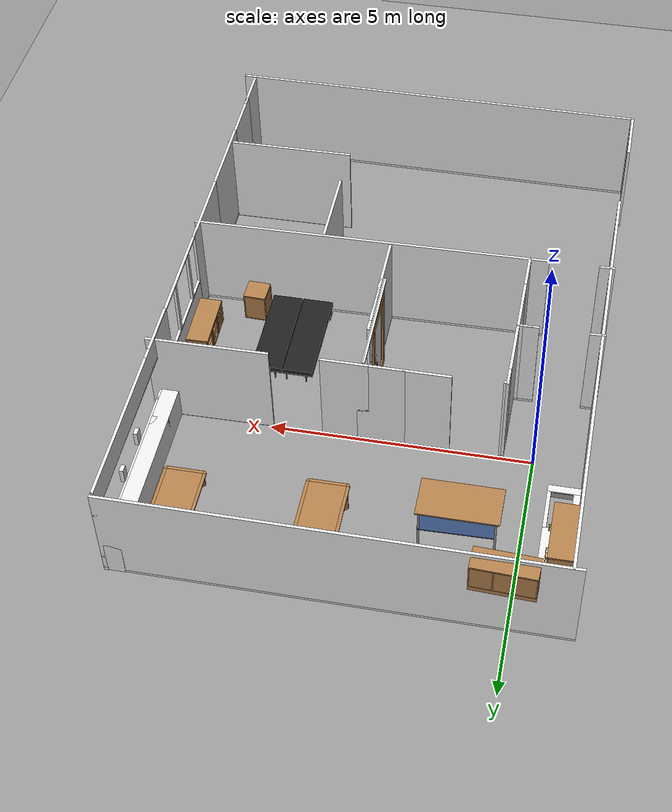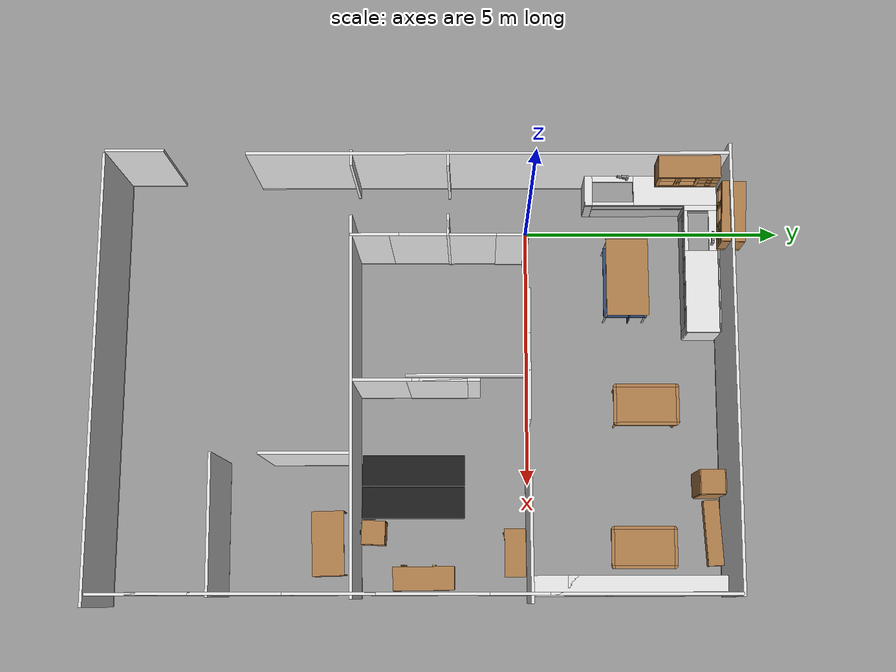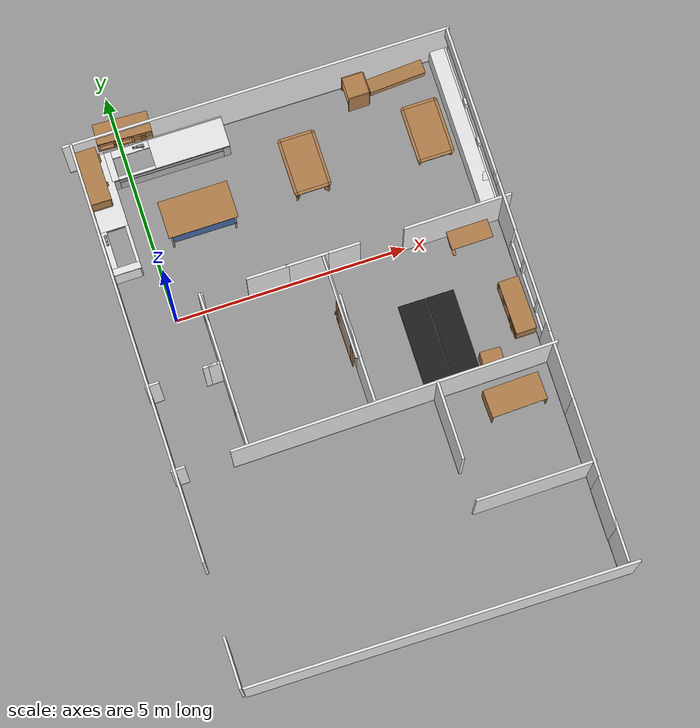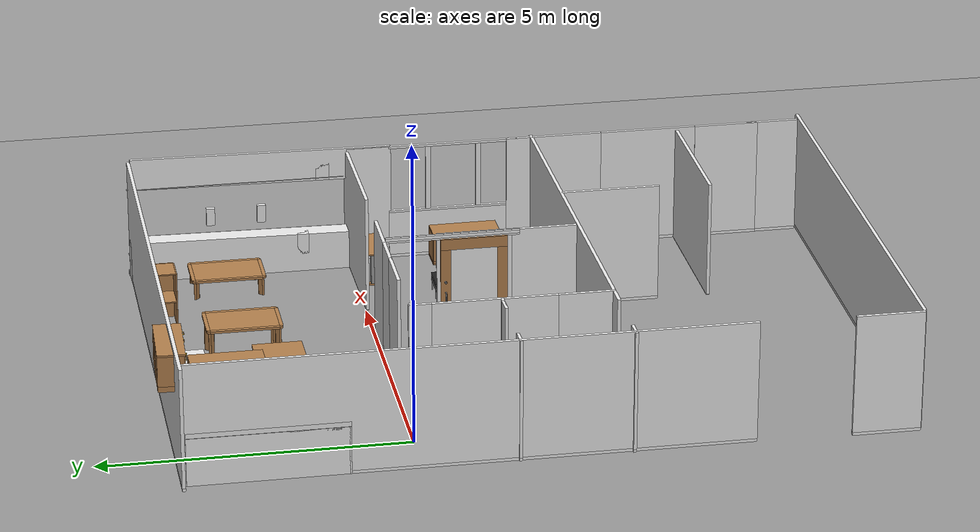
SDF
<sdf version="1.6">
 <world name="default">
  <light name="sun" type="directional">
   <pose>0 0 10 0 -0 0</pose>
   <diffuse>0.8 0.8 0.8 1</diffuse>
   <specular>0.1 0.1 0.1 1</specular>
   <attenuation>
    <range>1000</range>
    <constant>0.9</constant>
    <linear>0.01</linear>
    <quadratic>0.001</quadratic>
   </attenuation>
   <direction>-0.5 0.5 -1</direction>
  </light>
  <model name="ground_plane">
   <static>1</static>
   <link name="link">
    <collision name="collision">
     <geometry><plane><normal>0 0 1</normal><size>100 100</size></plane></geometry>
     <surface><friction><ode><mu>100</mu><mu2>50</mu2></ode></friction></surface>
    </collision>
    <visual name="visual">
     <cast_shadows>0</cast_shadows>
     <geometry><plane><normal>0 0 1</normal><size>100 100</size></plane></geometry>
     <material>
      <script><uri>file://media/materials/scripts/gazebo.material</uri><name>Gazebo/Grey</name></script>
     </material>
    </visual>
   </link>
  </model>
  <gravity>0 0 -9.8</gravity>
  <magnetic_field>6e-06 2.3e-05 -4.2e-05</magnetic_field>
  <atmosphere type="adiabatic"/>
  <physics name="default_physics" default="0" type="ode">
   <max_step_size>0.001</max_step_size>
   <real_time_factor>1</real_time_factor>
   <real_time_update_rate>1000</real_time_update_rate>
  </physics>
  <scene><ambient>0.4 0.4 0.4 1</ambient><background>0.7 0.7 0.7 1</background><shadows>1</shadows></scene>
  <spherical_coordinates>
   <surface_model>EARTH_WGS84</surface_model>
   <latitude_deg>0</latitude_deg>
   <longitude_deg>0</longitude_deg>
   <elevation>0</elevation>
   <heading_deg>0</heading_deg>
  </spherical_coordinates>
  <model name="full_wall_55_8295_2090_0">
   <link name="link">
    <inertial>
     <mass>50</mass>
     <inertia><ixx>1</ixx><ixy>0</ixy><ixz>0</ixz><iyy>1</iyy><iyz>0</iyz><izz>1</izz></inertia>
    </inertial>
    <visual name="bottom_frame">
     <pose>0 0 0.05 0 -0 0</pose>
     <geometry><box><size>0.055 8.295 0.1</size></box></geometry>
     <material>
      <script><uri>model://base_materials/color/scripts</uri><name>hsr_color/white</name></script>
     </material>
    </visual>
    <collision name="collision_bottom_frame">
     <pose>0 0 0.05 0 -0 0</pose>
     <geometry><box><size>0.055 8.295 0.1</size></box></geometry>
    </collision>
    <visual name="wall">
     <pose>0 0 1.095 0 -0 0</pose>
     <geometry><box><size>0.055 8.295 1.99</size></box></geometry>
     <material>
      <script>
       <uri>model://base_materials/wall/scripts</uri>
       <uri>model://base_materials/wall/textures</uri>
       <name>wall/white_noise</name>
      </script>
     </material>
    </visual>
    <collision name="collision_wall">
     <pose>0 0 1.095 0 -0 0</pose>
     <geometry><box><size>0.055 8.295 1.99</size></box></geometry>
    </collision>
    <velocity_decay><linear>0</linear><angular>0</angular></velocity_decay>
   </link>
   <static>1</static>
   <pose>2.97902 3.71668 0 0 0 -1.57394</pose>
  </model>
  <model name="window">
   <link name="link">
    <pose>0 -1.45119 -0.459736 0 -0 0</pose>
    <inertial>
     <mass>74.704</mass>
     <inertia><ixx>0</ixx><ixy>0</ixy><ixz>0</ixz><iyy>0</iyy><iyz>0</iyz><izz>0</izz></inertia>
    </inertial>
    <velocity_decay><linear>0</linear><angular>0</angular></velocity_decay>
    <visual name="bottom_frame">
     <pose>0 0 0.05 0 -0 0</pose>
     <geometry><box><size>0.076062 3.6807 0.026221</size></box></geometry>
     <material>
      <script><uri>model://base_materials/color/scripts</uri><name>hsr_color/white</name></script>
      <ambient>1 1 1 1</ambient>
      <diffuse>0.5 0.5 0.5 1</diffuse>
      <specular>0 0 0 1</specular>
      <emissive>0 0 0 1</emissive>
     </material>
    </visual>
    <visual name="wall">
     <pose>0 0 0.4875 0 -0 0</pose>
     <geometry><box><size>0.076062 3.6807 0.209551</size></box></geometry>
     <material>
      <script>
       <uri>model://base_materials/wall/scripts</uri>
       <uri>model://base_materials/wall/textures</uri>
       <name>wall/white_noise</name>
      </script>
      <ambient>1 1 1 1</ambient>
      <diffuse>0.5 0.5 0.5 1</diffuse>
      <specular>0 0 0 1</specular>
      <emissive>0 0 0 1</emissive>
     </material>
    </visual>
    <visual name="right_frame">
     <pose>0 0.4325 1.48 0 -0 0</pose>
     <geometry><box><size>0.076062 0.143199 0.306613</size></box></geometry>
     <material>
      <script><uri>model://base_materials/color/scripts</uri><name>hsr_color/white</name></script>
      <ambient>1 1 1 1</ambient>
      <diffuse>0.5 0.5 0.5 1</diffuse>
      <specular>0 0 0 1</specular>
      <emissive>0 0 0 1</emissive>
     </material>
    </visual>
    <visual name="center_frame">
     <pose>0 0 0.8925 0 -0 0</pose>
     <geometry><box><size>0.076062 3.6807 0.006217</size></box></geometry>
     <material>
      <script><uri>model://base_materials/color/scripts</uri><name>hsr_color/white</name></script>
      <ambient>1 1 1 1</ambient>
      <diffuse>0.5 0.5 0.5 1</diffuse>
      <specular>0 0 0 1</specular>
      <emissive>0 0 0 1</emissive>
     </material>
    </visual>
    <visual name="left_frame">
     <pose>0 -0.4325 1.48 0 -0 0</pose>
     <geometry><box><size>0.076062 0.143199 0.306613</size></box></geometry>
     <material>
      <script><uri>model://base_materials/color/scripts</uri><name>hsr_color/white</name></script>
      <ambient>1 1 1 1</ambient>
      <diffuse>0.5 0.5 0.5 1</diffuse>
      <specular>0 0 0 1</specular>
      <emissive>0 0 0 1</emissive>
     </material>
    </visual>
    <visual name="top_frame">
     <pose>0 0 2.07 0 -0 0</pose>
     <geometry><box><size>0.076062 3.6807 0.008574</size></box></geometry>
     <material>
      <script><uri>model://base_materials/color/scripts</uri><name>hsr_color/white</name></script>
      <ambient>1 1 1 1</ambient>
      <diffuse>0.5 0.5 0.5 1</diffuse>
      <specular>0 0 0 1</specular>
      <emissive>0 0 0 1</emissive>
     </material>
    </visual>
    <collision name="collision_right_frame">
     <pose>0 0.4325 1.48 0 -0 0</pose>
     <geometry><box><size>0.076062 0.143199 0.306613</size></box></geometry>
     <surface>
      <friction>
       <ode><mu>1</mu><mu2>1</mu2><fdir1>0 0 0</fdir1><slip1>0</slip1><slip2>0</slip2></ode>
       <torsional>
        <coefficient>1</coefficient>
        <patch_radius>0</patch_radius>
        <surface_radius>0</surface_radius>
        <use_patch_radius>1</use_patch_radius>
        <ode><slip>0</slip></ode>
       </torsional>
      </friction>
      <bounce><restitution_coefficient>0</restitution_coefficient><threshold>1e+06</threshold></bounce>
      <contact>
       <collide_without_contact>0</collide_without_contact>
       <collide_without_contact_bitmask>1</collide_without_contact_bitmask>
       <collide_bitmask>1</collide_bitmask>
       <ode>
        <soft_cfm>0</soft_cfm>
        <soft_erp>0.2</soft_erp>
        <kp>1e+13</kp>
        <kd>1</kd>
        <max_vel>0.01</max_vel>
        <min_depth>0</min_depth>
       </ode>
       <bullet>
        <split_impulse>1</split_impulse>
        <split_impulse_penetration_threshold>-0.01</split_impulse_penetration_threshold>
        <soft_cfm>0</soft_cfm>
        <soft_erp>0.2</soft_erp>
        <kp>1e+13</kp>
        <kd>1</kd>
       </bullet>
      </contact>
     </surface>
    </collision>
    <collision name="collision_bottom_frame">
     <pose>0 0 0.05 0 -0 0</pose>
     <geometry><box><size>0.076062 3.6807 0.026221</size></box></geometry>
     <surface>
      <friction>
       <ode><mu>1</mu><mu2>1</mu2><fdir1>0 0 0</fdir1><slip1>0</slip1><slip2>0</slip2></ode>
       <torsional>
        <coefficient>1</coefficient>
        <patch_radius>0</patch_radius>
        <surface_radius>0</surface_radius>
        <use_patch_radius>1</use_patch_radius>
        <ode><slip>0</slip></ode>
       </torsional>
      </friction>
      <bounce><restitution_coefficient>0</restitution_coefficient><threshold>1e+06</threshold></bounce>
      <contact>
       <collide_without_contact>0</collide_without_contact>
       <collide_without_contact_bitmask>1</collide_without_contact_bitmask>
       <collide_bitmask>1</collide_bitmask>
       <ode>
        <soft_cfm>0</soft_cfm>
        <soft_erp>0.2</soft_erp>
        <kp>1e+13</kp>
        <kd>1</kd>
        <max_vel>0.01</max_vel>
        <min_depth>0</min_depth>
       </ode>
       <bullet>
        <split_impulse>1</split_impulse>
        <split_impulse_penetration_threshold>-0.01</split_impulse_penetration_threshold>
        <soft_cfm>0</soft_cfm>
        <soft_erp>0.2</soft_erp>
        <kp>1e+13</kp>
        <kd>1</kd>
       </bullet>
      </contact>
     </surface>
    </collision>
    <collision name="collision_wall">
     <pose>0 0 0.4875 0 -0 0</pose>
     <geometry><box><size>0.076062 3.6807 0.209551</size></box></geometry>
     <surface>
      <friction>
       <ode><mu>1</mu><mu2>1</mu2><fdir1>0 0 0</fdir1><slip1>0</slip1><slip2>0</slip2></ode>
       <torsional>
        <coefficient>1</coefficient>
        <patch_radius>0</patch_radius>
        <surface_radius>0</surface_radius>
        <use_patch_radius>1</use_patch_radius>
        <ode><slip>0</slip></ode>
       </torsional>
      </friction>
      <bounce><restitution_coefficient>0</restitution_coefficient><threshold>1e+06</threshold></bounce>
      <contact>
       <collide_without_contact>0</collide_without_contact>
       <collide_without_contact_bitmask>1</collide_without_contact_bitmask>
       <collide_bitmask>1</collide_bitmask>
       <ode>
        <soft_cfm>0</soft_cfm>
        <soft_erp>0.2</soft_erp>
        <kp>1e+13</kp>
        <kd>1</kd>
        <max_vel>0.01</max_vel>
        <min_depth>0</min_depth>
       </ode>
       <bullet>
        <split_impulse>1</split_impulse>
        <split_impulse_penetration_threshold>-0.01</split_impulse_penetration_threshold>
        <soft_cfm>0</soft_cfm>
        <soft_erp>0.2</soft_erp>
        <kp>1e+13</kp>
        <kd>1</kd>
       </bullet>
      </contact>
     </surface>
    </collision>
    <collision name="collision_center_frame">
     <pose>0 0 0.8925 0 -0 0</pose>
     <geometry><box><size>0.076062 3.6807 0.006217</size></box></geometry>
     <surface>
      <friction>
       <ode><mu>1</mu><mu2>1</mu2><fdir1>0 0 0</fdir1><slip1>0</slip1><slip2>0</slip2></ode>
       <torsional>
        <coefficient>1</coefficient>
        <patch_radius>0</patch_radius>
        <surface_radius>0</surface_radius>
        <use_patch_radius>1</use_patch_radius>
        <ode><slip>0</slip></ode>
       </torsional>
      </friction>
      <bounce><restitution_coefficient>0</restitution_coefficient><threshold>1e+06</threshold></bounce>
      <contact>
       <collide_without_contact>0</collide_without_contact>
       <collide_without_contact_bitmask>1</collide_without_contact_bitmask>
       <collide_bitmask>1</collide_bitmask>
       <ode>
        <soft_cfm>0</soft_cfm>
        <soft_erp>0.2</soft_erp>
        <kp>1e+13</kp>
        <kd>1</kd>
        <max_vel>0.01</max_vel>
        <min_depth>0</min_depth>
       </ode>
       <bullet>
        <split_impulse>1</split_impulse>
        <split_impulse_penetration_threshold>-0.01</split_impulse_penetration_threshold>
        <soft_cfm>0</soft_cfm>
        <soft_erp>0.2</soft_erp>
        <kp>1e+13</kp>
        <kd>1</kd>
       </bullet>
      </contact>
     </surface>
    </collision>
    <collision name="collision_left_frame">
     <pose>0 -0.4325 1.48 0 -0 0</pose>
     <geometry><box><size>0.076062 0.143199 0.306613</size></box></geometry>
     <surface>
      <friction>
       <ode><mu>1</mu><mu2>1</mu2><fdir1>0 0 0</fdir1><slip1>0</slip1><slip2>0</slip2></ode>
       <torsional>
        <coefficient>1</coefficient>
        <patch_radius>0</patch_radius>
        <surface_radius>0</surface_radius>
        <use_patch_radius>1</use_patch_radius>
        <ode><slip>0</slip></ode>
       </torsional>
      </friction>
      <bounce><restitution_coefficient>0</restitution_coefficient><threshold>1e+06</threshold></bounce>
      <contact>
       <collide_without_contact>0</collide_without_contact>
       <collide_without_contact_bitmask>1</collide_without_contact_bitmask>
       <collide_bitmask>1</collide_bitmask>
       <ode>
        <soft_cfm>0</soft_cfm>
        <soft_erp>0.2</soft_erp>
        <kp>1e+13</kp>
        <kd>1</kd>
        <max_vel>0.01</max_vel>
        <min_depth>0</min_depth>
       </ode>
       <bullet>
        <split_impulse>1</split_impulse>
        <split_impulse_penetration_threshold>-0.01</split_impulse_penetration_threshold>
        <soft_cfm>0</soft_cfm>
        <soft_erp>0.2</soft_erp>
        <kp>1e+13</kp>
        <kd>1</kd>
       </bullet>
      </contact>
     </surface>
    </collision>
    <collision name="collision_top_frame">
     <pose>0 0 2.07 0 -0 0</pose>
     <geometry><box><size>0.076062 3.6807 0.008574</size></box></geometry>
     <surface>
      <friction>
       <ode><mu>1</mu><mu2>1</mu2><fdir1>0 0 0</fdir1><slip1>0</slip1><slip2>0</slip2></ode>
       <torsional>
        <coefficient>1</coefficient>
        <patch_radius>0</patch_radius>
        <surface_radius>0</surface_radius>
        <use_patch_radius>1</use_patch_radius>
        <ode><slip>0</slip></ode>
       </torsional>
      </friction>
      <bounce><restitution_coefficient>0</restitution_coefficient><threshold>1e+06</threshold></bounce>
      <contact>
       <collide_without_contact>0</collide_without_contact>
       <collide_without_contact_bitmask>1</collide_without_contact_bitmask>
       <collide_bitmask>1</collide_bitmask>
       <ode>
        <soft_cfm>0</soft_cfm>
        <soft_erp>0.2</soft_erp>
        <kp>1e+13</kp>
        <kd>1</kd>
        <max_vel>0.01</max_vel>
        <min_depth>0</min_depth>
       </ode>
       <bullet>
        <split_impulse>1</split_impulse>
        <split_impulse_penetration_threshold>-0.01</split_impulse_penetration_threshold>
        <soft_cfm>0</soft_cfm>
        <soft_erp>0.2</soft_erp>
        <kp>1e+13</kp>
        <kd>1</kd>
       </bullet>
      </contact>
     </surface>
    </collision>
   </link>
   <static>1</static>
   <pose>7.07328 3.36168 0 0 -0 0</pose>
  </model>
  <model name="full_wall_55_6475_bedroom">
   <link name="link">
    <pose>0 2.44347 0 0 -0 0</pose>
    <inertial>
     <mass>12.7126</mass>
     <inertia><ixx>0</ixx><ixy>0</ixy><ixz>0</ixz><iyy>0</iyy><iyz>0</iyz><izz>0</izz></inertia>
    </inertial>
    <velocity_decay><linear>0</linear><angular>0</angular></velocity_decay>
    <visual name="bottom_frame">
     <pose>0 0 0.05 0 -0 0</pose>
     <geometry><box><size>0.055 1.64629 0.1</size></box></geometry>
     <material>
      <script><uri>model://base_materials/color/scripts</uri><name>hsr_color/white</name></script>
      <ambient>1 1 1 1</ambient>
      <diffuse>0.5 0.5 0.5 1</diffuse>
      <specular>0 0 0 1</specular>
      <emissive>0 0 0 1</emissive>
     </material>
    </visual>
    <visual name="wall">
     <pose>0 0 1.095 0 -0 0</pose>
     <geometry><box><size>0.055 1.64629 1.99</size></box></geometry>
     <material>
      <script>
       <uri>model://base_materials/wall/scripts</uri>
       <uri>model://base_materials/wall/textures</uri>
       <name>wall/white_noise</name>
      </script>
      <ambient>1 1 1 1</ambient>
      <diffuse>0.5 0.5 0.5 1</diffuse>
      <specular>0 0 0 1</specular>
      <emissive>0 0 0 1</emissive>
     </material>
    </visual>
    <collision name="collision_bottom_frame">
     <pose>0 0 0.05 0 -0 0</pose>
     <geometry><box><size>0.055 1.64629 0.1</size></box></geometry>
     <surface>
      <friction>
       <ode><mu>1</mu><mu2>1</mu2><fdir1>0 0 0</fdir1><slip1>0</slip1><slip2>0</slip2></ode>
       <torsional>
        <coefficient>1</coefficient>
        <patch_radius>0</patch_radius>
        <surface_radius>0</surface_radius>
        <use_patch_radius>1</use_patch_radius>
        <ode><slip>0</slip></ode>
       </torsional>
      </friction>
      <bounce><restitution_coefficient>0</restitution_coefficient><threshold>1e+06</threshold></bounce>
      <contact>
       <collide_without_contact>0</collide_without_contact>
       <collide_without_contact_bitmask>1</collide_without_contact_bitmask>
       <collide_bitmask>1</collide_bitmask>
       <ode>
        <soft_cfm>0</soft_cfm>
        <soft_erp>0.2</soft_erp>
        <kp>1e+13</kp>
        <kd>1</kd>
        <max_vel>0.01</max_vel>
        <min_depth>0</min_depth>
       </ode>
       <bullet>
        <split_impulse>1</split_impulse>
        <split_impulse_penetration_threshold>-0.01</split_impulse_penetration_threshold>
        <soft_cfm>0</soft_cfm>
        <soft_erp>0.2</soft_erp>
        <kp>1e+13</kp>
        <kd>1</kd>
       </bullet>
      </contact>
     </surface>
    </collision>
    <collision name="collision_wall">
     <pose>0 0 1.095 0 -0 0</pose>
     <geometry><box><size>0.055 1.64629 1.99</size></box></geometry>
     <surface>
      <friction>
       <ode><mu>1</mu><mu2>1</mu2><fdir1>0 0 0</fdir1><slip1>0</slip1><slip2>0</slip2></ode>
       <torsional>
        <coefficient>1</coefficient>
        <patch_radius>0</patch_radius>
        <surface_radius>0</surface_radius>
        <use_patch_radius>1</use_patch_radius>
        <ode><slip>0</slip></ode>
       </torsional>
      </friction>
      <bounce><restitution_coefficient>0</restitution_coefficient><threshold>1e+06</threshold></bounce>
      <contact>
       <collide_without_contact>0</collide_without_contact>
       <collide_without_contact_bitmask>1</collide_without_contact_bitmask>
       <collide_bitmask>1</collide_bitmask>
       <ode>
        <soft_cfm>0</soft_cfm>
        <soft_erp>0.2</soft_erp>
        <kp>1e+13</kp>
        <kd>1</kd>
        <max_vel>0.01</max_vel>
        <min_depth>0</min_depth>
       </ode>
       <bullet>
        <split_impulse>1</split_impulse>
        <split_impulse_penetration_threshold>-0.01</split_impulse_penetration_threshold>
        <soft_cfm>0</soft_cfm>
        <soft_erp>0.2</soft_erp>
        <kp>1e+13</kp>
        <kd>1</kd>
       </bullet>
      </contact>
     </surface>
    </collision>
   </link>
   <static>1</static>
   <pose>7.0633 -7.6556 0 0 -0 0</pose>
  </model>
  <model name="full_wall_55_6475_bedroom_clone">
   <link name="link">
    <pose>0 2.44347 0 0 -0 0</pose>
    <inertial>
     <mass>12.7126</mass>
     <inertia><ixx>0</ixx><ixy>0</ixy><ixz>0</ixz><iyy>0</iyy><iyz>0</iyz><izz>0</izz></inertia>
    </inertial>
    <velocity_decay><linear>0</linear><angular>0</angular></velocity_decay>
    <visual name="bottom_frame">
     <pose>0 0 0.05 0 -0 0</pose>
     <geometry><box><size>0.055 1.64629 0.1</size></box></geometry>
     <material>
      <script><uri>model://base_materials/color/scripts</uri><name>hsr_color/white</name></script>
      <ambient>1 1 1 1</ambient>
      <diffuse>0.5 0.5 0.5 1</diffuse>
      <specular>0 0 0 1</specular>
      <emissive>0 0 0 1</emissive>
     </material>
    </visual>
    <visual name="wall">
     <pose>0 0 1.095 0 -0 0</pose>
     <geometry><box><size>0.055 1.64629 1.99</size></box></geometry>
     <material>
      <script>
       <uri>model://base_materials/wall/scripts</uri>
       <uri>model://base_materials/wall/textures</uri>
       <name>wall/white_noise</name>
      </script>
      <ambient>1 1 1 1</ambient>
      <diffuse>0.5 0.5 0.5 1</diffuse>
      <specular>0 0 0 1</specular>
      <emissive>0 0 0 1</emissive>
     </material>
    </visual>
    <collision name="collision_bottom_frame">
     <pose>0 0 0.05 0 -0 0</pose>
     <geometry><box><size>0.055 1.64629 0.1</size></box></geometry>
     <surface>
      <friction>
       <ode><mu>1</mu><mu2>1</mu2><fdir1>0 0 0</fdir1><slip1>0</slip1><slip2>0</slip2></ode>
       <torsional>
        <coefficient>1</coefficient>
        <patch_radius>0</patch_radius>
        <surface_radius>0</surface_radius>
        <use_patch_radius>1</use_patch_radius>
        <ode><slip>0</slip></ode>
       </torsional>
      </friction>
      <bounce><restitution_coefficient>0</restitution_coefficient><threshold>1e+06</threshold></bounce>
      <contact>
       <collide_without_contact>0</collide_without_contact>
       <collide_without_contact_bitmask>1</collide_without_contact_bitmask>
       <collide_bitmask>1</collide_bitmask>
       <ode>
        <soft_cfm>0</soft_cfm>
        <soft_erp>0.2</soft_erp>
        <kp>1e+13</kp>
        <kd>1</kd>
        <max_vel>0.01</max_vel>
        <min_depth>0</min_depth>
       </ode>
       <bullet>
        <split_impulse>1</split_impulse>
        <split_impulse_penetration_threshold>-0.01</split_impulse_penetration_threshold>
        <soft_cfm>0</soft_cfm>
        <soft_erp>0.2</soft_erp>
        <kp>1e+13</kp>
        <kd>1</kd>
       </bullet>
      </contact>
     </surface>
    </collision>
    <collision name="collision_wall">
     <pose>0 0 1.095 0 -0 0</pose>
     <geometry><box><size>0.055 1.64629 1.99</size></box></geometry>
     <surface>
      <friction>
       <ode><mu>1</mu><mu2>1</mu2><fdir1>0 0 0</fdir1><slip1>0</slip1><slip2>0</slip2></ode>
       <torsional>
        <coefficient>1</coefficient>
        <patch_radius>0</patch_radius>
        <surface_radius>0</surface_radius>
        <use_patch_radius>1</use_patch_radius>
        <ode><slip>0</slip></ode>
       </torsional>
      </friction>
      <bounce><restitution_coefficient>0</restitution_coefficient><threshold>1e+06</threshold></bounce>
      <contact>
       <collide_without_contact>0</collide_without_contact>
       <collide_without_contact_bitmask>1</collide_without_contact_bitmask>
       <collide_bitmask>1</collide_bitmask>
       <ode>
        <soft_cfm>0</soft_cfm>
        <soft_erp>0.2</soft_erp>
        <kp>1e+13</kp>
        <kd>1</kd>
        <max_vel>0.01</max_vel>
        <min_depth>0</min_depth>
       </ode>
       <bullet>
        <split_impulse>1</split_impulse>
        <split_impulse_penetration_threshold>-0.01</split_impulse_penetration_threshold>
        <soft_cfm>0</soft_cfm>
        <soft_erp>0.2</soft_erp>
        <kp>1e+13</kp>
        <kd>1</kd>
       </bullet>
      </contact>
     </surface>
    </collision>
   </link>
   <static>1</static>
   <pose>7.0618 -6.01135 0 0 -0 0</pose>
  </model>
  <light name="user_directional_light_0" type="directional">
   <pose>3.8957 -2.52723 1 0 -0 0</pose>
   <diffuse>0.5 0.5 0.5 1</diffuse>
   <specular>0.1 0.1 0.1 1</specular>
   <direction>0.1 0.1 -0.9</direction>
   <attenuation>
    <range>20</range>
    <constant>0.5</constant>
    <linear>0.01</linear>
    <quadratic>0.001</quadratic>
   </attenuation>
  </light>
  <model name="slim_wall_0_clone">
   <link name="link">
    <pose>-1.21711 0.435553 0 0 -0 0</pose>
    <inertial>
     <mass>12.4167</mass>
     <inertia><ixx>0</ixx><ixy>0</ixy><ixz>0</ixz><iyy>0</iyy><iyz>0</iyz><izz>0</izz></inertia>
    </inertial>
    <velocity_decay><linear>0</linear><angular>0</angular></velocity_decay>
    <visual name="bottom_frame">
     <pose>0 0 0.05 0 -0 0</pose>
     <geometry><box><size>0.048855 0.300624 0.1</size></box></geometry>
     <material>
      <script><uri>model://base_materials/color/scripts</uri><name>hsr_color/white</name></script>
      <ambient>1 1 1 1</ambient>
      <diffuse>0.5 0.5 0.5 1</diffuse>
      <specular>0 0 0 1</specular>
      <emissive>0 0 0 1</emissive>
     </material>
    </visual>
    <visual name="wall">
     <pose>0 0 1.095 0 -0 0</pose>
     <geometry><box><size>0.048855 0.300624 1.99</size></box></geometry>
     <material>
      <script>
       <uri>model://base_materials/wall/scripts</uri>
       <uri>model://base_materials/wall/textures</uri>
       <name>wall/white_noise</name>
      </script>
      <ambient>1 1 1 1</ambient>
      <diffuse>0.5 0.5 0.5 1</diffuse>
      <specular>0 0 0 1</specular>
      <emissive>0 0 0 1</emissive>
     </material>
    </visual>
    <collision name="collision_bottom_frame">
     <pose>0 0 0.05 0 -0 0</pose>
     <geometry><box><size>0.048855 0.300624 0.1</size></box></geometry>
     <surface>
      <friction>
       <ode><mu>1</mu><mu2>1</mu2><fdir1>0 0 0</fdir1><slip1>0</slip1><slip2>0</slip2></ode>
       <torsional>
        <coefficient>1</coefficient>
        <patch_radius>0</patch_radius>
        <surface_radius>0</surface_radius>
        <use_patch_radius>1</use_patch_radius>
        <ode><slip>0</slip></ode>
       </torsional>
      </friction>
      <bounce><restitution_coefficient>0</restitution_coefficient><threshold>1e+06</threshold></bounce>
      <contact>
       <collide_without_contact>0</collide_without_contact>
       <collide_without_contact_bitmask>1</collide_without_contact_bitmask>
       <collide_bitmask>1</collide_bitmask>
       <ode>
        <soft_cfm>0</soft_cfm>
        <soft_erp>0.2</soft_erp>
        <kp>1e+13</kp>
        <kd>1</kd>
        <max_vel>0.01</max_vel>
        <min_depth>0</min_depth>
       </ode>
       <bullet>
        <split_impulse>1</split_impulse>
        <split_impulse_penetration_threshold>-0.01</split_impulse_penetration_threshold>
        <soft_cfm>0</soft_cfm>
        <soft_erp>0.2</soft_erp>
        <kp>1e+13</kp>
        <kd>1</kd>
       </bullet>
      </contact>
     </surface>
    </collision>
    <collision name="collision_wall">
     <pose>0 0 1.095 0 -0 0</pose>
     <geometry><box><size>0.048855 0.300624 1.99</size></box></geometry>
     <surface>
      <friction>
       <ode><mu>1</mu><mu2>1</mu2><fdir1>0 0 0</fdir1><slip1>0</slip1><slip2>0</slip2></ode>
       <torsional>
        <coefficient>1</coefficient>
        <patch_radius>0</patch_radius>
        <surface_radius>0</surface_radius>
        <use_patch_radius>1</use_patch_radius>
        <ode><slip>0</slip></ode>
       </torsional>
      </friction>
      <bounce><restitution_coefficient>0</restitution_coefficient><threshold>1e+06</threshold></bounce>
      <contact>
       <collide_without_contact>0</collide_without_contact>
       <collide_without_contact_bitmask>1</collide_without_contact_bitmask>
       <collide_bitmask>1</collide_bitmask>
       <ode>
        <soft_cfm>0</soft_cfm>
        <soft_erp>0.2</soft_erp>
        <kp>1e+13</kp>
        <kd>1</kd>
        <max_vel>0.01</max_vel>
        <min_depth>0</min_depth>
       </ode>
       <bullet>
        <split_impulse>1</split_impulse>
        <split_impulse_penetration_threshold>-0.01</split_impulse_penetration_threshold>
        <soft_cfm>0</soft_cfm>
        <soft_erp>0.2</soft_erp>
        <kp>1e+13</kp>
        <kd>1</kd>
       </bullet>
      </contact>
     </surface>
    </collision>
   </link>
   <static>1</static>
   <pose>-0.483673 -2.07543 0 0 -0 1.58512</pose>
  </model>
  <model name="slim_wall_0_clone_0">
   <link name="link">
    <pose>-1.21711 0.435553 0 0 -0 0</pose>
    <inertial>
     <mass>12.4167</mass>
     <inertia><ixx>0</ixx><ixy>0</ixy><ixz>0</ixz><iyy>0</iyy><iyz>0</iyz><izz>0</izz></inertia>
    </inertial>
    <velocity_decay><linear>0</linear><angular>0</angular></velocity_decay>
    <visual name="bottom_frame">
     <pose>0 0 0.05 0 -0 0</pose>
     <geometry><box><size>0.048855 0.300624 0.1</size></box></geometry>
     <material>
      <script><uri>model://base_materials/color/scripts</uri><name>hsr_color/white</name></script>
      <ambient>1 1 1 1</ambient>
      <diffuse>0.5 0.5 0.5 1</diffuse>
      <specular>0 0 0 1</specular>
      <emissive>0 0 0 1</emissive>
     </material>
    </visual>
    <visual name="wall">
     <pose>0 0 1.095 0 -0 0</pose>
     <geometry><box><size>0.048855 0.300624 1.99</size></box></geometry>
     <material>
      <script>
       <uri>model://base_materials/wall/scripts</uri>
       <uri>model://base_materials/wall/textures</uri>
       <name>wall/white_noise</name>
      </script>
      <ambient>1 1 1 1</ambient>
      <diffuse>0.5 0.5 0.5 1</diffuse>
      <specular>0 0 0 1</specular>
      <emissive>0 0 0 1</emissive>
     </material>
    </visual>
    <collision name="collision_bottom_frame">
     <pose>0 0 0.05 0 -0 0</pose>
     <geometry><box><size>0.048855 0.300624 0.1</size></box></geometry>
     <surface>
      <friction>
       <ode><mu>1</mu><mu2>1</mu2><fdir1>0 0 0</fdir1><slip1>0</slip1><slip2>0</slip2></ode>
       <torsional>
        <coefficient>1</coefficient>
        <patch_radius>0</patch_radius>
        <surface_radius>0</surface_radius>
        <use_patch_radius>1</use_patch_radius>
        <ode><slip>0</slip></ode>
       </torsional>
      </friction>
      <bounce><restitution_coefficient>0</restitution_coefficient><threshold>1e+06</threshold></bounce>
      <contact>
       <collide_without_contact>0</collide_without_contact>
       <collide_without_contact_bitmask>1</collide_without_contact_bitmask>
       <collide_bitmask>1</collide_bitmask>
       <ode>
        <soft_cfm>0</soft_cfm>
        <soft_erp>0.2</soft_erp>
        <kp>1e+13</kp>
        <kd>1</kd>
        <max_vel>0.01</max_vel>
        <min_depth>0</min_depth>
       </ode>
       <bullet>
        <split_impulse>1</split_impulse>
        <split_impulse_penetration_threshold>-0.01</split_impulse_penetration_threshold>
        <soft_cfm>0</soft_cfm>
        <soft_erp>0.2</soft_erp>
        <kp>1e+13</kp>
        <kd>1</kd>
       </bullet>
      </contact>
     </surface>
    </collision>
    <collision name="collision_wall">
     <pose>0 0 1.095 0 -0 0</pose>
     <geometry><box><size>0.048855 0.300624 1.99</size></box></geometry>
     <surface>
      <friction>
       <ode><mu>1</mu><mu2>1</mu2><fdir1>0 0 0</fdir1><slip1>0</slip1><slip2>0</slip2></ode>
       <torsional>
        <coefficient>1</coefficient>
        <patch_radius>0</patch_radius>
        <surface_radius>0</surface_radius>
        <use_patch_radius>1</use_patch_radius>
        <ode><slip>0</slip></ode>
       </torsional>
      </friction>
      <bounce><restitution_coefficient>0</restitution_coefficient><threshold>1e+06</threshold></bounce>
      <contact>
       <collide_without_contact>0</collide_without_contact>
       <collide_without_contact_bitmask>1</collide_without_contact_bitmask>
       <collide_bitmask>1</collide_bitmask>
       <ode>
        <soft_cfm>0</soft_cfm>
        <soft_erp>0.2</soft_erp>
        <kp>1e+13</kp>
        <kd>1</kd>
        <max_vel>0.01</max_vel>
        <min_depth>0</min_depth>
       </ode>
       <bullet>
        <split_impulse>1</split_impulse>
        <split_impulse_penetration_threshold>-0.01</split_impulse_penetration_threshold>
        <soft_cfm>0</soft_cfm>
        <soft_erp>0.2</soft_erp>
        <kp>1e+13</kp>
        <kd>1</kd>
       </bullet>
      </contact>
     </surface>
    </collision>
   </link>
   <static>1</static>
   <pose>-0.467426 -0.282366 0 0 -0 1.58512</pose>
  </model>
  <model name="slim_wall_0_clone_1">
   <link name="link">
    <pose>-1.21711 0.435553 0 0 -0 0</pose>
    <inertial>
     <mass>12.4167</mass>
     <inertia><ixx>0</ixx><ixy>0</ixy><ixz>0</ixz><iyy>0</iyy><iyz>0</iyz><izz>0</izz></inertia>
    </inertial>
    <velocity_decay><linear>0</linear><angular>0</angular></velocity_decay>
    <visual name="bottom_frame">
     <pose>0 0 0.05 0 -0 0</pose>
     <geometry><box><size>0.048855 0.300624 0.1</size></box></geometry>
     <material>
      <script><uri>model://base_materials/color/scripts</uri><name>hsr_color/white</name></script>
      <ambient>1 1 1 1</ambient>
      <diffuse>0.5 0.5 0.5 1</diffuse>
      <specular>0 0 0 1</specular>
      <emissive>0 0 0 1</emissive>
     </material>
    </visual>
    <visual name="wall">
     <pose>0 0 1.095 0 -0 0</pose>
     <geometry><box><size>0.048855 0.300624 1.99</size></box></geometry>
     <material>
      <script>
       <uri>model://base_materials/wall/scripts</uri>
       <uri>model://base_materials/wall/textures</uri>
       <name>wall/white_noise</name>
      </script>
      <ambient>1 1 1 1</ambient>
      <diffuse>0.5 0.5 0.5 1</diffuse>
      <specular>0 0 0 1</specular>
      <emissive>0 0 0 1</emissive>
     </material>
    </visual>
    <collision name="collision_bottom_frame">
     <pose>0 0 0.05 0 -0 0</pose>
     <geometry><box><size>0.048855 0.300624 0.1</size></box></geometry>
     <surface>
      <friction>
       <ode><mu>1</mu><mu2>1</mu2><fdir1>0 0 0</fdir1><slip1>0</slip1><slip2>0</slip2></ode>
       <torsional>
        <coefficient>1</coefficient>
        <patch_radius>0</patch_radius>
        <surface_radius>0</surface_radius>
        <use_patch_radius>1</use_patch_radius>
        <ode><slip>0</slip></ode>
       </torsional>
      </friction>
      <bounce><restitution_coefficient>0</restitution_coefficient><threshold>1e+06</threshold></bounce>
      <contact>
       <collide_without_contact>0</collide_without_contact>
       <collide_without_contact_bitmask>1</collide_without_contact_bitmask>
       <collide_bitmask>1</collide_bitmask>
       <ode>
        <soft_cfm>0</soft_cfm>
        <soft_erp>0.2</soft_erp>
        <kp>1e+13</kp>
        <kd>1</kd>
        <max_vel>0.01</max_vel>
        <min_depth>0</min_depth>
       </ode>
       <bullet>
        <split_impulse>1</split_impulse>
        <split_impulse_penetration_threshold>-0.01</split_impulse_penetration_threshold>
        <soft_cfm>0</soft_cfm>
        <soft_erp>0.2</soft_erp>
        <kp>1e+13</kp>
        <kd>1</kd>
       </bullet>
      </contact>
     </surface>
    </collision>
    <collision name="collision_wall">
     <pose>0 0 1.095 0 -0 0</pose>
     <geometry><box><size>0.048855 0.300624 1.99</size></box></geometry>
     <surface>
      <friction>
       <ode><mu>1</mu><mu2>1</mu2><fdir1>0 0 0</fdir1><slip1>0</slip1><slip2>0</slip2></ode>
       <torsional>
        <coefficient>1</coefficient>
        <patch_radius>0</patch_radius>
        <surface_radius>0</surface_radius>
        <use_patch_radius>1</use_patch_radius>
        <ode><slip>0</slip></ode>
       </torsional>
      </friction>
      <bounce><restitution_coefficient>0</restitution_coefficient><threshold>1e+06</threshold></bounce>
      <contact>
       <collide_without_contact>0</collide_without_contact>
       <collide_without_contact_bitmask>1</collide_without_contact_bitmask>
       <collide_bitmask>1</collide_bitmask>
       <ode>
        <soft_cfm>0</soft_cfm>
        <soft_erp>0.2</soft_erp>
        <kp>1e+13</kp>
        <kd>1</kd>
        <max_vel>0.01</max_vel>
        <min_depth>0</min_depth>
       </ode>
       <bullet>
        <split_impulse>1</split_impulse>
        <split_impulse_penetration_threshold>-0.01</split_impulse_penetration_threshold>
        <soft_cfm>0</soft_cfm>
        <soft_erp>0.2</soft_erp>
        <kp>1e+13</kp>
        <kd>1</kd>
       </bullet>
      </contact>
     </surface>
    </collision>
   </link>
   <static>1</static>
   <pose>0.754581 -0.274826 0 0 -0 1.58512</pose>
  </model>
  <model name="slim_wall_0_clone_2">
   <link name="link">
    <pose>-1.21711 0.435553 0 0 -0 0</pose>
    <inertial>
     <mass>12.4167</mass>
     <inertia><ixx>0</ixx><ixy>0</ixy><ixz>0</ixz><iyy>0</iyy><iyz>0</iyz><izz>0</izz></inertia>
    </inertial>
    <velocity_decay><linear>0</linear><angular>0</angular></velocity_decay>
    <visual name="bottom_frame">
     <pose>0 0 0.05 0 -0 0</pose>
     <geometry><box><size>0.048855 0.300624 0.1</size></box></geometry>
     <material>
      <script><uri>model://base_materials/color/scripts</uri><name>hsr_color/white</name></script>
      <ambient>1 1 1 1</ambient>
      <diffuse>0.5 0.5 0.5 1</diffuse>
      <specular>0 0 0 1</specular>
      <emissive>0 0 0 1</emissive>
     </material>
    </visual>
    <visual name="wall">
     <pose>0 0 1.095 0 -0 0</pose>
     <geometry><box><size>0.048855 0.300624 1.99</size></box></geometry>
     <material>
      <script>
       <uri>model://base_materials/wall/scripts</uri>
       <uri>model://base_materials/wall/textures</uri>
       <name>wall/white_noise</name>
      </script>
      <ambient>1 1 1 1</ambient>
      <diffuse>0.5 0.5 0.5 1</diffuse>
      <specular>0 0 0 1</specular>
      <emissive>0 0 0 1</emissive>
     </material>
    </visual>
    <collision name="collision_bottom_frame">
     <pose>0 0 0.05 0 -0 0</pose>
     <geometry><box><size>0.048855 0.300624 0.1</size></box></geometry>
     <surface>
      <friction>
       <ode><mu>1</mu><mu2>1</mu2><fdir1>0 0 0</fdir1><slip1>0</slip1><slip2>0</slip2></ode>
       <torsional>
        <coefficient>1</coefficient>
        <patch_radius>0</patch_radius>
        <surface_radius>0</surface_radius>
        <use_patch_radius>1</use_patch_radius>
        <ode><slip>0</slip></ode>
       </torsional>
      </friction>
      <bounce><restitution_coefficient>0</restitution_coefficient><threshold>1e+06</threshold></bounce>
      <contact>
       <collide_without_contact>0</collide_without_contact>
       <collide_without_contact_bitmask>1</collide_without_contact_bitmask>
       <collide_bitmask>1</collide_bitmask>
       <ode>
        <soft_cfm>0</soft_cfm>
        <soft_erp>0.2</soft_erp>
        <kp>1e+13</kp>
        <kd>1</kd>
        <max_vel>0.01</max_vel>
        <min_depth>0</min_depth>
       </ode>
       <bullet>
        <split_impulse>1</split_impulse>
        <split_impulse_penetration_threshold>-0.01</split_impulse_penetration_threshold>
        <soft_cfm>0</soft_cfm>
        <soft_erp>0.2</soft_erp>
        <kp>1e+13</kp>
        <kd>1</kd>
       </bullet>
      </contact>
     </surface>
    </collision>
    <collision name="collision_wall">
     <pose>0 0 1.095 0 -0 0</pose>
     <geometry><box><size>0.048855 0.300624 1.99</size></box></geometry>
     <surface>
      <friction>
       <ode><mu>1</mu><mu2>1</mu2><fdir1>0 0 0</fdir1><slip1>0</slip1><slip2>0</slip2></ode>
       <torsional>
        <coefficient>1</coefficient>
        <patch_radius>0</patch_radius>
        <surface_radius>0</surface_radius>
        <use_patch_radius>1</use_patch_radius>
        <ode><slip>0</slip></ode>
       </torsional>
      </friction>
      <bounce><restitution_coefficient>0</restitution_coefficient><threshold>1e+06</threshold></bounce>
      <contact>
       <collide_without_contact>0</collide_without_contact>
       <collide_without_contact_bitmask>1</collide_without_contact_bitmask>
       <collide_bitmask>1</collide_bitmask>
       <ode>
        <soft_cfm>0</soft_cfm>
        <soft_erp>0.2</soft_erp>
        <kp>1e+13</kp>
        <kd>1</kd>
        <max_vel>0.01</max_vel>
        <min_depth>0</min_depth>
       </ode>
       <bullet>
        <split_impulse>1</split_impulse>
        <split_impulse_penetration_threshold>-0.01</split_impulse_penetration_threshold>
        <soft_cfm>0</soft_cfm>
        <soft_erp>0.2</soft_erp>
        <kp>1e+13</kp>
        <kd>1</kd>
       </bullet>
      </contact>
     </surface>
    </collision>
   </link>
   <static>1</static>
   <pose>0.874173 -0.274906 0 0 -0 1.58512</pose>
  </model>
  <model name="full_wall_55_1100_2090_0">
   <link name="link">
    <inertial>
     <mass>50</mass>
     <inertia><ixx>1</ixx><ixy>0</ixy><ixz>0</ixz><iyy>1</iyy><iyz>0</iyz><izz>1</izz></inertia>
    </inertial>
    <visual name="bottom_frame">
     <pose>0 0 0.05 0 -0 0</pose>
     <geometry><box><size>0.055 1.1 0.1</size></box></geometry>
     <material>
      <script><uri>model://base_materials/color/scripts</uri><name>hsr_color/white</name></script>
     </material>
    </visual>
    <collision name="collision_bottom_frame">
     <pose>0 0 0.05 0 -0 0</pose>
     <geometry><box><size>0.055 1.1 0.1</size></box></geometry>
    </collision>
    <visual name="wall">
     <pose>0 0 1.095 0 -0 0</pose>
     <geometry><box><size>0.055 1.1 1.99</size></box></geometry>
     <material>
      <script>
       <uri>model://base_materials/wall/scripts</uri>
       <uri>model://base_materials/wall/textures</uri>
       <name>wall/white_noise</name>
      </script>
     </material>
    </visual>
    <collision name="collision_wall">
     <pose>0 0 1.095 0 -0 0</pose>
     <geometry><box><size>0.055 1.1 1.99</size></box></geometry>
    </collision>
    <velocity_decay><linear>0</linear><angular>0</angular></velocity_decay>
   </link>
   <static>1</static>
   <pose>0.574353 -2.02901 0 0 -0 0</pose>
  </model>
  <model name="full_wall_55_1100_2090_1">
   <link name="link">
    <inertial>
     <mass>50</mass>
     <inertia><ixx>1</ixx><ixy>0</ixy><ixz>0</ixz><iyy>1</iyy><iyz>0</iyz><izz>1</izz></inertia>
    </inertial>
    <visual name="bottom_frame">
     <pose>0 0 0.05 0 -0 0</pose>
     <geometry><box><size>0.055 1.1 0.1</size></box></geometry>
     <material>
      <script><uri>model://base_materials/color/scripts</uri><name>hsr_color/white</name></script>
     </material>
    </visual>
    <collision name="collision_bottom_frame">
     <pose>0 0 0.05 0 -0 0</pose>
     <geometry><box><size>0.055 1.1 0.1</size></box></geometry>
    </collision>
    <visual name="wall">
     <pose>0 0 1.095 0 -0 0</pose>
     <geometry><box><size>0.055 1.1 1.99</size></box></geometry>
     <material>
      <script>
       <uri>model://base_materials/wall/scripts</uri>
       <uri>model://base_materials/wall/textures</uri>
       <name>wall/white_noise</name>
      </script>
     </material>
    </visual>
    <collision name="collision_wall">
     <pose>0 0 1.095 0 -0 0</pose>
     <geometry><box><size>0.055 1.1 1.99</size></box></geometry>
    </collision>
    <velocity_decay><linear>0</linear><angular>0</angular></velocity_decay>
   </link>
   <static>1</static>
   <pose>0.578006 -0.931267 0 0 -0 0</pose>
  </model>
  <model name="full_wall_55_600_2090">
   <link name="link">
    <inertial>
     <mass>50</mass>
     <inertia><ixx>1</ixx><ixy>0</ixy><ixz>0</ixz><iyy>1</iyy><iyz>0</iyz><izz>1</izz></inertia>
    </inertial>
    <visual name="bottom_frame">
     <pose>0 0 0.05 0 -0 0</pose>
     <geometry><box><size>0.055 0.6 0.1</size></box></geometry>
     <material>
      <script><uri>model://base_materials/color/scripts</uri><name>hsr_color/white</name></script>
     </material>
    </visual>
    <collision name="collision_bottom_frame">
     <pose>0 0 0.05 0 -0 0</pose>
     <geometry><box><size>0.055 0.6 0.1</size></box></geometry>
    </collision>
    <visual name="wall">
     <pose>0 0 1.095 0 -0 0</pose>
     <geometry><box><size>0.055 0.6 1.99</size></box></geometry>
     <material>
      <script>
       <uri>model://base_materials/wall/scripts</uri>
       <uri>model://base_materials/wall/textures</uri>
       <name>wall/white_noise</name>
      </script>
     </material>
    </visual>
    <collision name="collision_wall">
     <pose>0 0 1.095 0 -0 0</pose>
     <geometry><box><size>0.055 0.6 1.99</size></box></geometry>
    </collision>
    <velocity_decay><linear>0</linear><angular>0</angular></velocity_decay>
   </link>
   <static>1</static>
   <pose>0.5806 -0.313776 0 0 -0 0</pose>
  </model>
  <model name="full_wall_55_900_2090_0">
   <link name="link">
    <inertial>
     <mass>50</mass>
     <inertia><ixx>1</ixx><ixy>0</ixy><ixz>0</ixz><iyy>1</iyy><iyz>0</iyz><izz>1</izz></inertia>
    </inertial>
    <visual name="bottom_frame">
     <pose>0 0 0.05 0 -0 0</pose>
     <geometry><box><size>0.055 0.9 0.1</size></box></geometry>
     <material>
      <script><uri>model://base_materials/color/scripts</uri><name>hsr_color/white</name></script>
     </material>
    </visual>
    <collision name="collision_bottom_frame">
     <pose>0 0 0.05 0 -0 0</pose>
     <geometry><box><size>0.055 0.9 0.1</size></box></geometry>
    </collision>
    <visual name="wall">
     <pose>0 0 1.095 0 -0 0</pose>
     <geometry><box><size>0.055 0.9 1.99</size></box></geometry>
     <material>
      <script>
       <uri>model://base_materials/wall/scripts</uri>
       <uri>model://base_materials/wall/textures</uri>
       <name>wall/white_noise</name>
      </script>
     </material>
    </visual>
    <collision name="collision_wall">
     <pose>0 0 1.095 0 -0 0</pose>
     <geometry><box><size>0.055 0.9 1.99</size></box></geometry>
    </collision>
    <velocity_decay><linear>0</linear><angular>0</angular></velocity_decay>
   </link>
   <static>1</static>
   <pose>0.573697 -2.84416 0 0 -0 0</pose>
  </model>
  <model name="wall_frame_55_55_2090">
   <link name="link">
    <inertial>
     <mass>50</mass>
     <inertia><ixx>1</ixx><ixy>0</ixy><ixz>0</ixz><iyy>1</iyy><iyz>0</iyz><izz>1</izz></inertia>
    </inertial>
    <visual name="_frame">
     <pose>0 0 1.045 0 -0 0</pose>
     <geometry><box><size>0.055 0.055 2.09</size></box></geometry>
     <material>
      <script><uri>model://base_materials/color/scripts</uri><name>hsr_color/white</name></script>
     </material>
    </visual>
    <collision name="collision_frame">
     <pose>0 0 1.045 0 -0 0</pose>
     <geometry><box><size>0.055 0.055 2.09</size></box></geometry>
    </collision>
    <velocity_decay><linear>0</linear><angular>0</angular></velocity_decay>
   </link>
   <static>1</static>
   <pose>0.623893 -0.054688 0 0 -0 0</pose>
  </model>
  <model name="full_wall_55_900_2090_1">
   <link name="link">
    <inertial>
     <mass>50</mass>
     <inertia><ixx>1</ixx><ixy>0</ixy><ixz>0</ixz><iyy>1</iyy><iyz>0</iyz><izz>1</izz></inertia>
    </inertial>
    <visual name="bottom_frame">
     <pose>0 0 0.05 0 -0 0</pose>
     <geometry><box><size>0.055 0.9 0.1</size></box></geometry>
     <material>
      <script><uri>model://base_materials/color/scripts</uri><name>hsr_color/white</name></script>
     </material>
    </visual>
    <collision name="collision_bottom_frame">
     <pose>0 0 0.05 0 -0 0</pose>
     <geometry><box><size>0.055 0.9 0.1</size></box></geometry>
    </collision>
    <visual name="wall">
     <pose>0 0 1.095 0 -0 0</pose>
     <geometry><box><size>0.055 0.9 1.99</size></box></geometry>
     <material>
      <script>
       <uri>model://base_materials/wall/scripts</uri>
       <uri>model://base_materials/wall/textures</uri>
       <name>wall/white_noise</name>
      </script>
     </material>
    </visual>
    <collision name="collision_wall">
     <pose>0 0 1.095 0 -0 0</pose>
     <geometry><box><size>0.055 0.9 1.99</size></box></geometry>
    </collision>
    <velocity_decay><linear>0</linear><angular>0</angular></velocity_decay>
   </link>
   <static>1</static>
   <pose>2.87046 -0.024239 -0.016667 0 -0 1.5708</pose>
  </model>
  <model name="full_wall_55_900_2090_1_clone">
   <link name="link">
    <inertial>
     <mass>50</mass>
     <inertia><ixx>1</ixx><ixy>0</ixy><ixz>0</ixz><iyy>1</iyy><iyz>0</iyz><izz>1</izz></inertia>
    </inertial>
    <visual name="bottom_frame">
     <pose>0 0 0.05 0 -0 0</pose>
     <geometry><box><size>0.055 0.9 0.1</size></box></geometry>
     <material>
      <script><uri>model://base_materials/color/scripts</uri><name>hsr_color/white</name></script>
     </material>
    </visual>
    <collision name="collision_bottom_frame">
     <pose>0 0 0.05 0 -0 0</pose>
     <geometry><box><size>0.055 0.9 0.1</size></box></geometry>
    </collision>
    <visual name="wall">
     <pose>0 0 1.095 0 -0 0</pose>
     <geometry><box><size>0.055 0.9 1.99</size></box></geometry>
     <material>
      <script>
       <uri>model://base_materials/wall/scripts</uri>
       <uri>model://base_materials/wall/textures</uri>
       <name>wall/white_noise</name>
      </script>
     </material>
    </visual>
    <collision name="collision_wall">
     <pose>0 0 1.095 0 -0 0</pose>
     <geometry><box><size>0.055 0.9 1.99</size></box></geometry>
    </collision>
    <velocity_decay><linear>0</linear><angular>0</angular></velocity_decay>
   </link>
   <static>1</static>
   <pose>2.02514 -0.024239 -0.016667 0 -0 1.57079</pose>
  </model>
  <model name="full_wall_55_900_2090_1_clone_0">
   <link name="link">
    <inertial>
     <mass>50</mass>
     <inertia><ixx>1</ixx><ixy>0</ixy><ixz>0</ixz><iyy>1</iyy><iyz>0</iyz><izz>1</izz></inertia>
    </inertial>
    <visual name="bottom_frame">
     <pose>0 0 0.05 0 -0 0</pose>
     <geometry><box><size>0.055 0.9 0.1</size></box></geometry>
     <material>
      <script><uri>model://base_materials/color/scripts</uri><name>hsr_color/white</name></script>
     </material>
    </visual>
    <collision name="collision_bottom_frame">
     <pose>0 0 0.05 0 -0 0</pose>
     <geometry><box><size>0.055 0.9 0.1</size></box></geometry>
    </collision>
    <visual name="wall">
     <pose>0 0 1.095 0 -0 0</pose>
     <geometry><box><size>0.055 0.9 1.99</size></box></geometry>
     <material>
      <script>
       <uri>model://base_materials/wall/scripts</uri>
       <uri>model://base_materials/wall/textures</uri>
       <name>wall/white_noise</name>
      </script>
     </material>
    </visual>
    <collision name="collision_wall">
     <pose>0 0 1.095 0 -0 0</pose>
     <geometry><box><size>0.055 0.9 1.99</size></box></geometry>
    </collision>
    <velocity_decay><linear>0</linear><angular>0</angular></velocity_decay>
   </link>
   <static>1</static>
   <pose>3.54322 -0.024236 -0.016667 0 -0 1.5708</pose>
  </model>
  <model name="full_wall_55_1100_2090_2">
   <link name="link">
    <inertial>
     <mass>50</mass>
     <inertia><ixx>1</ixx><ixy>0</ixy><ixz>0</ixz><iyy>1</iyy><iyz>0</iyz><izz>1</izz></inertia>
    </inertial>
    <visual name="bottom_frame">
     <pose>0 0 0.05 0 -0 0</pose>
     <geometry><box><size>0.055 1.1 0.1</size></box></geometry>
     <material>
      <script><uri>model://base_materials/color/scripts</uri><name>hsr_color/white</name></script>
     </material>
    </visual>
    <collision name="collision_bottom_frame">
     <pose>0 0 0.05 0 -0 0</pose>
     <geometry><box><size>0.055 1.1 0.1</size></box></geometry>
    </collision>
    <visual name="wall">
     <pose>0 0 1.095 0 -0 0</pose>
     <geometry><box><size>0.055 1.1 1.99</size></box></geometry>
     <material>
      <script>
       <uri>model://base_materials/wall/scripts</uri>
       <uri>model://base_materials/wall/textures</uri>
       <name>wall/white_noise</name>
      </script>
     </material>
    </visual>
    <collision name="collision_wall">
     <pose>0 0 1.095 0 -0 0</pose>
     <geometry><box><size>0.055 1.1 1.99</size></box></geometry>
    </collision>
    <velocity_decay><linear>0</linear><angular>0</angular></velocity_decay>
   </link>
   <static>1</static>
   <pose>3.27026 -1.45916 -0.016667 0 -0 2e-06</pose>
  </model>
  <model name="full_wall_55_1100_2090_2_clone">
   <link name="link">
    <inertial>
     <mass>50</mass>
     <inertia><ixx>1</ixx><ixy>0</ixy><ixz>0</ixz><iyy>1</iyy><iyz>0</iyz><izz>1</izz></inertia>
    </inertial>
    <visual name="bottom_frame">
     <pose>0 0 0.05 0 -0 0</pose>
     <geometry><box><size>0.055 1.1 0.1</size></box></geometry>
     <material>
      <script><uri>model://base_materials/color/scripts</uri><name>hsr_color/white</name></script>
     </material>
    </visual>
    <collision name="collision_bottom_frame">
     <pose>0 0 0.05 0 -0 0</pose>
     <geometry><box><size>0.055 1.1 0.1</size></box></geometry>
    </collision>
    <visual name="wall">
     <pose>0 0 1.095 0 -0 0</pose>
     <geometry><box><size>0.055 1.1 1.99</size></box></geometry>
     <material>
      <script>
       <uri>model://base_materials/wall/scripts</uri>
       <uri>model://base_materials/wall/textures</uri>
       <name>wall/white_noise</name>
      </script>
     </material>
    </visual>
    <collision name="collision_wall">
     <pose>0 0 1.095 0 -0 0</pose>
     <geometry><box><size>0.055 1.1 1.99</size></box></geometry>
    </collision>
    <velocity_decay><linear>0</linear><angular>0</angular></velocity_decay>
   </link>
   <static>1</static>
   <pose>3.27086 -1.69063 -0.016667 0 -0 2e-06</pose>
  </model>
  <model name="full_wall_55_1100_2090_2_clone_clone">
   <link name="link">
    <inertial>
     <mass>50</mass>
     <inertia><ixx>1</ixx><ixy>0</ixy><ixz>0</ixz><iyy>1</iyy><iyz>0</iyz><izz>1</izz></inertia>
    </inertial>
    <visual name="bottom_frame">
     <pose>0 0 0.05 0 -0 0</pose>
     <geometry><box><size>0.055 1.1 0.1</size></box></geometry>
     <material>
      <script><uri>model://base_materials/color/scripts</uri><name>hsr_color/white</name></script>
     </material>
    </visual>
    <collision name="collision_bottom_frame">
     <pose>0 0 0.05 0 -0 0</pose>
     <geometry><box><size>0.055 1.1 0.1</size></box></geometry>
    </collision>
    <visual name="wall">
     <pose>0 0 1.095 0 -0 0</pose>
     <geometry><box><size>0.055 1.1 1.99</size></box></geometry>
     <material>
      <script>
       <uri>model://base_materials/wall/scripts</uri>
       <uri>model://base_materials/wall/textures</uri>
       <name>wall/white_noise</name>
      </script>
     </material>
    </visual>
    <collision name="collision_wall">
     <pose>0 0 1.095 0 -0 0</pose>
     <geometry><box><size>0.055 1.1 1.99</size></box></geometry>
    </collision>
    <velocity_decay><linear>0</linear><angular>0</angular></velocity_decay>
   </link>
   <static>1</static>
   <pose>3.26847 -2.69166 -0.016667 0 -0 2e-06</pose>
  </model>
  <model name="full_wall_bedroom_dinning">
   <link name="link">
    <pose>-0 -0.606378 0 0 -0 0</pose>
    <inertial>
     <mass>128.04</mass>
     <inertia><ixx>0</ixx><ixy>0</ixy><ixz>0</ixz><iyy>0</iyy><iyz>0</iyz><izz>0</izz></inertia>
    </inertial>
    <velocity_decay><linear>0</linear><angular>0</angular></velocity_decay>
    <visual name="bottom_frame">
     <pose>0 0 0.05 0 -0 0</pose>
     <geometry><box><size>0.055 2.30472 0.1</size></box></geometry>
     <material>
      <script><uri>model://base_materials/color/scripts</uri><name>hsr_color/white</name></script>
      <ambient>1 1 1 1</ambient>
      <diffuse>0.5 0.5 0.5 1</diffuse>
      <specular>0 0 0 1</specular>
      <emissive>0 0 0 1</emissive>
     </material>
    </visual>
    <visual name="wall">
     <pose>0 0 1.095 0 -0 0</pose>
     <geometry><box><size>0.055 2.30472 1.99</size></box></geometry>
     <material>
      <script>
       <uri>model://base_materials/wall/scripts</uri>
       <uri>model://base_materials/wall/textures</uri>
       <name>wall/white_noise</name>
      </script>
      <ambient>1 1 1 1</ambient>
      <diffuse>0.5 0.5 0.5 1</diffuse>
      <specular>0 0 0 1</specular>
      <emissive>0 0 0 1</emissive>
     </material>
    </visual>
    <collision name="collision_bottom_frame">
     <pose>0 0 0.05 0 -0 0</pose>
     <geometry><box><size>0.055 2.30472 0.1</size></box></geometry>
     <surface>
      <friction>
       <ode><mu>1</mu><mu2>1</mu2><fdir1>0 0 0</fdir1><slip1>0</slip1><slip2>0</slip2></ode>
       <torsional>
        <coefficient>1</coefficient>
        <patch_radius>0</patch_radius>
        <surface_radius>0</surface_radius>
        <use_patch_radius>1</use_patch_radius>
        <ode><slip>0</slip></ode>
       </torsional>
      </friction>
      <bounce><restitution_coefficient>0</restitution_coefficient><threshold>1e+06</threshold></bounce>
      <contact>
       <collide_without_contact>0</collide_without_contact>
       <collide_without_contact_bitmask>1</collide_without_contact_bitmask>
       <collide_bitmask>1</collide_bitmask>
       <ode>
        <soft_cfm>0</soft_cfm>
        <soft_erp>0.2</soft_erp>
        <kp>1e+13</kp>
        <kd>1</kd>
        <max_vel>0.01</max_vel>
        <min_depth>0</min_depth>
       </ode>
       <bullet>
        <split_impulse>1</split_impulse>
        <split_impulse_penetration_threshold>-0.01</split_impulse_penetration_threshold>
        <soft_cfm>0</soft_cfm>
        <soft_erp>0.2</soft_erp>
        <kp>1e+13</kp>
        <kd>1</kd>
       </bullet>
      </contact>
     </surface>
    </collision>
    <collision name="collision_wall">
     <pose>0 0 1.095 0 -0 0</pose>
     <geometry><box><size>0.055 2.30472 1.99</size></box></geometry>
     <surface>
      <friction>
       <ode><mu>1</mu><mu2>1</mu2><fdir1>0 0 0</fdir1><slip1>0</slip1><slip2>0</slip2></ode>
       <torsional>
        <coefficient>1</coefficient>
        <patch_radius>0</patch_radius>
        <surface_radius>0</surface_radius>
        <use_patch_radius>1</use_patch_radius>
        <ode><slip>0</slip></ode>
       </torsional>
      </friction>
      <bounce><restitution_coefficient>0</restitution_coefficient><threshold>1e+06</threshold></bounce>
      <contact>
       <collide_without_contact>0</collide_without_contact>
       <collide_without_contact_bitmask>1</collide_without_contact_bitmask>
       <collide_bitmask>1</collide_bitmask>
       <ode>
        <soft_cfm>0</soft_cfm>
        <soft_erp>0.2</soft_erp>
        <kp>1e+13</kp>
        <kd>1</kd>
        <max_vel>0.01</max_vel>
        <min_depth>0</min_depth>
       </ode>
       <bullet>
        <split_impulse>1</split_impulse>
        <split_impulse_penetration_threshold>-0.01</split_impulse_penetration_threshold>
        <soft_cfm>0</soft_cfm>
        <soft_erp>0.2</soft_erp>
        <kp>1e+13</kp>
        <kd>1</kd>
       </bullet>
      </contact>
     </surface>
    </collision>
   </link>
   <static>1</static>
   <pose>5.48014 -0.013613 -0.043333 0 -0 1.58042</pose>
  </model>
  <model name="full_wall_55_1100_2090_5_clone">
   <link name="link">
    <inertial>
     <mass>50</mass>
     <inertia><ixx>1</ixx><ixy>0</ixy><ixz>0</ixz><iyy>1</iyy><iyz>0</iyz><izz>1</izz></inertia>
    </inertial>
    <visual name="bottom_frame">
     <pose>0 0 0.05 0 -0 0</pose>
     <geometry><box><size>0.055 1.1 0.1</size></box></geometry>
     <material>
      <script><uri>model://base_materials/color/scripts</uri><name>hsr_color/white</name></script>
     </material>
    </visual>
    <collision name="collision_bottom_frame">
     <pose>0 0 0.05 0 -0 0</pose>
     <geometry><box><size>0.055 1.1 0.1</size></box></geometry>
    </collision>
    <visual name="wall">
     <pose>0 0 1.095 0 -0 0</pose>
     <geometry><box><size>0.055 1.1 1.99</size></box></geometry>
     <material>
      <script>
       <uri>model://base_materials/wall/scripts</uri>
       <uri>model://base_materials/wall/textures</uri>
       <name>wall/white_noise</name>
      </script>
     </material>
    </visual>
    <collision name="collision_wall">
     <pose>0 0 1.095 0 -0 0</pose>
     <geometry><box><size>0.055 1.1 1.99</size></box></geometry>
    </collision>
    <velocity_decay><linear>0</linear><angular>0</angular></velocity_decay>
   </link>
   <static>1</static>
   <pose>-1.04004 -7.3157 0 0 -0 0</pose>
  </model>
  <model name="full_wall_55_8295_2090_0_clone">
   <link name="link">
    <inertial>
     <mass>50</mass>
     <inertia><ixx>1</ixx><ixy>0</ixy><ixz>0</ixz><iyy>1</iyy><iyz>0</iyz><izz>1</izz></inertia>
    </inertial>
    <visual name="bottom_frame">
     <pose>0 0 0.05 0 -0 0</pose>
     <geometry><box><size>0.055 8.295 0.1</size></box></geometry>
     <material>
      <script><uri>model://base_materials/color/scripts</uri><name>hsr_color/white</name></script>
     </material>
    </visual>
    <collision name="collision_bottom_frame">
     <pose>0 0 0.05 0 -0 0</pose>
     <geometry><box><size>0.055 8.295 0.1</size></box></geometry>
    </collision>
    <visual name="wall">
     <pose>0 0 1.095 0 -0 0</pose>
     <geometry><box><size>0.055 8.295 1.99</size></box></geometry>
     <material>
      <script>
       <uri>model://base_materials/wall/scripts</uri>
       <uri>model://base_materials/wall/textures</uri>
       <name>wall/white_noise</name>
      </script>
     </material>
    </visual>
    <collision name="collision_wall">
     <pose>0 0 1.095 0 -0 0</pose>
     <geometry><box><size>0.055 8.295 1.99</size></box></geometry>
    </collision>
    <velocity_decay><linear>0</linear><angular>0</angular></velocity_decay>
   </link>
   <static>1</static>
   <pose>3.15079 -7.88187 0 0 0 -1.57394</pose>
  </model>
  <model name="full_wall_55_1100_2090_6">
   <link name="link">
    <inertial>
     <mass>50</mass>
     <inertia><ixx>1</ixx><ixy>0</ixy><ixz>0</ixz><iyy>1</iyy><iyz>0</iyz><izz>1</izz></inertia>
    </inertial>
    <visual name="bottom_frame">
     <pose>0 0 0.05 0 -0 0</pose>
     <geometry><box><size>0.055 1.1 0.1</size></box></geometry>
     <material>
      <script><uri>model://base_materials/color/scripts</uri><name>hsr_color/white</name></script>
     </material>
    </visual>
    <collision name="collision_bottom_frame">
     <pose>0 0 0.05 0 -0 0</pose>
     <geometry><box><size>0.055 1.1 0.1</size></box></geometry>
    </collision>
    <visual name="wall">
     <pose>0 0 1.095 0 -0 0</pose>
     <geometry><box><size>0.055 1.1 1.99</size></box></geometry>
     <material>
      <script>
       <uri>model://base_materials/wall/scripts</uri>
       <uri>model://base_materials/wall/textures</uri>
       <name>wall/white_noise</name>
      </script>
     </material>
    </visual>
    <collision name="collision_wall">
     <pose>0 0 1.095 0 -0 0</pose>
     <geometry><box><size>0.055 1.1 1.99</size></box></geometry>
    </collision>
    <velocity_decay><linear>0</linear><angular>0</angular></velocity_decay>
   </link>
   <static>1</static>
   <pose>7.05797 -6.58558 0 0 -0 0</pose>
  </model>
  <model name="full_wall_55_900_2090_2">
   <link name="link">
    <inertial>
     <mass>50</mass>
     <inertia><ixx>1</ixx><ixy>0</ixy><ixz>0</ixz><iyy>1</iyy><iyz>0</iyz><izz>1</izz></inertia>
    </inertial>
    <visual name="bottom_frame">
     <pose>0 0 0.05 0 -0 0</pose>
     <geometry><box><size>0.055 0.9 0.1</size></box></geometry>
     <material>
      <script><uri>model://base_materials/color/scripts</uri><name>hsr_color/white</name></script>
     </material>
    </visual>
    <collision name="collision_bottom_frame">
     <pose>0 0 0.05 0 -0 0</pose>
     <geometry><box><size>0.055 0.9 0.1</size></box></geometry>
    </collision>
    <visual name="wall">
     <pose>0 0 1.095 0 -0 0</pose>
     <geometry><box><size>0.055 0.9 1.99</size></box></geometry>
     <material>
      <script>
       <uri>model://base_materials/wall/scripts</uri>
       <uri>model://base_materials/wall/textures</uri>
       <name>wall/white_noise</name>
      </script>
     </material>
    </visual>
    <collision name="collision_wall">
     <pose>0 0 1.095 0 -0 0</pose>
     <geometry><box><size>0.055 0.9 1.99</size></box></geometry>
    </collision>
    <velocity_decay><linear>0</linear><angular>0</angular></velocity_decay>
   </link>
   <static>1</static>
   <pose>7.0657 -7.39424 0 0 -0 0</pose>
  </model>
  <model name="up_wall_0_clone_0">
   <link name="link">
    <pose>0 0.208482 0 0 -0 0</pose>
    <inertial>
     <mass>50</mass>
     <inertia><ixx>1</ixx><ixy>0</ixy><ixz>0</ixz><iyy>1</iyy><iyz>0</iyz><izz>1</izz></inertia>
    </inertial>
    <velocity_decay><linear>0</linear><angular>0</angular></velocity_decay>
    <visual name="bottom_frame">
     <pose>0 0 0.05 0 -0 0</pose>
     <geometry><box><size>0.055 0.551713 0.234857</size></box></geometry>
     <material>
      <script><uri>model://base_materials/color/scripts</uri><name>hsr_color/white</name></script>
      <ambient>1 1 1 1</ambient>
      <diffuse>0.5 0.5 0.5 1</diffuse>
      <specular>0 0 0 1</specular>
      <emissive>0 0 0 1</emissive>
     </material>
    </visual>
    <visual name="wall">
     <pose>0 0 1.095 0 -0 0</pose>
     <geometry><box><size>0.055 0.551713 4.66294</size></box></geometry>
     <material>
      <script>
       <uri>model://base_materials/wall/scripts</uri>
       <uri>model://base_materials/wall/textures</uri>
       <name>wall/white_noise</name>
      </script>
      <ambient>1 1 1 1</ambient>
      <diffuse>0.5 0.5 0.5 1</diffuse>
      <specular>0 0 0 1</specular>
      <emissive>0 0 0 1</emissive>
     </material>
    </visual>
   </link>
   <static>1</static>
   <pose>7.0679 0.282367 0.6367 -1.56017 0 0</pose>
  </model>
  <model name="bed">
   <link name="link">
    <inertial>
     <mass>10</mass>
     <inertia><ixx>1</ixx><ixy>0</ixy><ixz>0</ixz><iyy>1</iyy><iyz>0</iyz><izz>1</izz></inertia>
    </inertial>
    <visual name="cushion">
     <pose>-0.295 -0.975 0.2875 0 -0 0</pose>
     <geometry><box><size>0.59 1.95 0.095</size></box></geometry>
     <material>
      <script>
       <uri>model://base_materials/cloth/scripts</uri>
       <uri>model://base_materials/cloth/textures</uri>
       <name>cloth/black</name>
      </script>
     </material>
    </visual>
    <collision name="collision_cushion">
     <pose>-0.295 -0.975 0.2875 0 -0 0</pose>
     <geometry><box><size>0.59 1.95 0.095</size></box></geometry>
    </collision>
    <visual name="top_frame">
     <pose>-0.295 -0.975 0.225 0 -0 0</pose>
     <geometry><box><size>0.59 1.95 0.03</size></box></geometry>
     <material>
      <script><uri>model://base_materials/color/scripts</uri><name>hsr_color/grey</name></script>
     </material>
    </visual>
    <collision name="collision_top_frame">
     <pose>-0.295 -0.975 0.225 0 -0 0</pose>
     <geometry><box><size>0.59 1.95 0.03</size></box></geometry>
    </collision>
    <visual name="right_front_pole">
     <pose>-0.075 -0.0125 0.125 0 -0 0</pose>
     <geometry><cylinder><radius>0.0125</radius><length>0.17</length></cylinder></geometry>
     <material>
      <script><uri>model://base_materials/color/scripts</uri><name>hsr_color/grey</name></script>
     </material>
    </visual>
    <collision name="collision_right_front_pole">
     <pose>-0.075 -0.0125 0.125 0 -0 0</pose>
     <geometry><cylinder><radius>0.0125</radius><length>0.17</length></cylinder></geometry>
    </collision>
    <visual name="right_front_caster">
     <pose>-0.075 -0.0125 0.02 0 1.57 0</pose>
     <geometry><cylinder><radius>0.02</radius><length>0.04</length></cylinder></geometry>
     <material><script><name>Gazebo/Black</name><uri>__default__</uri></script></material>
    </visual>
    <collision name="collision_right_front_caster">
     <pose>-0.075 -0.0125 0.02 0 1.57 0</pose>
     <geometry><cylinder><radius>0.02</radius><length>0.04</length></cylinder></geometry>
    </collision>
    <visual name="right_back_pole">
     <pose>-0.46 -0.0125 0.125 0 -0 0</pose>
     <geometry><cylinder><radius>0.0125</radius><length>0.17</length></cylinder></geometry>
     <material>
      <script><uri>model://base_materials/color/scripts</uri><name>hsr_color/grey</name></script>
     </material>
    </visual>
    <collision name="collision_right_back_pole">
     <pose>-0.46 -0.0125 0.125 0 -0 0</pose>
     <geometry><cylinder><radius>0.0125</radius><length>0.17</length></cylinder></geometry>
    </collision>
    <visual name="right_back_caster">
     <pose>-0.46 -0.0125 0.02 0 1.57 0</pose>
     <geometry><cylinder><radius>0.02</radius><length>0.04</length></cylinder></geometry>
     <material><script><name>Gazebo/Black</name><uri>__default__</uri></script></material>
    </visual>
    <collision name="collision_back_front_caster">
     <pose>-0.46 -0.0125 0.02 0 1.57 0</pose>
     <geometry><cylinder><radius>0.02</radius><length>0.04</length></cylinder></geometry>
    </collision>
    <visual name="center_front_pole">
     <pose>-0.0425 -0.975 0.105 0 -0 0</pose>
     <geometry><cylinder><radius>0.0125</radius><length>0.21</length></cylinder></geometry>
     <material>
      <script><uri>model://base_materials/color/scripts</uri><name>hsr_color/grey</name></script>
     </material>
    </visual>
    <collision name="collision_center_front_pole">
     <pose>-0.0425 -0.975 0.105 0 -0 0</pose>
     <geometry><cylinder><radius>0.0125</radius><length>0.17</length></cylinder></geometry>
    </collision>
    <visual name="center_back_pole">
     <pose>-0.5475 -0.975 0.105 0 -0 0</pose>
     <geometry><cylinder><radius>0.0125</radius><length>0.21</length></cylinder></geometry>
     <material>
      <script><uri>model://base_materials/color/scripts</uri><name>hsr_color/grey</name></script>
     </material>
    </visual>
    <collision name="collision_center_back_pole">
     <pose>-0.5475 -0.975 0.105 0 -0 0</pose>
     <geometry><cylinder><radius>0.0125</radius><length>0.17</length></cylinder></geometry>
    </collision>
    <visual name="left_front_horizon_pole">
     <pose>-0.01 -1.825 0.06 1.57 -0 0</pose>
     <geometry><cylinder><radius>0.01</radius><length>0.25</length></cylinder></geometry>
     <material>
      <script><uri>model://base_materials/color/scripts</uri><name>hsr_color/grey</name></script>
     </material>
    </visual>
    <collision name="collision_left_front_horizon_pole">
     <pose>-0.01 -1.825 0.06 1.57 -0 0</pose>
     <geometry><cylinder><radius>0.01</radius><length>0.25</length></cylinder></geometry>
    </collision>
    <visual name="left_front_vertical_pole">
     <pose>-0.01 -1.825 0.14 0 -0 0</pose>
     <geometry><cylinder><radius>0.01</radius><length>0.14</length></cylinder></geometry>
     <material>
      <script><uri>model://base_materials/color/scripts</uri><name>hsr_color/grey</name></script>
     </material>
    </visual>
    <collision name="collision_left_front_vertical_pole">
     <pose>-0.01 -1.825 0.14 0 -0 0</pose>
     <geometry><cylinder><radius>0.01</radius><length>0.14</length></cylinder></geometry>
    </collision>
    <visual name="left_front_caster_r">
     <pose>-0.02 -1.725 0.025 0 1.57 0</pose>
     <geometry><cylinder><radius>0.025</radius><length>0.04</length></cylinder></geometry>
     <material><script><name>Gazebo/Black</name><uri>__default__</uri></script></material>
    </visual>
    <collision name="collision_left_front_caster_r">
     <pose>-0.02 -1.725 0.025 0 1.57 0</pose>
     <geometry><cylinder><radius>0.025</radius><length>0.04</length></cylinder></geometry>
    </collision>
    <visual name="left_front_caster_l">
     <pose>-0.02 -1.925 0.025 0 1.57 0</pose>
     <geometry><cylinder><radius>0.025</radius><length>0.04</length></cylinder></geometry>
     <material><script><name>Gazebo/Black</name><uri>__default__</uri></script></material>
    </visual>
    <collision name="collision_left_front_caster_l">
     <pose>-0.02 -1.925 0.025 0 1.57 0</pose>
     <geometry><cylinder><radius>0.025</radius><length>0.04</length></cylinder></geometry>
    </collision>
    <visual name="left_back_horizon_pole">
     <pose>-0.58 -1.825 0.06 1.57 -0 0</pose>
     <geometry><cylinder><radius>0.01</radius><length>0.25</length></cylinder></geometry>
     <material>
      <script><uri>model://base_materials/color/scripts</uri><name>hsr_color/grey</name></script>
     </material>
    </visual>
    <collision name="collision_left_back_horizon_pole">
     <pose>-0.58 -1.825 0.06 1.57 -0 0</pose>
     <geometry><cylinder><radius>0.01</radius><length>0.25</length></cylinder></geometry>
    </collision>
    <visual name="left_back_vertical_pole">
     <pose>-0.58 -1.825 0.14 0 -0 0</pose>
     <geometry><cylinder><radius>0.01</radius><length>0.14</length></cylinder></geometry>
     <material>
      <script><uri>model://base_materials/color/scripts</uri><name>hsr_color/grey</name></script>
     </material>
    </visual>
    <collision name="collision_left_back_vertical_pole">
     <pose>-0.58 -1.825 0.14 0 -0 0</pose>
     <geometry><cylinder><radius>0.01</radius><length>0.14</length></cylinder></geometry>
    </collision>
    <visual name="left_back_caster_r">
     <pose>-0.57 -1.725 0.025 0 1.57 0</pose>
     <geometry><cylinder><radius>0.025</radius><length>0.04</length></cylinder></geometry>
     <material><script><name>Gazebo/Black</name><uri>__default__</uri></script></material>
    </visual>
    <collision name="collision_left_back_caster_r">
     <pose>-0.57 -1.725 0.025 0 1.57 0</pose>
     <geometry><cylinder><radius>0.025</radius><length>0.04</length></cylinder></geometry>
    </collision>
    <visual name="left_back_caster_l">
     <pose>-0.57 -1.925 0.025 0 1.57 0</pose>
     <geometry><cylinder><radius>0.025</radius><length>0.04</length></cylinder></geometry>
     <material><script><name>Gazebo/Black</name><uri>__default__</uri></script></material>
    </visual>
    <collision name="collision_left_back_caster_l">
     <pose>-0.57 -1.925 0.025 0 1.57 0</pose>
     <geometry><cylinder><radius>0.025</radius><length>0.04</length></cylinder></geometry>
    </collision>
    <velocity_decay><linear>0</linear><angular>0</angular></velocity_decay>
   </link>
   <static>1</static>
   <pose>5.03596 -1.20426 0 0 -0 0</pose>
  </model>
  <model name="bed_0">
   <link name="link">
    <inertial>
     <mass>10</mass>
     <inertia><ixx>1</ixx><ixy>0</ixy><ixz>0</ixz><iyy>1</iyy><iyz>0</iyz><izz>1</izz></inertia>
    </inertial>
    <visual name="cushion">
     <pose>-0.295 -0.975 0.2875 0 -0 0</pose>
     <geometry><box><size>0.59 1.95 0.095</size></box></geometry>
     <material>
      <script>
       <uri>model://base_materials/cloth/scripts</uri>
       <uri>model://base_materials/cloth/textures</uri>
       <name>cloth/black</name>
      </script>
     </material>
    </visual>
    <collision name="collision_cushion">
     <pose>-0.295 -0.975 0.2875 0 -0 0</pose>
     <geometry><box><size>0.59 1.95 0.095</size></box></geometry>
    </collision>
    <visual name="top_frame">
     <pose>-0.295 -0.975 0.225 0 -0 0</pose>
     <geometry><box><size>0.59 1.95 0.03</size></box></geometry>
     <material>
      <script><uri>model://base_materials/color/scripts</uri><name>hsr_color/grey</name></script>
     </material>
    </visual>
    <collision name="collision_top_frame">
     <pose>-0.295 -0.975 0.225 0 -0 0</pose>
     <geometry><box><size>0.59 1.95 0.03</size></box></geometry>
    </collision>
    <visual name="right_front_pole">
     <pose>-0.075 -0.0125 0.125 0 -0 0</pose>
     <geometry><cylinder><radius>0.0125</radius><length>0.17</length></cylinder></geometry>
     <material>
      <script><uri>model://base_materials/color/scripts</uri><name>hsr_color/grey</name></script>
     </material>
    </visual>
    <collision name="collision_right_front_pole">
     <pose>-0.075 -0.0125 0.125 0 -0 0</pose>
     <geometry><cylinder><radius>0.0125</radius><length>0.17</length></cylinder></geometry>
    </collision>
    <visual name="right_front_caster">
     <pose>-0.075 -0.0125 0.02 0 1.57 0</pose>
     <geometry><cylinder><radius>0.02</radius><length>0.04</length></cylinder></geometry>
     <material><script><name>Gazebo/Black</name><uri>__default__</uri></script></material>
    </visual>
    <collision name="collision_right_front_caster">
     <pose>-0.075 -0.0125 0.02 0 1.57 0</pose>
     <geometry><cylinder><radius>0.02</radius><length>0.04</length></cylinder></geometry>
    </collision>
    <visual name="right_back_pole">
     <pose>-0.46 -0.0125 0.125 0 -0 0</pose>
     <geometry><cylinder><radius>0.0125</radius><length>0.17</length></cylinder></geometry>
     <material>
      <script><uri>model://base_materials/color/scripts</uri><name>hsr_color/grey</name></script>
     </material>
    </visual>
    <collision name="collision_right_back_pole">
     <pose>-0.46 -0.0125 0.125 0 -0 0</pose>
     <geometry><cylinder><radius>0.0125</radius><length>0.17</length></cylinder></geometry>
    </collision>
    <visual name="right_back_caster">
     <pose>-0.46 -0.0125 0.02 0 1.57 0</pose>
     <geometry><cylinder><radius>0.02</radius><length>0.04</length></cylinder></geometry>
     <material><script><name>Gazebo/Black</name><uri>__default__</uri></script></material>
    </visual>
    <collision name="collision_back_front_caster">
     <pose>-0.46 -0.0125 0.02 0 1.57 0</pose>
     <geometry><cylinder><radius>0.02</radius><length>0.04</length></cylinder></geometry>
    </collision>
    <visual name="center_front_pole">
     <pose>-0.0425 -0.975 0.105 0 -0 0</pose>
     <geometry><cylinder><radius>0.0125</radius><length>0.21</length></cylinder></geometry>
     <material>
      <script><uri>model://base_materials/color/scripts</uri><name>hsr_color/grey</name></script>
     </material>
    </visual>
    <collision name="collision_center_front_pole">
     <pose>-0.0425 -0.975 0.105 0 -0 0</pose>
     <geometry><cylinder><radius>0.0125</radius><length>0.17</length></cylinder></geometry>
    </collision>
    <visual name="center_back_pole">
     <pose>-0.5475 -0.975 0.105 0 -0 0</pose>
     <geometry><cylinder><radius>0.0125</radius><length>0.21</length></cylinder></geometry>
     <material>
      <script><uri>model://base_materials/color/scripts</uri><name>hsr_color/grey</name></script>
     </material>
    </visual>
    <collision name="collision_center_back_pole">
     <pose>-0.5475 -0.975 0.105 0 -0 0</pose>
     <geometry><cylinder><radius>0.0125</radius><length>0.17</length></cylinder></geometry>
    </collision>
    <visual name="left_front_horizon_pole">
     <pose>-0.01 -1.825 0.06 1.57 -0 0</pose>
     <geometry><cylinder><radius>0.01</radius><length>0.25</length></cylinder></geometry>
     <material>
      <script><uri>model://base_materials/color/scripts</uri><name>hsr_color/grey</name></script>
     </material>
    </visual>
    <collision name="collision_left_front_horizon_pole">
     <pose>-0.01 -1.825 0.06 1.57 -0 0</pose>
     <geometry><cylinder><radius>0.01</radius><length>0.25</length></cylinder></geometry>
    </collision>
    <visual name="left_front_vertical_pole">
     <pose>-0.01 -1.825 0.14 0 -0 0</pose>
     <geometry><cylinder><radius>0.01</radius><length>0.14</length></cylinder></geometry>
     <material>
      <script><uri>model://base_materials/color/scripts</uri><name>hsr_color/grey</name></script>
     </material>
    </visual>
    <collision name="collision_left_front_vertical_pole">
     <pose>-0.01 -1.825 0.14 0 -0 0</pose>
     <geometry><cylinder><radius>0.01</radius><length>0.14</length></cylinder></geometry>
    </collision>
    <visual name="left_front_caster_r">
     <pose>-0.02 -1.725 0.025 0 1.57 0</pose>
     <geometry><cylinder><radius>0.025</radius><length>0.04</length></cylinder></geometry>
     <material><script><name>Gazebo/Black</name><uri>__default__</uri></script></material>
    </visual>
    <collision name="collision_left_front_caster_r">
     <pose>-0.02 -1.725 0.025 0 1.57 0</pose>
     <geometry><cylinder><radius>0.025</radius><length>0.04</length></cylinder></geometry>
    </collision>
    <visual name="left_front_caster_l">
     <pose>-0.02 -1.925 0.025 0 1.57 0</pose>
     <geometry><cylinder><radius>0.025</radius><length>0.04</length></cylinder></geometry>
     <material><script><name>Gazebo/Black</name><uri>__default__</uri></script></material>
    </visual>
    <collision name="collision_left_front_caster_l">
     <pose>-0.02 -1.925 0.025 0 1.57 0</pose>
     <geometry><cylinder><radius>0.025</radius><length>0.04</length></cylinder></geometry>
    </collision>
    <visual name="left_back_horizon_pole">
     <pose>-0.58 -1.825 0.06 1.57 -0 0</pose>
     <geometry><cylinder><radius>0.01</radius><length>0.25</length></cylinder></geometry>
     <material>
      <script><uri>model://base_materials/color/scripts</uri><name>hsr_color/grey</name></script>
     </material>
    </visual>
    <collision name="collision_left_back_horizon_pole">
     <pose>-0.58 -1.825 0.06 1.57 -0 0</pose>
     <geometry><cylinder><radius>0.01</radius><length>0.25</length></cylinder></geometry>
    </collision>
    <visual name="left_back_vertical_pole">
     <pose>-0.58 -1.825 0.14 0 -0 0</pose>
     <geometry><cylinder><radius>0.01</radius><length>0.14</length></cylinder></geometry>
     <material>
      <script><uri>model://base_materials/color/scripts</uri><name>hsr_color/grey</name></script>
     </material>
    </visual>
    <collision name="collision_left_back_vertical_pole">
     <pose>-0.58 -1.825 0.14 0 -0 0</pose>
     <geometry><cylinder><radius>0.01</radius><length>0.14</length></cylinder></geometry>
    </collision>
    <visual name="left_back_caster_r">
     <pose>-0.57 -1.725 0.025 0 1.57 0</pose>
     <geometry><cylinder><radius>0.025</radius><length>0.04</length></cylinder></geometry>
     <material><script><name>Gazebo/Black</name><uri>__default__</uri></script></material>
    </visual>
    <collision name="collision_left_back_caster_r">
     <pose>-0.57 -1.725 0.025 0 1.57 0</pose>
     <geometry><cylinder><radius>0.025</radius><length>0.04</length></cylinder></geometry>
    </collision>
    <visual name="left_back_caster_l">
     <pose>-0.57 -1.925 0.025 0 1.57 0</pose>
     <geometry><cylinder><radius>0.025</radius><length>0.04</length></cylinder></geometry>
     <material><script><name>Gazebo/Black</name><uri>__default__</uri></script></material>
    </visual>
    <collision name="collision_left_back_caster_l">
     <pose>-0.57 -1.925 0.025 0 1.57 0</pose>
     <geometry><cylinder><radius>0.025</radius><length>0.04</length></cylinder></geometry>
    </collision>
    <velocity_decay><linear>0</linear><angular>0</angular></velocity_decay>
   </link>
   <static>1</static>
   <pose>5.65052 -1.2052 0 0 -0 0</pose>
  </model>
  <model name="bed_table_0">
   <link name="link">
    <inertial>
     <pose>0 0.449 0.001 0 -0 0</pose>
     <mass>10</mass>
     <inertia><ixx>1</ixx><ixy>0</ixy><ixz>0</ixz><iyy>1</iyy><iyz>0</iyz><izz>1</izz></inertia>
    </inertial>
    <visual name="top_board">
     <pose>0 0.449 0.625 0 -0 0</pose>
     <geometry><box><size>0.398 0.898 0.02</size></box></geometry>
     <material>
      <script><uri>model://base_materials/wood/scripts/wood.material</uri><name>base_materials/wood</name></script>
     </material>
    </visual>
    <collision name="collision_top_board">
     <pose>0 0.449 0.625 0 -0 0</pose>
     <geometry><box><size>0.398 0.898 0.02</size></box></geometry>
    </collision>
    <visual name="right_pole">
     <pose>0 0.817 0.3515 0 -0 0</pose>
     <geometry><box><size>0.072 0.094 0.527</size></box></geometry>
     <material>
      <script><uri>model://base_materials/color/scripts</uri><name>hsr_color/grey</name></script>
     </material>
    </visual>
    <collision name="collision_right_pole">
     <pose>0 0.817 0.3515 0 -0 0</pose>
     <geometry><box><size>0.072 0.094 0.527</size></box></geometry>
    </collision>
    <visual name="right_bottom_pole">
     <pose>0 0.8225 0.044 0 -0 0</pose>
     <geometry><box><size>0.42 0.063 0.088</size></box></geometry>
     <material>
      <script><uri>model://base_materials/wood/scripts/wood.material</uri><name>base_materials/wood</name></script>
     </material>
    </visual>
    <collision name="collision_right_bottom_pole">
     <pose>0 0.8225 0.044 0 -0 0</pose>
     <geometry><box><size>0.42 0.063 0.088</size></box></geometry>
    </collision>
    <visual name="bottom_center_pole">
     <pose>0 0.502 0.03 0 -0 0</pose>
     <geometry><box><size>0.06 0.578 0.03</size></box></geometry>
     <material>
      <script><uri>model://base_materials/wood/scripts/wood.material</uri><name>base_materials/wood</name></script>
     </material>
    </visual>
    <collision name="collision_bottom_center_pole">
     <pose>0 0.502 0.03 0 -0 0</pose>
     <geometry><box><size>0.06 0.578 0.03</size></box></geometry>
    </collision>
    <visual name="left_bottom_pole">
     <pose>0 0.18 0.0325 0 -0 0</pose>
     <geometry><box><size>0.418 0.066 0.025</size></box></geometry>
     <material>
      <script><uri>model://base_materials/wood/scripts/wood.material</uri><name>base_materials/wood</name></script>
     </material>
    </visual>
    <collision name="collision_left_bottom_pole">
     <pose>0 0.18 0.0325 0 -0 0</pose>
     <geometry><box><size>0.418 0.066 0.025</size></box></geometry>
    </collision>
    <visual name="marker_0010">
     <pose>0 0.14 0.093 0 -0 0</pose>
     <geometry><box><size>0.09 0.001 0.09</size></box></geometry>
     <material>
      <script>
       <uri>model://bed_table/marker/0010/scripts</uri>
       <uri>model://bed_table/marker/0010/textures</uri>
       <name>Marker/0010</name>
      </script>
     </material>
    </visual>
    <collision name="collision_marker_0010">
     <pose>0 0.14 0.093 0 -0 0</pose>
     <geometry><box><size>0.09 0.001 0.09</size></box></geometry>
    </collision>
    <visual name="marker_0010_back_plate">
     <pose>0 0.146 0.093 0 -0 0</pose>
     <geometry><box><size>0.09 0.01 0.09</size></box></geometry>
     <material>
      <script><uri>model://base_materials/wood/scripts/wood.material</uri><name>base_materials/wood</name></script>
     </material>
    </visual>
    <collision name="collision_marker_0010_back_plate">
     <pose>0 0.146 0.093 0 -0 0</pose>
     <geometry><box><size>0.09 0.01 0.09</size></box></geometry>
    </collision>
    <velocity_decay><linear>0</linear><angular>0</angular></velocity_decay>
   </link>
   <static>1</static>
   <pose>6.76071 -0.254979 0 0 -0 1.57899</pose>
  </model>
  <model name="kitchen_table_0">
   <link name="link">
    <inertial>
     <mass>10</mass>
     <inertia><ixx>1</ixx><ixy>0</ixy><ixz>0</ixz><iyy>1</iyy><iyz>0</iyz><izz>1</izz></inertia>
    </inertial>
    <visual name="center_board">
     <pose>0 0 0.68 0 -0 0</pose>
     <geometry><box><size>0.68 1.13 0.04</size></box></geometry>
     <material>
      <script><uri>model://base_materials/wood/scripts/wood.material</uri><name>base_materials/wood</name></script>
     </material>
    </visual>
    <collision name="collision_center_board">
     <pose>0 0 0.68 0 -0 0</pose>
     <geometry><box><size>0.68 1.13 0.04</size></box></geometry>
    </collision>
    <visual name="front_board">
     <pose>0.37 0 0.68 0 -0 0</pose>
     <geometry><box><size>0.06 1.13 0.04</size></box></geometry>
     <material>
      <script><uri>model://base_materials/wood/scripts/wood.material</uri><name>base_materials/wood</name></script>
     </material>
    </visual>
    <collision name="collision_front_board">
     <pose>0.37 0 0.68 0 -0 0</pose>
     <geometry><box><size>0.06 1.13 0.04</size></box></geometry>
    </collision>
    <visual name="back_board">
     <pose>-0.37 0 0.68 0 -0 0</pose>
     <geometry><box><size>0.06 1.13 0.04</size></box></geometry>
     <material>
      <script><uri>model://base_materials/wood/scripts/wood.material</uri><name>base_materials/wood</name></script>
     </material>
    </visual>
    <collision name="collision_back_board">
     <pose>-0.37 0 0.68 0 -0 0</pose>
     <geometry><box><size>0.06 1.13 0.04</size></box></geometry>
    </collision>
    <visual name="right_board">
     <pose>0 0.595 0.68 0 -0 0</pose>
     <geometry><box><size>0.68 0.06 0.04</size></box></geometry>
     <material>
      <script><uri>model://base_materials/wood/scripts/wood.material</uri><name>base_materials/wood</name></script>
     </material>
    </visual>
    <collision name="collision_right_board">
     <pose>0 0.595 0.68 0 -0 0</pose>
     <geometry><box><size>0.68 0.06 0.04</size></box></geometry>
    </collision>
    <visual name="left_board">
     <pose>0 -0.595 0.68 0 -0 0</pose>
     <geometry><box><size>0.68 0.06 0.04</size></box></geometry>
     <material>
      <script><uri>model://base_materials/wood/scripts/wood.material</uri><name>base_materials/wood</name></script>
     </material>
    </visual>
    <collision name="collision_left_board">
     <pose>0 -0.595 0.68 0 -0 0</pose>
     <geometry><box><size>0.68 0.06 0.04</size></box></geometry>
    </collision>
    <visual name="front_right_corner_board">
     <pose>0.34 0.565 0.68 0 -0 0</pose>
     <geometry><cylinder><radius>0.06</radius><length>0.039</length></cylinder></geometry>
     <material>
      <script><uri>model://base_materials/wood/scripts/wood.material</uri><name>base_materials/wood</name></script>
     </material>
    </visual>
    <collision name="collision_front_right_corner_board">
     <pose>0.34 0.565 0.68 0 -0 0</pose>
     <geometry><cylinder><radius>0.06</radius><length>0.039</length></cylinder></geometry>
    </collision>
    <visual name="front_left_corner_board">
     <pose>0.34 -0.565 0.68 0 -0 0</pose>
     <geometry><cylinder><radius>0.06</radius><length>0.039</length></cylinder></geometry>
     <material>
      <script><uri>model://base_materials/wood/scripts/wood.material</uri><name>base_materials/wood</name></script>
     </material>
    </visual>
    <collision name="collision_front_left_corner_board">
     <pose>0.34 -0.565 0.68 0 -0 0</pose>
     <geometry><cylinder><radius>0.06</radius><length>0.039</length></cylinder></geometry>
    </collision>
    <visual name="front_back_right_corner_board">
     <pose>-0.34 0.565 0.68 0 -0 0</pose>
     <geometry><cylinder><radius>0.06</radius><length>0.039</length></cylinder></geometry>
     <material>
      <script><uri>model://base_materials/wood/scripts/wood.material</uri><name>base_materials/wood</name></script>
     </material>
    </visual>
    <collision name="collision_back_right_corner_board">
     <pose>-0.34 0.565 0.68 0 -0 0</pose>
     <geometry><cylinder><radius>0.06</radius><length>0.039</length></cylinder></geometry>
    </collision>
    <visual name="front_back_left_corner_board">
     <pose>-0.34 -0.565 0.68 0 -0 0</pose>
     <geometry><cylinder><radius>0.06</radius><length>0.039</length></cylinder></geometry>
     <material>
      <script><uri>model://base_materials/wood/scripts/wood.material</uri><name>base_materials/wood</name></script>
     </material>
    </visual>
    <collision name="collision_back_left_corner_board">
     <pose>-0.34 -0.565 0.68 0 -0 0</pose>
     <geometry><cylinder><radius>0.06</radius><length>0.039</length></cylinder></geometry>
    </collision>
    <visual name="front_left_corner_frame1">
     <pose>0.345858 -0.57086 0.33 0 -0 0</pose>
     <geometry><cylinder><radius>0.02</radius><length>0.66</length></cylinder></geometry>
     <material>
      <script><uri>model://base_materials/wood/scripts/wood.material</uri><name>base_materials/wood</name></script>
     </material>
    </visual>
    <collision name="collision_front_left_corner_frame1">
     <pose>0.345858 -0.57086 0.33 0 -0 0</pose>
     <geometry><cylinder><radius>0.02</radius><length>0.66</length></cylinder></geometry>
    </collision>
    <visual name="front_left_corner_frame2">
     <pose>0.317574 -0.54257 0.33 0 -0 0.7854</pose>
     <geometry><box><size>0.04 0.08 0.66</size></box></geometry>
     <material>
      <script><uri>model://base_materials/wood/scripts/wood.material</uri><name>base_materials/wood</name></script>
     </material>
    </visual>
    <collision name="collision_front_left_corner_frame2">
     <pose>0.317574 -0.54257 0.33 0 -0 0.7854</pose>
     <geometry><box><size>0.04 0.08 0.66</size></box></geometry>
    </collision>
    <visual name="front_left_corner_frame3">
     <pose>0.289289 -0.51429 0.33 0 -0 0</pose>
     <geometry><cylinder><radius>0.02</radius><length>0.66</length></cylinder></geometry>
     <material>
      <script><uri>model://base_materials/wood/scripts/wood.material</uri><name>base_materials/wood</name></script>
     </material>
    </visual>
    <collision name="collision_front_left_corner_frame3">
     <pose>0.289289 -0.51429 0.33 0 -0 0</pose>
     <geometry><cylinder><radius>0.02</radius><length>0.66</length></cylinder></geometry>
    </collision>
    <visual name="front_right_corner_frame1">
     <pose>0.345858 0.57086 0.33 0 -0 0</pose>
     <geometry><cylinder><radius>0.02</radius><length>0.66</length></cylinder></geometry>
     <material>
      <script><uri>model://base_materials/wood/scripts/wood.material</uri><name>base_materials/wood</name></script>
     </material>
    </visual>
    <collision name="collision_front_right_corner_frame1">
     <pose>0.345858 0.57086 0.33 0 -0 0</pose>
     <geometry><cylinder><radius>0.02</radius><length>0.66</length></cylinder></geometry>
    </collision>
    <visual name="front_right_corner_frame2">
     <pose>0.317574 0.54257 0.33 0 0 -0.7854</pose>
     <geometry><box><size>0.04 0.08 0.66</size></box></geometry>
     <material>
      <script><uri>model://base_materials/wood/scripts/wood.material</uri><name>base_materials/wood</name></script>
     </material>
    </visual>
    <collision name="collision_front_right_corner_frame2">
     <pose>0.317574 0.54257 0.33 0 0 -0.7854</pose>
     <geometry><box><size>0.04 0.08 0.66</size></box></geometry>
    </collision>
    <visual name="front_right_corner_frame3">
     <pose>0.289289 0.51429 0.33 0 -0 0</pose>
     <geometry><cylinder><radius>0.02</radius><length>0.66</length></cylinder></geometry>
     <material>
      <script><uri>model://base_materials/wood/scripts/wood.material</uri><name>base_materials/wood</name></script>
     </material>
    </visual>
    <collision name="collision_front_right_corner_frame3">
     <pose>0.289289 0.51429 0.33 0 -0 0</pose>
     <geometry><cylinder><radius>0.02</radius><length>0.66</length></cylinder></geometry>
    </collision>
    <visual name="back_left_corner_frame1">
     <pose>-0.345858 -0.57086 0.33 0 -0 0</pose>
     <geometry><cylinder><radius>0.02</radius><length>0.66</length></cylinder></geometry>
     <material>
      <script><uri>model://base_materials/wood/scripts/wood.material</uri><name>base_materials/wood</name></script>
     </material>
    </visual>
    <collision name="collision_back_left_corner_frame1">
     <pose>-0.345858 -0.57086 0.33 0 -0 0</pose>
     <geometry><cylinder><radius>0.02</radius><length>0.66</length></cylinder></geometry>
    </collision>
    <visual name="back_left_corner_frame2">
     <pose>-0.317574 -0.54257 0.33 0 0 -0.7854</pose>
     <geometry><box><size>0.04 0.08 0.66</size></box></geometry>
     <material>
      <script><uri>model://base_materials/wood/scripts/wood.material</uri><name>base_materials/wood</name></script>
     </material>
    </visual>
    <collision name="collision_back_left_corner_frame2">
     <pose>-0.317574 -0.54257 0.33 0 0 -0.7854</pose>
     <geometry><box><size>0.04 0.08 0.66</size></box></geometry>
    </collision>
    <visual name="back_left_corner_frame3">
     <pose>-0.289289 -0.51429 0.33 0 -0 0</pose>
     <geometry><cylinder><radius>0.02</radius><length>0.66</length></cylinder></geometry>
     <material>
      <script><uri>model://base_materials/wood/scripts/wood.material</uri><name>base_materials/wood</name></script>
     </material>
    </visual>
    <collision name="collision_back_left_corner_frame3">
     <pose>-0.289289 -0.51429 0.33 0 -0 0</pose>
     <geometry><cylinder><radius>0.02</radius><length>0.66</length></cylinder></geometry>
    </collision>
    <visual name="back_right_corner_frame1">
     <pose>-0.345858 0.57086 0.33 0 -0 0</pose>
     <geometry><cylinder><radius>0.02</radius><length>0.66</length></cylinder></geometry>
     <material>
      <script><uri>model://base_materials/wood/scripts/wood.material</uri><name>base_materials/wood</name></script>
     </material>
    </visual>
    <collision name="collision_back_right_corner_frame1">
     <pose>-0.345858 0.57086 0.33 0 -0 0</pose>
     <geometry><cylinder><radius>0.02</radius><length>0.66</length></cylinder></geometry>
    </collision>
    <visual name="back_right_corner_frame2">
     <pose>-0.317574 0.54257 0.33 0 -0 0.7854</pose>
     <geometry><box><size>0.04 0.08 0.66</size></box></geometry>
     <material>
      <script><uri>model://base_materials/wood/scripts/wood.material</uri><name>base_materials/wood</name></script>
     </material>
    </visual>
    <collision name="collision_back_right_corner_frame2">
     <pose>-0.317574 0.54257 0.33 0 -0 0.7854</pose>
     <geometry><box><size>0.04 0.08 0.66</size></box></geometry>
    </collision>
    <visual name="back_right_corner_frame3">
     <pose>-0.289289 0.51429 0.33 0 -0 0</pose>
     <geometry><cylinder><radius>0.02</radius><length>0.66</length></cylinder></geometry>
     <material>
      <script><uri>model://base_materials/wood/scripts/wood.material</uri><name>base_materials/wood</name></script>
     </material>
    </visual>
    <collision name="collision_back_right_corner_frame3">
     <pose>-0.289289 0.51429 0.33 0 -0 0</pose>
     <geometry><cylinder><radius>0.02</radius><length>0.66</length></cylinder></geometry>
    </collision>
    <velocity_decay><linear>0</linear><angular>0</angular></velocity_decay>
   </link>
   <static>1</static>
   <pose>3.52271 2.2451 0 0 -0 0</pose>
  </model>
  <model name="living_sideboard">
   <link name="link">
    <inertial>
     <mass>10</mass>
     <inertia><ixx>1</ixx><ixy>0</ixy><ixz>0</ixz><iyy>1</iyy><iyz>0</iyz><izz>1</izz></inertia>
    </inertial>
    <visual name="left_board">
     <pose>-0.23 0.01 0.3375 0 -0 0</pose>
     <geometry><box><size>0.42 0.02 0.495</size></box></geometry>
     <material>
      <script><uri>model://base_materials/wood/scripts/wood.material</uri><name>base_materials/wood</name></script>
     </material>
    </visual>
    <collision name="collision_left_board">
     <pose>-0.23 0.01 0.3375 0 -0 0</pose>
     <geometry><box><size>0.42 0.02 0.495</size></box></geometry>
    </collision>
    <visual name="back_board">
     <pose>-0.42 0.575 0.2925 0 -0 0</pose>
     <geometry><box><size>0.02 1.11 0.585</size></box></geometry>
     <material>
      <script><uri>model://base_materials/wood/scripts/wood.material</uri><name>base_materials/wood</name></script>
     </material>
    </visual>
    <collision name="collision_back_board">
     <pose>-0.42 0.575 0.2925 0 -0 0</pose>
     <geometry><box><size>0.02 1.11 0.585</size></box></geometry>
    </collision>
    <visual name="right_board">
     <pose>-0.23 1.14 0.3375 0 -0 0</pose>
     <geometry><box><size>0.42 0.02 0.495</size></box></geometry>
     <material>
      <script><uri>model://base_materials/wood/scripts/wood.material</uri><name>base_materials/wood</name></script>
     </material>
    </visual>
    <collision name="collision_right_board">
     <pose>-0.23 1.14 0.3375 0 -0 0</pose>
     <geometry><box><size>0.42 0.02 0.495</size></box></geometry>
    </collision>
    <visual name="center_vertical_board1">
     <pose>-0.23 0.74 0.3375 0 -0 0</pose>
     <geometry><box><size>0.42 0.02 0.495</size></box></geometry>
     <material>
      <script><uri>model://base_materials/wood/scripts/wood.material</uri><name>base_materials/wood</name></script>
     </material>
    </visual>
    <collision name="collision_center_vertical_board1">
     <pose>-0.23 0.74 0.3375 0 -0 0</pose>
     <geometry><box><size>0.42 0.02 0.495</size></box></geometry>
    </collision>
    <visual name="top_board">
     <pose>-0.22 0.575 0.6 0 -0 0</pose>
     <geometry><box><size>0.44 1.15 0.03</size></box></geometry>
     <material>
      <script><uri>model://base_materials/wood/scripts/wood.material</uri><name>base_materials/wood</name></script>
     </material>
    </visual>
    <collision name="collision_top_board">
     <pose>-0.22 0.575 0.6 0 -0 0</pose>
     <geometry><box><size>0.44 1.15 0.03</size></box></geometry>
    </collision>
    <visual name="bottom_board">
     <pose>-0.23 0.575 0.045 0 -0 0</pose>
     <geometry><box><size>0.42 1.15 0.09</size></box></geometry>
     <material>
      <script><uri>model://base_materials/wood/scripts/wood.material</uri><name>base_materials/wood</name></script>
     </material>
    </visual>
    <collision name="collision_bottom_board">
     <pose>-0.23 0.575 0.045 0 -0 0</pose>
     <geometry><box><size>0.42 1.15 0.09</size></box></geometry>
    </collision>
    <visual name="1st_shelf">
     <pose>-0.225 0.37 0.259 0 -0 0</pose>
     <geometry><box><size>0.36 0.72 0.018</size></box></geometry>
     <material>
      <script><uri>model://base_materials/wood/scripts/wood.material</uri><name>base_materials/wood</name></script>
     </material>
    </visual>
    <collision name="collision_1st_shelf">
     <pose>-0.225 0.37 0.259 0 -0 0</pose>
     <geometry><box><size>0.36 0.72 0.018</size></box></geometry>
    </collision>
    <visual name="2nd_shelf">
     <pose>-0.225 0.37 0.407 0 -0 0</pose>
     <geometry><box><size>0.36 0.72 0.018</size></box></geometry>
     <material>
      <script><uri>model://base_materials/wood/scripts/wood.material</uri><name>base_materials/wood</name></script>
     </material>
    </visual>
    <collision name="collision_2nd_shelf">
     <pose>-0.225 0.37 0.407 0 -0 0</pose>
     <geometry><box><size>0.36 0.72 0.018</size></box></geometry>
    </collision>
    <visual name="1st_drawer">
     <pose>-0.2025 0.95 0.52 0 -0 0</pose>
     <geometry><box><size>0.405 0.38 0.13</size></box></geometry>
     <material>
      <script><uri>model://base_materials/wood/scripts/wood.material</uri><name>base_materials/wood</name></script>
     </material>
    </visual>
    <collision name="collision_1st_drawer">
     <pose>-0.2025 0.95 0.52 0 -0 0</pose>
     <geometry><box><size>0.405 0.38 0.13</size></box></geometry>
    </collision>
    <visual name="1st_drawer_handle_l1">
     <pose>0.015 0.9015 0.535 3.14159 1.57079 3.14159</pose>
     <geometry><cylinder><radius>0.006</radius><length>0.03</length></cylinder></geometry>
     <material>
      <ambient>1 0.84314 0 1</ambient>
      <diffuse>1 0.84314 0 1</diffuse>
      <specular>0.1 0.1 0.1 1</specular>
     </material>
    </visual>
    <collision name="collision_1st_drawer_handle_l1">
     <pose>0.015 0.9015 0.535 3.14159 1.57079 3.14159</pose>
     <geometry><cylinder><radius>0.006</radius><length>0.03</length></cylinder></geometry>
    </collision>
    <visual name="1st_drawer_handle_l2">
     <pose>0.03 0.9015 0.535 0 -0 0</pose>
     <geometry><sphere><radius>0.006</radius></sphere></geometry>
     <material>
      <ambient>1 0.84314 0 1</ambient>
      <diffuse>1 0.84314 0 1</diffuse>
      <specular>0.1 0.1 0.1 1</specular>
     </material>
    </visual>
    <collision name="collision_1st_drawer_handle_l2">
     <pose>0.03 0.9015 0.535 0 -0 0</pose>
     <geometry><sphere><radius>0.006</radius></sphere></geometry>
    </collision>
    <visual name="1st_drawer_handle_r1">
     <pose>0.015 0.9985 0.535 3.14159 1.57079 3.14159</pose>
     <geometry><cylinder><radius>0.006</radius><length>0.03</length></cylinder></geometry>
     <material>
      <ambient>1 0.84314 0 1</ambient>
      <diffuse>1 0.84314 0 1</diffuse>
      <specular>0.1 0.1 0.1 1</specular>
     </material>
    </visual>
    <collision name="collision_1st_drawer_handle_r1">
     <pose>0.015 0.9985 0.535 3.14159 1.57079 3.14159</pose>
     <geometry><cylinder><radius>0.006</radius><length>0.03</length></cylinder></geometry>
    </collision>
    <visual name="1st_drawer_handle_r2">
     <pose>0.03 0.9985 0.535 0 -0 0</pose>
     <geometry><sphere><radius>0.006</radius></sphere></geometry>
     <material>
      <ambient>1 0.84314 0 1</ambient>
      <diffuse>1 0.84314 0 1</diffuse>
      <specular>0.1 0.1 0.1 1</specular>
     </material>
    </visual>
    <collision name="collision_1st_drawer_handle_r2">
     <pose>0.03 0.9985 0.535 0 -0 0</pose>
     <geometry><sphere><radius>0.006</radius></sphere></geometry>
    </collision>
    <visual name="1st_drawer_handle_center">
     <pose>0.03 0.95 0.535 1.5708 -0 0</pose>
     <geometry><cylinder><radius>0.006</radius><length>0.097</length></cylinder></geometry>
     <material>
      <script><uri>model://base_materials/wood/scripts/wood.material</uri><name>base_materials/wood</name></script>
     </material>
    </visual>
    <collision name="collision_1st_drawer_handle_center">
     <pose>0.03 0.95 0.535 1.5708 -0 0</pose>
     <geometry><cylinder><radius>0.006</radius><length>0.097</length></cylinder></geometry>
    </collision>
    <visual name="2nd_drawer">
     <pose>-0.2025 0.95 0.37 0 -0 0</pose>
     <geometry><box><size>0.405 0.38 0.17</size></box></geometry>
     <material>
      <script><uri>model://base_materials/wood/scripts/wood.material</uri><name>base_materials/wood</name></script>
     </material>
    </visual>
    <collision name="collision_2nd_drawer">
     <pose>-0.2025 0.95 0.37 0 -0 0</pose>
     <geometry><box><size>0.405 0.38 0.17</size></box></geometry>
    </collision>
    <visual name="2nd_drawer_handle_l1">
     <pose>0.015 0.9015 0.405 3.14159 1.57079 3.14159</pose>
     <geometry><cylinder><radius>0.006</radius><length>0.03</length></cylinder></geometry>
     <material>
      <ambient>1 0.84314 0 1</ambient>
      <diffuse>1 0.84314 0 1</diffuse>
      <specular>0.1 0.1 0.1 1</specular>
     </material>
    </visual>
    <collision name="collision_2nd_drawer_handle_l1">
     <pose>0.015 0.9015 0.405 3.14159 1.57079 3.14159</pose>
     <geometry><cylinder><radius>0.006</radius><length>0.03</length></cylinder></geometry>
    </collision>
    <visual name="2nd_drawer_handle_l2">
     <pose>0.03 0.9015 0.405 0 -0 0</pose>
     <geometry><sphere><radius>0.006</radius></sphere></geometry>
     <material>
      <ambient>1 0.84314 0 1</ambient>
      <diffuse>1 0.84314 0 1</diffuse>
      <specular>0.1 0.1 0.1 1</specular>
     </material>
    </visual>
    <collision name="collision_2nd_drawer_handle_l2">
     <pose>0.03 0.9015 0.405 0 -0 0</pose>
     <geometry><sphere><radius>0.006</radius></sphere></geometry>
    </collision>
    <visual name="2nd_drawer_handle_r1">
     <pose>0.015 0.9985 0.405 3.14159 1.57079 3.14159</pose>
     <geometry><cylinder><radius>0.006</radius><length>0.03</length></cylinder></geometry>
     <material>
      <ambient>1 0.84314 0 1</ambient>
      <diffuse>1 0.84314 0 1</diffuse>
      <specular>0.1 0.1 0.1 1</specular>
     </material>
    </visual>
    <collision name="collision_2nd_drawer_handle_r1">
     <pose>0.015 0.9985 0.405 3.14159 1.57079 3.14159</pose>
     <geometry><cylinder><radius>0.006</radius><length>0.03</length></cylinder></geometry>
    </collision>
    <visual name="2nd_drawer_handle_r2">
     <pose>0.03 0.9985 0.405 0 -0 0</pose>
     <geometry><sphere><radius>0.006</radius></sphere></geometry>
     <material>
      <ambient>1 0.84314 0 1</ambient>
      <diffuse>1 0.84314 0 1</diffuse>
      <specular>0.1 0.1 0.1 1</specular>
     </material>
    </visual>
    <collision name="collision_2nd_drawer_handle_r2">
     <pose>0.03 0.9985 0.405 0 -0 0</pose>
     <geometry><sphere><radius>0.006</radius></sphere></geometry>
    </collision>
    <visual name="2nd_drawer_handle_center">
     <pose>0.03 0.95 0.405 1.5708 -0 0</pose>
     <geometry><cylinder><radius>0.006</radius><length>0.097</length></cylinder></geometry>
     <material>
      <script><uri>model://base_materials/wood/scripts/wood.material</uri><name>base_materials/wood</name></script>
     </material>
    </visual>
    <collision name="collision_2nd_drawer_handle_center">
     <pose>0.03 0.95 0.405 1.5708 -0 0</pose>
     <geometry><cylinder><radius>0.006</radius><length>0.097</length></cylinder></geometry>
    </collision>
    <visual name="3rd_drawer">
     <pose>-0.2025 0.95 0.18 0 -0 0</pose>
     <geometry><box><size>0.405 0.38 0.21</size></box></geometry>
     <material>
      <script><uri>model://base_materials/wood/scripts/wood.material</uri><name>base_materials/wood</name></script>
     </material>
    </visual>
    <collision name="collision_3rd_drawer">
     <pose>-0.2025 0.95 0.18 0 -0 0</pose>
     <geometry><box><size>0.405 0.38 0.21</size></box></geometry>
    </collision>
    <visual name="3rd_drawer_handle_l1">
     <pose>0.015 0.9015 0.235 3.14159 1.57079 3.14159</pose>
     <geometry><cylinder><radius>0.006</radius><length>0.03</length></cylinder></geometry>
     <material>
      <ambient>1 0.84314 0 1</ambient>
      <diffuse>1 0.84314 0 1</diffuse>
      <specular>0.1 0.1 0.1 1</specular>
     </material>
    </visual>
    <collision name="collision_3rd_drawer_handle_l1">
     <pose>0.015 0.9015 0.235 3.14159 1.57079 3.14159</pose>
     <geometry><cylinder><radius>0.006</radius><length>0.03</length></cylinder></geometry>
    </collision>
    <visual name="3rd_drawer_handle_l2">
     <pose>0.03 0.9015 0.235 0 -0 0</pose>
     <geometry><sphere><radius>0.006</radius></sphere></geometry>
     <material>
      <ambient>1 0.84314 0 1</ambient>
      <diffuse>1 0.84314 0 1</diffuse>
      <specular>0.1 0.1 0.1 1</specular>
     </material>
    </visual>
    <collision name="collision_3rd_drawer_handle_l2">
     <pose>0.03 0.9015 0.235 0 -0 0</pose>
     <geometry><sphere><radius>0.006</radius></sphere></geometry>
    </collision>
    <visual name="3rd_drawer_handle_r1">
     <pose>0.015 0.9985 0.235 3.14159 1.57079 3.14159</pose>
     <geometry><cylinder><radius>0.006</radius><length>0.03</length></cylinder></geometry>
     <material>
      <ambient>1 0.84314 0 1</ambient>
      <diffuse>1 0.84314 0 1</diffuse>
      <specular>0.1 0.1 0.1 1</specular>
     </material>
    </visual>
    <collision name="collision_3rd_drawer_handle_r1">
     <pose>0.015 0.9985 0.235 3.14159 1.57079 3.14159</pose>
     <geometry><cylinder><radius>0.006</radius><length>0.03</length></cylinder></geometry>
    </collision>
    <visual name="3rd_drawer_handle_r2">
     <pose>0.03 0.9985 0.235 0 -0 0</pose>
     <geometry><sphere><radius>0.006</radius></sphere></geometry>
     <material>
      <ambient>1 0.84314 0 1</ambient>
      <diffuse>1 0.84314 0 1</diffuse>
      <specular>0.1 0.1 0.1 1</specular>
     </material>
    </visual>
    <collision name="collision_3rd_drawer_handle_r2">
     <pose>0.03 0.9985 0.235 0 -0 0</pose>
     <geometry><sphere><radius>0.006</radius></sphere></geometry>
    </collision>
    <visual name="3rd_drawer_handle_center">
     <pose>0.03 0.95 0.235 1.5708 -0 0</pose>
     <geometry><cylinder><radius>0.006</radius><length>0.097</length></cylinder></geometry>
     <material>
      <script><uri>model://base_materials/wood/scripts/wood.material</uri><name>base_materials/wood</name></script>
     </material>
    </visual>
    <collision name="collision_3rd_drawer_handle_center">
     <pose>0.03 0.95 0.235 1.5708 -0 0</pose>
     <geometry><cylinder><radius>0.006</radius><length>0.097</length></cylinder></geometry>
    </collision>
    <visual name="left_door_left_frame">
     <pose>-0.01 0.025 0.3275 0 -0 0</pose>
     <geometry><box><size>0.02 0.05 0.405</size></box></geometry>
     <material>
      <script><uri>model://base_materials/wood/scripts/wood.material</uri><name>base_materials/wood</name></script>
     </material>
    </visual>
    <collision name="collision_left_door_left_frame">
     <pose>-0.01 0.025 0.3275 0 -0 0</pose>
     <geometry><box><size>0.02 0.05 0.405</size></box></geometry>
    </collision>
    <visual name="left_door_right_frame">
     <pose>-0.01 0.355 0.3275 0 -0 0</pose>
     <geometry><box><size>0.02 0.05 0.405</size></box></geometry>
     <material>
      <script><uri>model://base_materials/wood/scripts/wood.material</uri><name>base_materials/wood</name></script>
     </material>
    </visual>
    <collision name="collision_left_door_right_frame">
     <pose>-0.01 0.355 0.3275 0 -0 0</pose>
     <geometry><box><size>0.02 0.05 0.405</size></box></geometry>
    </collision>
    <visual name="left_door_handle_top1">
     <pose>0.015 0.355 0.4475 3.14159 1.57079 3.14159</pose>
     <geometry><cylinder><radius>0.006</radius><length>0.03</length></cylinder></geometry>
     <material>
      <ambient>1 0.84314 0 1</ambient>
      <diffuse>1 0.84314 0 1</diffuse>
      <specular>0.1 0.1 0.1 1</specular>
     </material>
    </visual>
    <collision name="collision_left_door_handle_top1">
     <pose>0.015 0.355 0.4475 3.14159 1.57079 3.14159</pose>
     <geometry><cylinder><radius>0.006</radius><length>0.03</length></cylinder></geometry>
    </collision>
    <visual name="left_door_handle_top2">
     <pose>0.03 0.355 0.4475 0 -0 0</pose>
     <geometry><sphere><radius>0.006</radius></sphere></geometry>
     <material>
      <ambient>1 0.84314 0 1</ambient>
      <diffuse>1 0.84314 0 1</diffuse>
      <specular>0.1 0.1 0.1 1</specular>
     </material>
    </visual>
    <collision name="collision_left_door_handle_top2">
     <pose>0.03 0.355 0.4475 0 -0 0</pose>
     <geometry><sphere><radius>0.006</radius></sphere></geometry>
    </collision>
    <visual name="left_door_handle_bottom1">
     <pose>0.015 0.355 0.3505 3.14159 1.57079 3.14159</pose>
     <geometry><cylinder><radius>0.006</radius><length>0.03</length></cylinder></geometry>
     <material>
      <ambient>1 0.84314 0 1</ambient>
      <diffuse>1 0.84314 0 1</diffuse>
      <specular>0.1 0.1 0.1 1</specular>
     </material>
    </visual>
    <collision name="collision_left_door_handle_bottom1">
     <pose>0.015 0.355 0.3505 3.14159 1.57079 3.14159</pose>
     <geometry><cylinder><radius>0.006</radius><length>0.03</length></cylinder></geometry>
    </collision>
    <visual name="left_door_handle_bottom2">
     <pose>0.03 0.355 0.3505 0 -0 0</pose>
     <geometry><sphere><radius>0.006</radius></sphere></geometry>
     <material>
      <ambient>1 0.84314 0 1</ambient>
      <diffuse>1 0.84314 0 1</diffuse>
      <specular>0.1 0.1 0.1 1</specular>
     </material>
    </visual>
    <collision name="collision_left_door_handle_bottom2">
     <pose>0.03 0.355 0.3505 0 -0 0</pose>
     <geometry><sphere><radius>0.006</radius></sphere></geometry>
    </collision>
    <visual name="left_door_handle_center">
     <pose>0.03 0.355 0.399 0 -0 0</pose>
     <geometry><cylinder><radius>0.006</radius><length>0.097</length></cylinder></geometry>
     <material>
      <script><uri>model://base_materials/wood/scripts/wood.material</uri><name>base_materials/wood</name></script>
     </material>
    </visual>
    <collision name="collision_left_door_handle_center">
     <pose>0.03 0.355 0.399 0 -0 0</pose>
     <geometry><cylinder><radius>0.006</radius><length>0.097</length></cylinder></geometry>
    </collision>
    <visual name="left_door_top_frame">
     <pose>-0.01 0.19 0.5575 0 -0 0</pose>
     <geometry><box><size>0.02 0.38 0.055</size></box></geometry>
     <material>
      <script><uri>model://base_materials/wood/scripts/wood.material</uri><name>base_materials/wood</name></script>
     </material>
    </visual>
    <collision name="collision_left_door_top_frame">
     <pose>-0.01 0.19 0.5575 0 -0 0</pose>
     <geometry><box><size>0.02 0.38 0.055</size></box></geometry>
    </collision>
    <visual name="left_door_bottom_frame">
     <pose>-0.01 0.19 0.1 0 -0 0</pose>
     <geometry><box><size>0.02 0.38 0.05</size></box></geometry>
     <material>
      <script><uri>model://base_materials/wood/scripts/wood.material</uri><name>base_materials/wood</name></script>
     </material>
    </visual>
    <collision name="collision_left_door_bottom_frame">
     <pose>-0.01 0.19 0.1 0 -0 0</pose>
     <geometry><box><size>0.02 0.38 0.05</size></box></geometry>
    </collision>
    <visual name="right_door_left_frame">
     <pose>-0.01 0.405 0.3275 0 -0 0</pose>
     <geometry><box><size>0.02 0.05 0.405</size></box></geometry>
     <material>
      <script><uri>model://base_materials/wood/scripts/wood.material</uri><name>base_materials/wood</name></script>
     </material>
    </visual>
    <collision name="collision_right_door_left_frame">
     <pose>-0.01 0.405 0.3275 0 -0 0</pose>
     <geometry><box><size>0.02 0.05 0.405</size></box></geometry>
    </collision>
    <visual name="right_door_right_frame">
     <pose>-0.01 0.735 0.3275 0 -0 0</pose>
     <geometry><box><size>0.02 0.05 0.405</size></box></geometry>
     <material>
      <script><uri>model://base_materials/wood/scripts/wood.material</uri><name>base_materials/wood</name></script>
     </material>
    </visual>
    <collision name="collision_right_door_right_frame">
     <pose>-0.01 0.735 0.3275 0 -0 0</pose>
     <geometry><box><size>0.02 0.05 0.405</size></box></geometry>
    </collision>
    <visual name="right_door_top_frame">
     <pose>-0.01 0.57 0.5575 0 -0 0</pose>
     <geometry><box><size>0.02 0.38 0.055</size></box></geometry>
     <material>
      <script><uri>model://base_materials/wood/scripts/wood.material</uri><name>base_materials/wood</name></script>
     </material>
    </visual>
    <collision name="collision_right_door_top_frame">
     <pose>-0.01 0.57 0.5575 0 -0 0</pose>
     <geometry><box><size>0.02 0.38 0.055</size></box></geometry>
    </collision>
    <visual name="right_door_bottom_frame">
     <pose>-0.01 0.57 0.1 0 -0 0</pose>
     <geometry><box><size>0.02 0.38 0.05</size></box></geometry>
     <material>
      <script><uri>model://base_materials/wood/scripts/wood.material</uri><name>base_materials/wood</name></script>
     </material>
    </visual>
    <collision name="collision_right_door_bottom_frame">
     <pose>-0.01 0.57 0.1 0 -0 0</pose>
     <geometry><box><size>0.02 0.38 0.05</size></box></geometry>
    </collision>
    <visual name="right_door_handle_top1">
     <pose>0.015 0.405 0.4475 3.14159 1.57079 3.14159</pose>
     <geometry><cylinder><radius>0.006</radius><length>0.03</length></cylinder></geometry>
     <material>
      <ambient>1 0.84314 0 1</ambient>
      <diffuse>1 0.84314 0 1</diffuse>
      <specular>0.1 0.1 0.1 1</specular>
     </material>
    </visual>
    <collision name="collision_right_door_handle_top1">
     <pose>0.015 0.405 0.4475 3.14159 1.57079 3.14159</pose>
     <geometry><cylinder><radius>0.006</radius><length>0.03</length></cylinder></geometry>
    </collision>
    <visual name="right_door_handle_top2">
     <pose>0.03 0.405 0.4475 0 -0 0</pose>
     <geometry><sphere><radius>0.006</radius></sphere></geometry>
     <material>
      <ambient>1 0.84314 0 1</ambient>
      <diffuse>1 0.84314 0 1</diffuse>
      <specular>0.1 0.1 0.1 1</specular>
     </material>
    </visual>
    <collision name="collision_right_door_handle_top2">
     <pose>0.03 0.405 0.4475 0 -0 0</pose>
     <geometry><sphere><radius>0.006</radius></sphere></geometry>
    </collision>
    <visual name="right_door_handle_bottom1">
     <pose>0.015 0.405 0.3505 3.14159 1.57079 3.14159</pose>
     <geometry><cylinder><radius>0.006</radius><length>0.03</length></cylinder></geometry>
     <material>
      <ambient>1 0.84314 0 1</ambient>
      <diffuse>1 0.84314 0 1</diffuse>
      <specular>0.1 0.1 0.1 1</specular>
     </material>
    </visual>
    <collision name="collision_right_door_handle_bottom1">
     <pose>0.015 0.405 0.3505 3.14159 1.57079 3.14159</pose>
     <geometry><cylinder><radius>0.006</radius><length>0.03</length></cylinder></geometry>
    </collision>
    <visual name="right_door_handle_bottom2">
     <pose>0.03 0.405 0.3505 0 -0 0</pose>
     <geometry><sphere><radius>0.006</radius></sphere></geometry>
     <material>
      <ambient>1 0.84314 0 1</ambient>
      <diffuse>1 0.84314 0 1</diffuse>
      <specular>0.1 0.1 0.1 1</specular>
     </material>
    </visual>
    <collision name="collision_right_door_handle_bottom2">
     <pose>0.03 0.405 0.3505 0 -0 0</pose>
     <geometry><sphere><radius>0.006</radius></sphere></geometry>
    </collision>
    <visual name="right_door_handle_center">
     <pose>0.03 0.405 0.399 0 -0 0</pose>
     <geometry><cylinder><radius>0.006</radius><length>0.097</length></cylinder></geometry>
     <material>
      <script><uri>model://base_materials/wood/scripts/wood.material</uri><name>base_materials/wood</name></script>
     </material>
    </visual>
    <collision name="collision_right_door_handle_center">
     <pose>0.03 0.4 0.399 0 -0 0</pose>
     <geometry><cylinder><radius>0.006</radius><length>0.097</length></cylinder></geometry>
    </collision>
    <velocity_decay><linear>0</linear><angular>0</angular></velocity_decay>
   </link>
   <static>1</static>
   <pose>6.55431 -1.39864 0 0 0 -3.12984</pose>
  </model>
  <model name="office_desk">
   <link name="link">
    <inertial>
     <mass>10</mass>
     <inertia><ixx>1</ixx><ixy>0</ixy><ixz>0</ixz><iyy>1</iyy><iyz>0</iyz><izz>1</izz></inertia>
    </inertial>
    <visual name="top_board">
     <pose>-0.3 0.6 0.69 0 -0 0</pose>
     <geometry><box><size>0.6 1.2 0.02</size></box></geometry>
     <material>
      <script>
       <uri>model://base_materials/wood/scripts/wood.material</uri>
       <name>base_materials/dark_wood</name>
      </script>
     </material>
    </visual>
    <collision name="collision_top_board">
     <pose>-0.3 0.6 0.69 0 -0 0</pose>
     <geometry><box><size>0.6 1.2 0.02</size></box></geometry>
    </collision>
    <visual name="left_board">
     <pose>-0.3 0.01 0.34 0 -0 0</pose>
     <geometry><box><size>0.6 0.02 0.68</size></box></geometry>
     <material>
      <script>
       <uri>model://base_materials/wood/scripts/wood.material</uri>
       <name>base_materials/dark_wood</name>
      </script>
     </material>
    </visual>
    <collision name="collision_left_board">
     <pose>-0.3 0.01 0.34 0 -0 0</pose>
     <geometry><box><size>0.6 0.02 0.68</size></box></geometry>
    </collision>
    <visual name="right_board">
     <pose>-0.3 1.19 0.34 0 -0 0</pose>
     <geometry><box><size>0.6 0.02 0.68</size></box></geometry>
     <material>
      <script>
       <uri>model://base_materials/wood/scripts/wood.material</uri>
       <name>base_materials/dark_wood</name>
      </script>
     </material>
    </visual>
    <collision name="collision_right_board">
     <pose>-0.3 1.19 0.34 0 -0 0</pose>
     <geometry><box><size>0.6 0.02 0.68</size></box></geometry>
    </collision>
    <visual name="center_board">
     <pose>-0.14 0.6 0.49 0 -0 0</pose>
     <geometry><box><size>0.02 1.16 0.4</size></box></geometry>
     <material>
      <script>
       <uri>model://base_materials/wood/scripts/wood.material</uri>
       <name>base_materials/dark_wood</name>
      </script>
     </material>
    </visual>
    <collision name="ollision_center_board">
     <pose>-0.14 0.6 0.49 0 -0 0</pose>
     <geometry><box><size>0.02 1.16 0.4</size></box></geometry>
    </collision>
    <velocity_decay><linear>0</linear><angular>0</angular></velocity_decay>
   </link>
   <static>1</static>
   <pose>5.54063 -4.0713 0 0 0 -1.54079</pose>
  </model>
  <model name="sink">
   <link name="link">
    <inertial>
     <mass>10</mass>
     <inertia><ixx>1</ixx><ixy>0</ixy><ixz>0</ixz><iyy>1</iyy><iyz>0</iyz><izz>1</izz></inertia>
    </inertial>
    <visual name="faucet1">
     <pose>-0.52 0.82 0.94 0 -0 0</pose>
     <geometry><cylinder><radius>0.027</radius><length>0.18</length></cylinder></geometry>
     <material>
      <script><uri>model://base_materials/color/scripts</uri><name>hsr_color/grey</name></script>
     </material>
    </visual>
    <collision name="collision_faucet1">
     <pose>-0.52 0.82 0.94 0 -0 0</pose>
     <geometry><cylinder><radius>0.027</radius><length>0.18</length></cylinder></geometry>
    </collision>
    <visual name="faucet2">
     <pose>-0.52 0.72 0.97 1.047 -0 0</pose>
     <geometry><cylinder><radius>0.024</radius><length>0.24</length></cylinder></geometry>
     <material>
      <script><uri>model://base_materials/color/scripts</uri><name>hsr_color/grey</name></script>
     </material>
    </visual>
    <collision name="collision_faucet2">
     <pose>-0.52 0.72 0.97 1.047 -0 0</pose>
     <geometry><cylinder><radius>0.024</radius><length>0.24</length></cylinder></geometry>
    </collision>
    <visual name="faucet3">
     <pose>-0.52 0.63 1 0 -0 0</pose>
     <geometry><cylinder><radius>0.015</radius><length>0.04</length></cylinder></geometry>
     <material>
      <script><uri>model://base_materials/color/scripts</uri><name>hsr_color/grey</name></script>
     </material>
    </visual>
    <collision name="collision_faucet3">
     <pose>-0.52 0.63 1 0 -0 0</pose>
     <geometry><cylinder><radius>0.015</radius><length>0.04</length></cylinder></geometry>
    </collision>
    <visual name="faucet_handle">
     <pose>-0.52 0.75 1.03 1.309 -0 0</pose>
     <geometry><box><size>0.048 0.01 0.11</size></box></geometry>
     <material>
      <script><uri>model://base_materials/color/scripts</uri><name>hsr_color/grey</name></script>
     </material>
    </visual>
    <collision name="collision_faucet_handle">
     <pose>-0.52 0.75 1.03 1.309 -0 0</pose>
     <geometry><box><size>0.048 0.01 0.11</size></box></geometry>
    </collision>
    <visual name="back_bucket">
     <pose>-0.57 0.545 0.74 0 -0 0</pose>
     <geometry><box><size>0.02 0.8 0.18</size></box></geometry>
     <material>
      <script><uri>model://base_materials/color/scripts</uri><name>hsr_color/grey</name></script>
     </material>
    </visual>
    <collision name="collision_back_bucket">
     <pose>-0.57 0.545 0.74 0 -0 0</pose>
     <geometry><box><size>0.02 0.8 0.18</size></box></geometry>
    </collision>
    <visual name="front_bucket">
     <pose>-0.06 0.545 0.74 0 -0 0</pose>
     <geometry><box><size>0.02 0.8 0.18</size></box></geometry>
     <material>
      <script><uri>model://base_materials/color/scripts</uri><name>hsr_color/grey</name></script>
     </material>
    </visual>
    <collision name="collision_fromt_bucket">
     <pose>-0.06 0.545 0.74 0 -0 0</pose>
     <geometry><box><size>0.02 0.8 0.18</size></box></geometry>
    </collision>
    <visual name="left_bucket">
     <pose>-0.32 0.14 0.74 0 -0 0</pose>
     <geometry><box><size>0.5 0.02 0.18</size></box></geometry>
     <material>
      <script><uri>model://base_materials/color/scripts</uri><name>hsr_color/grey</name></script>
     </material>
    </visual>
    <collision name="collision_left_bucket">
     <pose>-0.32 0.14 0.74 0 -0 0</pose>
     <geometry><box><size>0.5 0.02 0.18</size></box></geometry>
    </collision>
    <visual name="right_bucket">
     <pose>-0.32 0.96 0.74 0 -0 0</pose>
     <geometry><box><size>0.5 0.02 0.18</size></box></geometry>
     <material>
      <script><uri>model://base_materials/color/scripts</uri><name>hsr_color/grey</name></script>
     </material>
    </visual>
    <collision name="collision_right_bucket">
     <pose>-0.32 0.96 0.74 0 -0 0</pose>
     <geometry><box><size>0.5 0.02 0.18</size></box></geometry>
    </collision>
    <visual name="bottom_bucket">
     <pose>-0.33 0.555 0.695 0 -0 0</pose>
     <geometry><box><size>0.52 0.82 0.02</size></box></geometry>
     <material>
      <script><uri>model://base_materials/color/scripts</uri><name>hsr_color/grey</name></script>
     </material>
    </visual>
    <collision name="collision_bottom_bucket">
     <pose>-0.33 0.555 0.695 0 -0 0</pose>
     <geometry><box><size>0.52 0.82 0.02</size></box></geometry>
    </collision>
    <visual name="front_board">
     <pose>-0.04 1.275 0.425 0 -0 0</pose>
     <geometry><box><size>0.02 2.549 0.85</size></box></geometry>
     <material>
      <script><uri>model://base_materials/color/scripts</uri><name>hsr_color/white</name></script>
     </material>
    </visual>
    <collision name="collision_front_board">
     <pose>-0.04 1.275 0.425 0 -0 0</pose>
     <geometry><box><size>0.02 2.549 0.85</size></box></geometry>
    </collision>
    <visual name="back_board1">
     <pose>-0.625 1.275 0.425 0 -0 0</pose>
     <geometry><box><size>0.05 2.549 0.85</size></box></geometry>
     <material>
      <script><uri>model://base_materials/color/scripts</uri><name>hsr_color/white</name></script>
     </material>
    </visual>
    <collision name="collision_back_board1">
     <pose>-0.625 1.275 0.425 0 -0 0</pose>
     <geometry><box><size>0.05 2.549 0.85</size></box></geometry>
    </collision>
    <visual name="left_board">
     <pose>-0.34 0.025 0.425 0 -0 0</pose>
     <geometry><box><size>0.62 0.05 0.85</size></box></geometry>
     <material>
      <script><uri>model://base_materials/color/scripts</uri><name>hsr_color/white</name></script>
     </material>
    </visual>
    <collision name="collision_left_board">
     <pose>-0.34 0.025 0.425 0 -0 0</pose>
     <geometry><box><size>0.62 0.05 0.85</size></box></geometry>
    </collision>
    <visual name="right_board">
     <pose>-0.34 2.525 0.425 0 -0 0</pose>
     <geometry><box><size>0.62 0.05 0.85</size></box></geometry>
     <material>
      <script><uri>model://base_materials/color/scripts</uri><name>hsr_color/white</name></script>
     </material>
    </visual>
    <collision name="collision_right_board">
     <pose>-0.34 2.525 0.425 0 -0 0</pose>
     <geometry><box><size>0.62 0.05 0.85</size></box></geometry>
    </collision>
    <visual name="top_left_board">
     <pose>-0.325 0.0725 0.835 0 -0 0</pose>
     <geometry><box><size>0.65 0.146 0.04</size></box></geometry>
     <material>
      <script><uri>model://base_materials/color/scripts</uri><name>hsr_color/white</name></script>
     </material>
    </visual>
    <collision name="collision_top_left_board">
     <pose>-0.325 0.0725 0.835 0 -0 0</pose>
     <geometry><box><size>0.65 0.146 0.04</size></box></geometry>
    </collision>
    <visual name="top_right_board">
     <pose>-0.325 1.7475 0.835 0 -0 0</pose>
     <geometry><box><size>0.65 1.606 0.04</size></box></geometry>
     <material>
      <script><uri>model://base_materials/color/scripts</uri><name>hsr_color/white</name></script>
     </material>
    </visual>
    <collision name="collision_top_right_board">
     <pose>-0.325 1.7475 0.835 0 -0 0</pose>
     <geometry><box><size>0.65 1.606 0.04</size></box></geometry>
    </collision>
    <visual name="top_front_board">
     <pose>-0.035 0.545 0.835 0 -0 0</pose>
     <geometry><box><size>0.07 0.8 0.04</size></box></geometry>
     <material>
      <script><uri>model://base_materials/color/scripts</uri><name>hsr_color/white</name></script>
     </material>
    </visual>
    <collision name="collision_top_front_board">
     <pose>-0.035 0.545 0.835 0 -0 0</pose>
     <geometry><box><size>0.07 0.8 0.04</size></box></geometry>
    </collision>
    <visual name="top_back_board">
     <pose>-0.56 0.545 0.835 0 -0 0</pose>
     <geometry><box><size>0.18 0.8 0.04</size></box></geometry>
     <material>
      <script><uri>model://base_materials/color/scripts</uri><name>hsr_color/white</name></script>
     </material>
    </visual>
    <collision name="collision_top_back_board">
     <pose>-0.56 0.545 0.835 0 -0 0</pose>
     <geometry><box><size>0.18 0.8 0.04</size></box></geometry>
    </collision>
    <visual name="back_board2">
     <pose>-0.64 1.275 0.895 0 -0 0</pose>
     <geometry><box><size>0.02 2.55 0.08</size></box></geometry>
     <material>
      <script><uri>model://base_materials/color/scripts</uri><name>hsr_color/white</name></script>
     </material>
    </visual>
    <collision name="collision_back_board2">
     <pose>-0.64 1.275 0.895 0 -0 0</pose>
     <geometry><box><size>0.02 2.55 0.08</size></box></geometry>
    </collision>
    <visual name="handle1_1">
     <pose>-0.015 1.275 0.81 0 -0 0</pose>
     <geometry><box><size>0.03 2.55 0.005</size></box></geometry>
     <material>
      <script><uri>model://base_materials/color/scripts</uri><name>hsr_color/grey</name></script>
     </material>
    </visual>
    <collision name="collision_handle1_1">
     <pose>-0.015 1.275 0.81 0 -0 0</pose>
     <geometry><box><size>0.03 2.55 0.005</size></box></geometry>
    </collision>
    <visual name="handle1_2">
     <pose>-0.029 1.275 0.7925 0 -0 0</pose>
     <geometry><box><size>0.005 2.55 0.04</size></box></geometry>
     <material>
      <script><uri>model://base_materials/color/scripts</uri><name>hsr_color/grey</name></script>
     </material>
    </visual>
    <collision name="collision_handle1_2">
     <pose>-0.029 1.275 0.7925 0 -0 0</pose>
     <geometry><box><size>0.005 2.55 0.04</size></box></geometry>
    </collision>
    <visual name="handle1_3">
     <pose>-0.015 1.275 0.77 0 -0 0</pose>
     <geometry><box><size>0.03 2.55 0.005</size></box></geometry>
     <material>
      <script><uri>model://base_materials/color/scripts</uri><name>hsr_color/grey</name></script>
     </material>
    </visual>
    <collision name="collision_handle1_3">
     <pose>-0.015 1.275 0.77 0 -0 0</pose>
     <geometry><box><size>0.03 2.55 0.005</size></box></geometry>
    </collision>
    <visual name="front_left_drawer">
     <pose>-0.015 0.0725 0.44 0 -0 0</pose>
     <geometry><box><size>0.03 0.145 0.66</size></box></geometry>
     <material>
      <script><uri>model://sink/scripts</uri><uri>model://sink/textures</uri><name>sink/001</name></script>
     </material>
    </visual>
    <collision name="collision_left_drawer">
     <pose>-0.015 0.0725 0.44 0 -0 0</pose>
     <geometry><box><size>0.03 0.145 0.66</size></box></geometry>
    </collision>
    <visual name="front_right_drawer">
     <pose>-0.015 2.4725 0.44 0 -0 0</pose>
     <geometry><box><size>0.03 0.145 0.66</size></box></geometry>
     <material>
      <script><uri>model://sink/scripts</uri><uri>model://sink/textures</uri><name>sink/001</name></script>
     </material>
    </visual>
    <collision name="collision_right_drawer">
     <pose>-0.015 2.4725 0.44 0 -0 0</pose>
     <geometry><box><size>0.03 0.145 0.66</size></box></geometry>
    </collision>
    <visual name="front_top_drawer">
     <pose>-0.015 1.275 0.6975 0 -0 0</pose>
     <geometry><box><size>0.03 2.25 0.145</size></box></geometry>
     <material>
      <script><uri>model://sink/scripts</uri><uri>model://sink/textures</uri><name>sink/001</name></script>
     </material>
    </visual>
    <collision name="collision_top_drawer">
     <pose>-0.015 1.275 0.6975 0 -0 0</pose>
     <geometry><box><size>0.03 2.25 0.145</size></box></geometry>
    </collision>
    <visual name="handle2_1">
     <pose>-0.015 1.275 0.62 0 -0 0</pose>
     <geometry><box><size>0.03 2.25 0.005</size></box></geometry>
     <material>
      <script><uri>model://base_materials/color/scripts</uri><name>hsr_color/grey</name></script>
     </material>
    </visual>
    <collision name="collision_handle2_1">
     <pose>-0.015 1.275 0.62 0 -0 0</pose>
     <geometry><box><size>0.03 2.25 0.005</size></box></geometry>
    </collision>
    <visual name="handle2_2">
     <pose>-0.029 1.275 0.6025 0 -0 0</pose>
     <geometry><box><size>0.005 2.25 0.04</size></box></geometry>
     <material>
      <script><uri>model://base_materials/color/scripts</uri><name>hsr_color/grey</name></script>
     </material>
    </visual>
    <collision name="collision_handle2_2">
     <pose>-0.029 1.275 0.6025 0 -0 0</pose>
     <geometry><box><size>0.005 2.25 0.04</size></box></geometry>
    </collision>
    <visual name="handle2_3">
     <pose>-0.015 1.275 0.58 0 -0 0</pose>
     <geometry><box><size>0.03 2.25 0.005</size></box></geometry>
     <material>
      <script><uri>model://base_materials/color/scripts</uri><name>hsr_color/grey</name></script>
     </material>
    </visual>
    <collision name="collision_handle2_3">
     <pose>-0.015 1.275 0.58 0 -0 0</pose>
     <geometry><box><size>0.03 2.25 0.005</size></box></geometry>
    </collision>
    <visual name="front_bottom_drawer">
     <pose>-0.015 1.275 0.345 0 -0 0</pose>
     <geometry><box><size>0.03 2.25 0.47</size></box></geometry>
     <material>
      <script><uri>model://sink/scripts</uri><uri>model://sink/textures</uri><name>sink/001</name></script>
     </material>
    </visual>
    <collision name="collision_bottom_drawer">
     <pose>-0.015 1.275 0.345 0 -0 0</pose>
     <geometry><box><size>0.03 2.25 0.47</size></box></geometry>
    </collision>
    <velocity_decay><linear>0</linear><angular>0</angular></velocity_decay>
   </link>
   <static>1</static>
   <pose>-0.356959 1.12426 0 0 -0 0</pose>
  </model>
  <model name="tvboard">
   <link name="link">
    <inertial>
     <mass>50</mass>
     <inertia><ixx>1</ixx><ixy>0</ixy><ixz>0</ixz><iyy>1</iyy><iyz>0</iyz><izz>1</izz></inertia>
    </inertial>
    <visual name="left_board">
     <pose>-0.145 0.0085 -0.6175 0 -0 0</pose>
     <geometry><box><size>0.29 0.017 1.2315</size></box></geometry>
     <material>
      <script><uri>model://base_materials/wood/scripts/wood.material</uri><name>base_materials/wood</name></script>
     </material>
    </visual>
    <collision name="collision_left_board">
     <pose>-0.145 0.0085 -0.6175 0 -0 0</pose>
     <geometry><box><size>0.29 0.017 1.2315</size></box></geometry>
    </collision>
    <visual name="right_board">
     <pose>-0.145 0.4405 -0.61575 0 -0 0</pose>
     <geometry><box><size>0.29 0.017 1.2315</size></box></geometry>
     <material>
      <script><uri>model://base_materials/wood/scripts/wood.material</uri><name>base_materials/wood</name></script>
     </material>
    </visual>
    <collision name="collision_right_board">
     <pose>-0.145 0.4405 -0.61575 0 -0 0</pose>
     <geometry><box><size>0.29 0.017 1.2315</size></box></geometry>
    </collision>
    <visual name="top_board">
     <pose>-0.145 0.2245 -0.0085 0 -0 0</pose>
     <geometry><box><size>0.29 0.415 0.017</size></box></geometry>
     <material>
      <script><uri>model://base_materials/wood/scripts/wood.material</uri><name>base_materials/wood</name></script>
     </material>
    </visual>
    <collision name="collision_top_board">
     <pose>-0.145 0.2245 -0.0085 0 -0 0</pose>
     <geometry><box><size>0.29 0.415 0.017</size></box></geometry>
    </collision>
    <visual name="1st_shelf">
     <pose>-0.146 0.2245 -0.3035 0 -0 0</pose>
     <geometry><box><size>0.254 0.415 0.017</size></box></geometry>
     <material>
      <script><uri>model://base_materials/wood/scripts/wood.material</uri><name>base_materials/wood</name></script>
     </material>
    </visual>
    <collision name="collision_1st_shelf">
     <pose>-0.146 0.2245 -0.3035 0 -0 0</pose>
     <geometry><box><size>0.254 0.415 0.017</size></box></geometry>
    </collision>
    <visual name="2nd_shelf">
     <pose>-0.146 0.2245 -0.5845 0 -0 0</pose>
     <geometry><box><size>0.254 0.415 0.017</size></box></geometry>
     <material>
      <script><uri>model://base_materials/wood/scripts/wood.material</uri><name>base_materials/wood</name></script>
     </material>
    </visual>
    <collision name="collision_2nd_shelf">
     <pose>-0.146 0.2245 -0.5845 0 -0 0</pose>
     <geometry><box><size>0.254 0.415 0.017</size></box></geometry>
    </collision>
    <visual name="bottom_board">
     <pose>-0.148 0.2245 -1.04775 0 -0 0</pose>
     <geometry><box><size>0.254 0.415 0.3675</size></box></geometry>
     <material>
      <script><uri>model://base_materials/wood/scripts/wood.material</uri><name>base_materials/wood</name></script>
     </material>
    </visual>
    <collision name="collision_bottom_board">
     <pose>-0.148 0.2245 -1.04775 0 -0 0</pose>
     <geometry><box><size>0.254 0.415 0.3675</size></box></geometry>
    </collision>
    <visual name="back_board">
     <pose>-0.2815 0.2245 -0.61575 0 -0 0</pose>
     <geometry><box><size>0.017 0.415 1.2315</size></box></geometry>
     <material>
      <script><uri>model://base_materials/wood/scripts/wood.material</uri><name>base_materials/wood</name></script>
     </material>
    </visual>
    <collision name="collision_back_board">
     <pose>-0.2815 0.2245 -0.61575 0 -0 0</pose>
     <geometry><box><size>0.017 0.415 1.2315</size></box></geometry>
    </collision>
    <velocity_decay><linear>0</linear><angular>0</angular></velocity_decay>
   </link>
   <static>1</static>
   <pose>6.53927 3.70934 0 1.56594 -0.085186 1.62784</pose>
  </model>
  <model name="ground_plane_0">
   <static>1</static>
   <link name="link">
    <collision name="collision">
     <geometry><plane><normal>0 0 1</normal><size>100 100</size></plane></geometry>
     <surface><friction><ode><mu>100</mu><mu2>50</mu2></ode></friction></surface>
    </collision>
    <visual name="visual">
     <cast_shadows>0</cast_shadows>
     <geometry><plane><normal>0 0 1</normal><size>100 100</size></plane></geometry>
     <material>
      <script><uri>file://media/materials/scripts/gazebo.material</uri><name>Gazebo/Grey</name></script>
     </material>
    </visual>
   </link>
   <pose>4.49109 2.10937 0 0 -0 0</pose>
  </model>
  <model name="wagon_with_marker">
   <link name="link">
    <inertial>
     <mass>10</mass>
     <inertia><ixx>1</ixx><ixy>0</ixy><ixz>0</ixz><iyy>1</iyy><iyz>0</iyz><izz>1</izz></inertia>
    </inertial>
    <visual name="left_board">
     <pose>-0.2325 0.01 0.345 0 -0 0</pose>
     <geometry><box><size>0.415 0.02 0.59</size></box></geometry>
     <material>
      <script><uri>model://base_materials/wood/scripts/wood.material</uri><name>base_materials/wood</name></script>
     </material>
    </visual>
    <collision name="collision_left_board">
     <pose>-0.2325 0.01 0.345 0 -0 0</pose>
     <geometry><box><size>0.415 0.02 0.59</size></box></geometry>
    </collision>
    <visual name="right_board">
     <pose>-0.2325 0.4325 0.345 0 -0 0</pose>
     <geometry><box><size>0.415 0.02 0.59</size></box></geometry>
     <material>
      <script><uri>model://base_materials/wood/scripts/wood.material</uri><name>base_materials/wood</name></script>
     </material>
    </visual>
    <collision name="collision_right_board">
     <pose>-0.2325 0.4325 0.345 0 -0 0</pose>
     <geometry><box><size>0.415 0.02 0.59</size></box></geometry>
    </collision>
    <visual name="top_board">
     <pose>-0.22 0.2225 0.655 0 -0 0</pose>
     <geometry><box><size>0.44 0.445 0.03</size></box></geometry>
     <material>
      <script><uri>model://base_materials/wood/scripts/wood.material</uri><name>base_materials/wood</name></script>
     </material>
    </visual>
    <collision name="collision_top_board">
     <pose>-0.22 0.2225 0.655 0 -0 0</pose>
     <geometry><box><size>0.44 0.445 0.03</size></box></geometry>
    </collision>
    <visual name="back_board">
     <pose>-0.425 0.2225 0.345 0 -0 0</pose>
     <geometry><box><size>0.02 0.405 0.59</size></box></geometry>
     <material>
      <script><uri>model://base_materials/wood/scripts/wood.material</uri><name>base_materials/wood</name></script>
     </material>
    </visual>
    <collision name="collision_back_board">
     <pose>-0.425 0.2225 0.345 0 -0 0</pose>
     <geometry><box><size>0.02 0.405 0.59</size></box></geometry>
    </collision>
    <visual name="bottom_board">
     <pose>-0.2325 0.2225 0.06 0 -0 0</pose>
     <geometry><box><size>0.415 0.405 0.02</size></box></geometry>
     <material>
      <script><uri>model://base_materials/wood/scripts/wood.material</uri><name>base_materials/wood</name></script>
     </material>
    </visual>
    <collision name="collision_bottom_board">
     <pose>-0.2325 0.2225 0.06 0 -0 0</pose>
     <geometry><box><size>0.415 0.405 0.02</size></box></geometry>
    </collision>
    <visual name="1st_drawer">
     <pose>-0.0125 0.2225 0.57 0 -0 0</pose>
     <geometry><box><size>0.025 0.445 0.14</size></box></geometry>
     <material>
      <script><uri>model://base_materials/wood/scripts/wood.material</uri><name>base_materials/wood</name></script>
     </material>
    </visual>
    <collision name="collision_1st_drawer">
     <pose>-0.0125 0.2225 0.57 0 -0 0</pose>
     <geometry><box><size>0.025 0.445 0.14</size></box></geometry>
    </collision>
    <visual name="1st_drawer_handle_l1">
     <pose>0.0115 0.1895 0.6 3.14159 1.57079 3.14159</pose>
     <geometry><cylinder><radius>0.007</radius><length>0.023</length></cylinder></geometry>
     <material>
      <ambient>0.18431 0.3098 0.3098 1</ambient>
      <diffuse>0.18431 0.3098 0.3098 1</diffuse>
      <specular>0.1 0.1 0.1 1</specular>
     </material>
    </visual>
    <collision name="collision_1st_drawer_handle_l1">
     <pose>0.0115 0.1895 0.6 3.14159 1.57079 3.14159</pose>
     <geometry><cylinder><radius>0.007</radius><length>0.023</length></cylinder></geometry>
    </collision>
    <visual name="1st_drawer_handle_l2">
     <pose>0.023 0.1895 0.6 0 -0 0</pose>
     <geometry><sphere><radius>0.007</radius></sphere></geometry>
     <material>
      <ambient>0.18431 0.3098 0.3098 1</ambient>
      <diffuse>0.18431 0.3098 0.3098 1</diffuse>
      <specular>0.1 0.1 0.1 1</specular>
     </material>
    </visual>
    <collision name="collision_1st_drawer_handle_l2">
     <pose>0.023 0.1895 0.6 0 -0 0</pose>
     <geometry><sphere><radius>0.007</radius></sphere></geometry>
    </collision>
    <visual name="1st_drawer_handle_r1">
     <pose>0.0115 0.2555 0.6 3.14159 1.57079 3.14159</pose>
     <geometry><cylinder><radius>0.007</radius><length>0.023</length></cylinder></geometry>
     <material>
      <ambient>0.18431 0.3098 0.3098 1</ambient>
      <diffuse>0.18431 0.3098 0.3098 1</diffuse>
      <specular>0.1 0.1 0.1 1</specular>
     </material>
    </visual>
    <collision name="collision_1st_drawer_handle_r1">
     <pose>0.0115 0.2555 0.6 3.14159 1.57079 3.14159</pose>
     <geometry><cylinder><radius>0.007</radius><length>0.023</length></cylinder></geometry>
    </collision>
    <visual name="1st_drawer_handle_r2">
     <pose>0.023 0.2555 0.6 0 -0 0</pose>
     <geometry><sphere><radius>0.007</radius></sphere></geometry>
     <material>
      <ambient>0.18431 0.3098 0.3098 1</ambient>
      <diffuse>0.18431 0.3098 0.3098 1</diffuse>
      <specular>0.1 0.1 0.1 1</specular>
     </material>
    </visual>
    <collision name="collision_1st_drawer_handle_r2">
     <pose>0.023 0.2555 0.6 0 -0 0</pose>
     <geometry><sphere><radius>0.007</radius></sphere></geometry>
    </collision>
    <visual name="1st_drawer_handle_center">
     <pose>0.023 0.2225 0.6 1.5708 -0 0</pose>
     <geometry><cylinder><radius>0.007</radius><length>0.066</length></cylinder></geometry>
     <material>
      <ambient>0.18431 0.3098 0.3098 1</ambient>
      <diffuse>0.18431 0.3098 0.3098 1</diffuse>
      <specular>0.1 0.1 0.1 1</specular>
     </material>
    </visual>
    <collision name="collision_1st_drawer_handle_center">
     <pose>0.023 0.2225 0.6 1.5708 -0 0</pose>
     <geometry><cylinder><radius>0.007</radius><length>0.066</length></cylinder></geometry>
    </collision>
    <visual name="2nd_drawer">
     <pose>-0.0125 0.2225 0.275 0 -0 0</pose>
     <geometry><box><size>0.025 0.445 0.45</size></box></geometry>
     <material>
      <script><uri>model://base_materials/wood/scripts/wood.material</uri><name>base_materials/wood</name></script>
     </material>
    </visual>
    <collision name="collision_2nd_drawer">
     <pose>-0.0125 0.2225 0.275 0 -0 0</pose>
     <geometry><box><size>0.025 0.445 0.45</size></box></geometry>
    </collision>
    <visual name="2nd_drawer_handle_top1">
     <pose>0.0115 0.04 0.47 3.14159 1.57079 3.14159</pose>
     <geometry><cylinder><radius>0.007</radius><length>0.023</length></cylinder></geometry>
     <material>
      <ambient>0.18431 0.3098 0.3098 1</ambient>
      <diffuse>0.18431 0.3098 0.3098 1</diffuse>
      <specular>0.1 0.1 0.1 1</specular>
     </material>
    </visual>
    <collision name="collision_2nd_drawer_handle_top1">
     <pose>0.0115 0.04 0.47 3.14159 1.57079 3.14159</pose>
     <geometry><cylinder><radius>0.007</radius><length>0.023</length></cylinder></geometry>
    </collision>
    <visual name="2nd_drawer_handle_top2">
     <pose>0.023 0.04 0.47 0 -0 0</pose>
     <geometry><sphere><radius>0.007</radius></sphere></geometry>
     <material>
      <ambient>0.18431 0.3098 0.3098 1</ambient>
      <diffuse>0.18431 0.3098 0.3098 1</diffuse>
      <specular>0.1 0.1 0.1 1</specular>
     </material>
    </visual>
    <collision name="2nd_drawer_handle_top2">
     <pose>0.023 0.04 0.47 0 -0 0</pose>
     <geometry><sphere><radius>0.007</radius></sphere></geometry>
    </collision>
    <visual name="2nd_drawer_handle_bottom1">
     <pose>0.0115 0.04 0.404 3.14159 1.57079 3.14159</pose>
     <geometry><cylinder><radius>0.007</radius><length>0.023</length></cylinder></geometry>
     <material>
      <ambient>0.18431 0.3098 0.3098 1</ambient>
      <diffuse>0.18431 0.3098 0.3098 1</diffuse>
      <specular>0.1 0.1 0.1 1</specular>
     </material>
    </visual>
    <collision name="collision_2nd_drawer_handle_bottom1">
     <pose>0.0115 0.04 0.404 3.14159 1.57079 3.14159</pose>
     <geometry><cylinder><radius>0.007</radius><length>0.023</length></cylinder></geometry>
    </collision>
    <visual name="2nd_drawer_handle_bottom2">
     <pose>0.023 0.04 0.404 0 -0 0</pose>
     <geometry><sphere><radius>0.007</radius></sphere></geometry>
     <material>
      <ambient>0.18431 0.3098 0.3098 1</ambient>
      <diffuse>0.18431 0.3098 0.3098 1</diffuse>
      <specular>0.1 0.1 0.1 1</specular>
     </material>
    </visual>
    <collision name="2nd_drawer_handle_bottom2">
     <pose>0.023 0.04 0.404 0 -0 0</pose>
     <geometry><sphere><radius>0.007</radius></sphere></geometry>
    </collision>
    <visual name="2nd_drawer_handle_center">
     <pose>0.023 0.04 0.437 0 -0 0</pose>
     <geometry><cylinder><radius>0.007</radius><length>0.066</length></cylinder></geometry>
     <material>
      <ambient>0.18431 0.3098 0.3098 1</ambient>
      <diffuse>0.18431 0.3098 0.3098 1</diffuse>
      <specular>0.1 0.1 0.1 1</specular>
     </material>
    </visual>
    <collision name="collision_2nd_drawer_handle_center">
     <pose>0.023 0.04 0.437 0 -0 0</pose>
     <geometry><cylinder><radius>0.007</radius><length>0.066</length></cylinder></geometry>
    </collision>
    <visual name="left_front_caster">
     <pose>-0.07 0.025 0.025 3.14159 1.57079 3.14159</pose>
     <geometry><cylinder><radius>0.025</radius><length>0.035</length></cylinder></geometry>
     <material><script><name>Gazebo/Black</name><uri>__default__</uri></script></material>
    </visual>
    <collision name="collision_left_front_caster">
     <pose>-0.07 0.025 0.025 3.14159 1.57079 3.14159</pose>
     <geometry><cylinder><radius>0.025</radius><length>0.035</length></cylinder></geometry>
    </collision>
    <visual name="right_front_caster">
     <pose>-0.07 0.42 0.025 3.14159 1.57079 3.14159</pose>
     <geometry><cylinder><radius>0.025</radius><length>0.035</length></cylinder></geometry>
     <material><script><name>Gazebo/Black</name><uri>__default__</uri></script></material>
    </visual>
    <collision name="collision_right_front_caster">
     <pose>-0.07 0.42 0.025 3.14159 1.57079 3.14159</pose>
     <geometry><cylinder><radius>0.025</radius><length>0.035</length></cylinder></geometry>
    </collision>
    <visual name="left_back_caster">
     <pose>-0.39 0.025 0.025 3.14159 1.57079 3.14159</pose>
     <geometry><cylinder><radius>0.025</radius><length>0.035</length></cylinder></geometry>
     <material><script><name>Gazebo/Black</name><uri>__default__</uri></script></material>
    </visual>
    <collision name="collision_left_back_caster">
     <pose>-0.39 0.025 0.025 3.14159 1.57079 3.14159</pose>
     <geometry><cylinder><radius>0.025</radius><length>0.035</length></cylinder></geometry>
    </collision>
    <visual name="right_back_caster">
     <pose>-0.39 0.42 0.025 3.14159 1.57079 3.14159</pose>
     <geometry><cylinder><radius>0.025</radius><length>0.035</length></cylinder></geometry>
     <material><script><name>Gazebo/Black</name><uri>__default__</uri></script></material>
    </visual>
    <collision name="collision_right_back_caster">
     <pose>-0.39 0.42 0.025 3.14159 1.57079 3.14159</pose>
     <geometry><cylinder><radius>0.025</radius><length>0.035</length></cylinder></geometry>
    </collision>
    <visual name="marker_0012">
     <pose>0 0.045 0.595 3.14159 1.57079 -9.3e-05</pose>
     <geometry><box><size>0.09 0.09 0.0001</size></box></geometry>
     <material>
      <script>
       <uri>model://marker/0012/scripts</uri>
       <uri>model://marker/0012/textures</uri>
       <name>Marker/0012</name>
      </script>
     </material>
    </visual>
    <velocity_decay><linear>0</linear><angular>0</angular></velocity_decay>
   </link>
   <static>1</static>
   <pose>5.69962 -3.12904 0 0.000182 -0.005186 -1.60578</pose>
  </model>
  <audio><device>default</device></audio>
  <model name="table">
   <static>1</static>
   <link name="link">
    <collision name="surface">
     <pose>0 0 1 0 -0 0</pose>
     <geometry><box><size>1.5 0.8 0.03</size></box></geometry>
     <surface><friction><ode><mu>0.6</mu><mu2>0.6</mu2></ode></friction></surface>
    </collision>
    <visual name="visual1">
     <pose>0 0 1 0 -0 0</pose>
     <geometry><box><size>1.5 0.8 0.03</size></box></geometry>
     <material>
      <script><uri>file://media/materials/scripts/gazebo.material</uri><name>Gazebo/Wood</name></script>
     </material>
    </visual>
    <collision name="front_left_leg">
     <pose>0.68 0.38 0.5 0 -0 0</pose>
     <geometry><cylinder><radius>0.02</radius><length>1</length></cylinder></geometry>
    </collision>
    <visual name="front_left_leg">
     <pose>0.68 0.38 0.5 0 -0 0</pose>
     <geometry><cylinder><radius>0.02</radius><length>1</length></cylinder></geometry>
     <material>
      <script><uri>file://media/materials/scripts/gazebo.material</uri><name>Gazebo/Grey</name></script>
     </material>
    </visual>
    <collision name="front_right_leg">
     <pose>0.68 -0.38 0.5 0 -0 0</pose>
     <geometry><cylinder><radius>0.02</radius><length>1</length></cylinder></geometry>
    </collision>
    <visual name="front_right_leg">
     <pose>0.68 -0.38 0.5 0 -0 0</pose>
     <geometry><cylinder><radius>0.02</radius><length>1</length></cylinder></geometry>
     <material>
      <script><uri>file://media/materials/scripts/gazebo.material</uri><name>Gazebo/Grey</name></script>
     </material>
    </visual>
    <collision name="back_right_leg">
     <pose>-0.68 -0.38 0.5 0 -0 0</pose>
     <geometry><cylinder><radius>0.02</radius><length>1</length></cylinder></geometry>
    </collision>
    <visual name="back_right_leg">
     <pose>-0.68 -0.38 0.5 0 -0 0</pose>
     <geometry><cylinder><radius>0.02</radius><length>1</length></cylinder></geometry>
     <material>
      <script><uri>file://media/materials/scripts/gazebo.material</uri><name>Gazebo/Grey</name></script>
     </material>
    </visual>
    <collision name="back_left_leg">
     <pose>-0.68 0.38 0.5 0 -0 0</pose>
     <geometry><cylinder><radius>0.02</radius><length>1</length></cylinder></geometry>
    </collision>
    <visual name="back_left_leg">
     <pose>-0.68 0.38 0.5 0 -0 0</pose>
     <geometry><cylinder><radius>0.02</radius><length>1</length></cylinder></geometry>
     <material>
      <script><uri>file://media/materials/scripts/gazebo.material</uri><name>Gazebo/Grey</name></script>
     </material>
    </visual>
   </link>
   <pose>1.10622 1.89746 0 0 -0 0</pose>
  </model>
  <model name="kitchen_lowtable">
   <link name="link">
    <inertial>
     <mass>10</mass>
     <inertia><ixx>1</ixx><ixy>0</ixy><ixz>0</ixz><iyy>1</iyy><iyz>0</iyz><izz>1</izz></inertia>
    </inertial>
    <visual name="center_board">
     <pose>0 0 0.38 0 -0 0</pose>
     <geometry><box><size>0.68 1.13 0.04</size></box></geometry>
     <material>
      <script><uri>model://base_materials/wood/scripts/wood.material</uri><name>base_materials/wood</name></script>
     </material>
    </visual>
    <collision name="collision_center_board">
     <pose>0 0 0.38 0 -0 0</pose>
     <geometry><box><size>0.68 1.13 0.04</size></box></geometry>
    </collision>
    <visual name="front_board">
     <pose>0.37 0 0.38 0 -0 0</pose>
     <geometry><box><size>0.06 1.13 0.04</size></box></geometry>
     <material>
      <script><uri>model://base_materials/wood/scripts/wood.material</uri><name>base_materials/wood</name></script>
     </material>
    </visual>
    <collision name="collision_front_board">
     <pose>0.37 0 0.38 0 -0 0</pose>
     <geometry><box><size>0.06 1.13 0.04</size></box></geometry>
    </collision>
    <visual name="back_board">
     <pose>-0.37 0 0.38 0 -0 0</pose>
     <geometry><box><size>0.06 1.13 0.04</size></box></geometry>
     <material>
      <script><uri>model://base_materials/wood/scripts/wood.material</uri><name>base_materials/wood</name></script>
     </material>
    </visual>
    <collision name="collision_back_board">
     <pose>-0.37 0 0.38 0 -0 0</pose>
     <geometry><box><size>0.06 1.13 0.04</size></box></geometry>
    </collision>
    <visual name="right_board">
     <pose>0 0.595 0.38 0 -0 0</pose>
     <geometry><box><size>0.68 0.06 0.04</size></box></geometry>
     <material>
      <script><uri>model://base_materials/wood/scripts/wood.material</uri><name>base_materials/wood</name></script>
     </material>
    </visual>
    <collision name="collision_right_board">
     <pose>0 0.595 0.38 0 -0 0</pose>
     <geometry><box><size>0.68 0.06 0.04</size></box></geometry>
    </collision>
    <visual name="left_board">
     <pose>0 -0.595 0.38 0 -0 0</pose>
     <geometry><box><size>0.68 0.06 0.04</size></box></geometry>
     <material>
      <script><uri>model://base_materials/wood/scripts/wood.material</uri><name>base_materials/wood</name></script>
     </material>
    </visual>
    <collision name="collision_left_board">
     <pose>0 -0.595 0.38 0 -0 0</pose>
     <geometry><box><size>0.68 0.06 0.04</size></box></geometry>
    </collision>
    <visual name="front_right_corner_board">
     <pose>0.34 0.565 0.38 0 -0 0</pose>
     <geometry><cylinder><radius>0.06</radius><length>0.039</length></cylinder></geometry>
     <material>
      <script><uri>model://base_materials/wood/scripts/wood.material</uri><name>base_materials/wood</name></script>
     </material>
    </visual>
    <collision name="collision_front_right_corner_board">
     <pose>0.34 0.565 0.38 0 -0 0</pose>
     <geometry><cylinder><radius>0.06</radius><length>0.039</length></cylinder></geometry>
    </collision>
    <visual name="front_left_corner_board">
     <pose>0.34 -0.565 0.38 0 -0 0</pose>
     <geometry><cylinder><radius>0.06</radius><length>0.039</length></cylinder></geometry>
     <material>
      <script><uri>model://base_materials/wood/scripts/wood.material</uri><name>base_materials/wood</name></script>
     </material>
    </visual>
    <collision name="collision_front_left_corner_board">
     <pose>0.34 -0.565 0.38 0 -0 0</pose>
     <geometry><cylinder><radius>0.06</radius><length>0.039</length></cylinder></geometry>
    </collision>
    <visual name="front_back_right_corner_board">
     <pose>-0.34 0.565 0.38 0 -0 0</pose>
     <geometry><cylinder><radius>0.06</radius><length>0.039</length></cylinder></geometry>
     <material>
      <script><uri>model://base_materials/wood/scripts/wood.material</uri><name>base_materials/wood</name></script>
     </material>
    </visual>
    <collision name="collision_back_right_corner_board">
     <pose>-0.34 0.565 0.38 0 -0 0</pose>
     <geometry><cylinder><radius>0.06</radius><length>0.039</length></cylinder></geometry>
    </collision>
    <visual name="front_back_left_corner_board">
     <pose>-0.34 -0.565 0.38 0 -0 0</pose>
     <geometry><cylinder><radius>0.06</radius><length>0.039</length></cylinder></geometry>
     <material>
      <script><uri>model://base_materials/wood/scripts/wood.material</uri><name>base_materials/wood</name></script>
     </material>
    </visual>
    <collision name="collision_back_left_corner_board">
     <pose>-0.34 -0.565 0.38 0 -0 0</pose>
     <geometry><cylinder><radius>0.06</radius><length>0.039</length></cylinder></geometry>
    </collision>
    <visual name="front_left_corner_frame1">
     <pose>0.345858 -0.57086 0.18 0 -0 0</pose>
     <geometry><cylinder><radius>0.02</radius><length>0.36</length></cylinder></geometry>
     <material>
      <script><uri>model://base_materials/wood/scripts/wood.material</uri><name>base_materials/wood</name></script>
     </material>
    </visual>
    <collision name="collision_front_left_corner_frame1">
     <pose>0.345858 -0.57086 0.18 0 -0 0</pose>
     <geometry><cylinder><radius>0.02</radius><length>0.36</length></cylinder></geometry>
    </collision>
    <visual name="front_left_corner_frame2">
     <pose>0.317574 -0.54257 0.18 0 -0 0.7854</pose>
     <geometry><box><size>0.04 0.08 0.36</size></box></geometry>
     <material>
      <script><uri>model://base_materials/wood/scripts/wood.material</uri><name>base_materials/wood</name></script>
     </material>
    </visual>
    <collision name="collision_front_left_corner_frame2">
     <pose>0.317574 -0.54257 0.18 0 -0 0.7854</pose>
     <geometry><box><size>0.04 0.08 0.36</size></box></geometry>
    </collision>
    <visual name="front_left_corner_frame3">
     <pose>0.289289 -0.51429 0.18 0 -0 0</pose>
     <geometry><cylinder><radius>0.02</radius><length>0.36</length></cylinder></geometry>
     <material>
      <script><uri>model://base_materials/wood/scripts/wood.material</uri><name>base_materials/wood</name></script>
     </material>
    </visual>
    <collision name="collision_front_left_corner_frame3">
     <pose>0.289289 -0.51429 0.18 0 -0 0</pose>
     <geometry><cylinder><radius>0.02</radius><length>0.36</length></cylinder></geometry>
    </collision>
    <visual name="front_right_corner_frame1">
     <pose>0.345858 0.57086 0.18 0 -0 0</pose>
     <geometry><cylinder><radius>0.02</radius><length>0.36</length></cylinder></geometry>
     <material>
      <script><uri>model://base_materials/wood/scripts/wood.material</uri><name>base_materials/wood</name></script>
     </material>
    </visual>
    <collision name="collision_front_right_corner_frame1">
     <pose>0.345858 0.57086 0.18 0 -0 0</pose>
     <geometry><cylinder><radius>0.02</radius><length>0.36</length></cylinder></geometry>
    </collision>
    <visual name="front_right_corner_frame2">
     <pose>0.317574 0.54257 0.18 0 0 -0.7854</pose>
     <geometry><box><size>0.04 0.08 0.36</size></box></geometry>
     <material>
      <script><uri>model://base_materials/wood/scripts/wood.material</uri><name>base_materials/wood</name></script>
     </material>
    </visual>
    <collision name="collision_front_right_corner_frame2">
     <pose>0.317574 0.54257 0.18 0 0 -0.7854</pose>
     <geometry><box><size>0.04 0.08 0.36</size></box></geometry>
    </collision>
    <visual name="front_right_corner_frame3">
     <pose>0.289289 0.51429 0.18 0 -0 0</pose>
     <geometry><cylinder><radius>0.02</radius><length>0.36</length></cylinder></geometry>
     <material>
      <script><uri>model://base_materials/wood/scripts/wood.material</uri><name>base_materials/wood</name></script>
     </material>
    </visual>
    <collision name="collision_front_right_corner_frame3">
     <pose>0.289289 0.51429 0.18 0 -0 0</pose>
     <geometry><cylinder><radius>0.02</radius><length>0.36</length></cylinder></geometry>
    </collision>
    <visual name="back_left_corner_frame1">
     <pose>-0.345858 -0.57086 0.18 0 -0 0</pose>
     <geometry><cylinder><radius>0.02</radius><length>0.36</length></cylinder></geometry>
     <material>
      <script><uri>model://base_materials/wood/scripts/wood.material</uri><name>base_materials/wood</name></script>
     </material>
    </visual>
    <collision name="collision_back_left_corner_frame1">
     <pose>-0.345858 -0.57086 0.18 0 -0 0</pose>
     <geometry><cylinder><radius>0.02</radius><length>0.36</length></cylinder></geometry>
    </collision>
    <visual name="back_left_corner_frame2">
     <pose>-0.317574 -0.54257 0.18 0 0 -0.7854</pose>
     <geometry><box><size>0.04 0.08 0.36</size></box></geometry>
     <material>
      <script><uri>model://base_materials/wood/scripts/wood.material</uri><name>base_materials/wood</name></script>
     </material>
    </visual>
    <collision name="collision_back_left_corner_frame2">
     <pose>-0.317574 -0.54257 0.18 0 0 -0.7854</pose>
     <geometry><box><size>0.04 0.08 0.36</size></box></geometry>
    </collision>
    <visual name="back_left_corner_frame3">
     <pose>-0.289289 -0.51429 0.18 0 -0 0</pose>
     <geometry><cylinder><radius>0.02</radius><length>0.36</length></cylinder></geometry>
     <material>
      <script><uri>model://base_materials/wood/scripts/wood.material</uri><name>base_materials/wood</name></script>
     </material>
    </visual>
    <collision name="collision_back_left_corner_frame3">
     <pose>-0.289289 -0.51429 0.18 0 -0 0</pose>
     <geometry><cylinder><radius>0.02</radius><length>0.36</length></cylinder></geometry>
    </collision>
    <visual name="back_right_corner_frame1">
     <pose>-0.345858 0.57086 0.18 0 -0 0</pose>
     <geometry><cylinder><radius>0.02</radius><length>0.36</length></cylinder></geometry>
     <material>
      <script><uri>model://base_materials/wood/scripts/wood.material</uri><name>base_materials/wood</name></script>
     </material>
    </visual>
    <collision name="collision_back_right_corner_frame1">
     <pose>-0.345858 0.57086 0.18 0 -0 0</pose>
     <geometry><cylinder><radius>0.02</radius><length>0.36</length></cylinder></geometry>
    </collision>
    <visual name="back_right_corner_frame2">
     <pose>-0.317574 0.54257 0.18 0 -0 0.7854</pose>
     <geometry><box><size>0.04 0.08 0.36</size></box></geometry>
     <material>
      <script><uri>model://base_materials/wood/scripts/wood.material</uri><name>base_materials/wood</name></script>
     </material>
    </visual>
    <collision name="collision_back_right_corner_frame2">
     <pose>-0.317574 0.54257 0.18 0 -0 0.7854</pose>
     <geometry><box><size>0.04 0.08 0.36</size></box></geometry>
    </collision>
    <visual name="back_right_corner_frame3">
     <pose>-0.289289 0.51429 0.18 0 -0 0</pose>
     <geometry><cylinder><radius>0.02</radius><length>0.36</length></cylinder></geometry>
     <material>
      <script><uri>model://base_materials/wood/scripts/wood.material</uri><name>base_materials/wood</name></script>
     </material>
    </visual>
    <collision name="collision_back_right_corner_frame3">
     <pose>-0.289289 0.51429 0.18 0 -0 0</pose>
     <geometry><cylinder><radius>0.02</radius><length>0.36</length></cylinder></geometry>
    </collision>
    <velocity_decay><linear>0</linear><angular>0</angular></velocity_decay>
   </link>
   <static>1</static>
   <pose>6.20424 2.18833 0 0 -0 0</pose>
  </model>
  <model name="cabinet">
   <static>1</static>
   <link name="cabinet_bottom_plate">
    <inertial>
     <pose>0 0 -1 0 -0 0</pose>
     <inertia><ixx>2.05</ixx><ixy>0</ixy><ixz>0</ixz><iyy>2.05</iyy><iyz>0</iyz><izz>2.05</izz></inertia>
     <mass>25</mass>
    </inertial>
    <collision name="cabinet_bottom_plate_geom">
     <pose>0 0 0.01 0 -0 0</pose>
     <geometry><box><size>0.45 0.45 0.02</size></box></geometry>
    </collision>
    <visual name="cabinet_bottom_plate_geom_visual">
     <pose>0 0 0.01 0 -0 0</pose>
     <geometry><box><size>0.45 0.45 0.02</size></box></geometry>
     <material>
      <script><uri>file://media/materials/scripts/gazebo.material</uri><name>Gazebo/Wood</name></script>
     </material>
    </visual>
    <collision name="cabinet_bottom_plate_geom_cabinet_back_plate">
     <pose>0.235 0 0.51 0 -0 0</pose>
     <geometry><box><size>0.02 0.45 1.02</size></box></geometry>
    </collision>
    <visual name="cabinet_bottom_plate_geom_cabinet_back_plate_visual">
     <pose>0.235 0 0.51 0 -0 0</pose>
     <geometry><box><size>0.02 0.45 1.02</size></box></geometry>
     <material>
      <script><uri>file://media/materials/scripts/gazebo.material</uri><name>Gazebo/Wood</name></script>
     </material>
    </visual>
    <collision name="cabinet_bottom_plate_geom_cabinet_left_plate">
     <pose>0 0.235 0.51 0 -0 0</pose>
     <geometry><box><size>0.45 0.02 1.02</size></box></geometry>
    </collision>
    <visual name="cabinet_bottom_plate_geom_cabinet_left_plate_visual">
     <pose>0 0.235 0.51 0 -0 0</pose>
     <geometry><box><size>0.45 0.02 1.02</size></box></geometry>
     <material>
      <script><uri>file://media/materials/scripts/gazebo.material</uri><name>Gazebo/Wood</name></script>
     </material>
    </visual>
    <collision name="cabinet_bottom_plate_geom_cabinet_middle_plate">
     <pose>0 0 0.51 0 -0 0</pose>
     <geometry><box><size>0.45 0.45 0.02</size></box></geometry>
    </collision>
    <visual name="cabinet_bottom_plate_geom_cabinet_middle_plate_visual">
     <pose>0 0 0.51 0 -0 0</pose>
     <geometry><box><size>0.45 0.45 0.02</size></box></geometry>
     <material>
      <script><uri>file://media/materials/scripts/gazebo.material</uri><name>Gazebo/Wood</name></script>
     </material>
    </visual>
    <collision name="cabinet_bottom_plate_geom_cabinet_right_plate">
     <pose>0 -0.235 0.51 0 -0 0</pose>
     <geometry><box><size>0.45 0.02 1.02</size></box></geometry>
    </collision>
    <visual name="cabinet_bottom_plate_geom_cabinet_right_plate_visual">
     <pose>0 -0.235 0.51 0 -0 0</pose>
     <geometry><box><size>0.45 0.02 1.02</size></box></geometry>
     <material>
      <script><uri>file://media/materials/scripts/gazebo.material</uri><name>Gazebo/Wood</name></script>
     </material>
    </visual>
    <collision name="cabinet_bottom_plate_geom_cabinet_top_plate">
     <pose>0 0 1.01 0 -0 0</pose>
     <geometry><box><size>0.45 0.45 0.02</size></box></geometry>
    </collision>
    <visual name="cabinet_bottom_plate_geom_cabinet_top_plate_visual">
     <pose>0 0 1.01 0 -0 0</pose>
     <geometry><box><size>0.45 0.45 0.02</size></box></geometry>
     <material>
      <script><uri>file://media/materials/scripts/gazebo.material</uri><name>Gazebo/Wood</name></script>
     </material>
    </visual>
   </link>
   <pose>5.01635 3.40715 0 0 -0 0</pose>
  </model>
  <model name="sink_0">
   <link name="link">
    <inertial>
     <mass>10</mass>
     <inertia><ixx>1</ixx><ixy>0</ixy><ixz>0</ixz><iyy>1</iyy><iyz>0</iyz><izz>1</izz></inertia>
    </inertial>
    <visual name="faucet1">
     <pose>-0.52 0.82 0.94 0 -0 0</pose>
     <geometry><cylinder><radius>0.027</radius><length>0.18</length></cylinder></geometry>
     <material>
      <script><uri>model://base_materials/color/scripts</uri><name>hsr_color/grey</name></script>
     </material>
    </visual>
    <collision name="collision_faucet1">
     <pose>-0.52 0.82 0.94 0 -0 0</pose>
     <geometry><cylinder><radius>0.027</radius><length>0.18</length></cylinder></geometry>
    </collision>
    <visual name="faucet2">
     <pose>-0.52 0.72 0.97 1.047 -0 0</pose>
     <geometry><cylinder><radius>0.024</radius><length>0.24</length></cylinder></geometry>
     <material>
      <script><uri>model://base_materials/color/scripts</uri><name>hsr_color/grey</name></script>
     </material>
    </visual>
    <collision name="collision_faucet2">
     <pose>-0.52 0.72 0.97 1.047 -0 0</pose>
     <geometry><cylinder><radius>0.024</radius><length>0.24</length></cylinder></geometry>
    </collision>
    <visual name="faucet3">
     <pose>-0.52 0.63 1 0 -0 0</pose>
     <geometry><cylinder><radius>0.015</radius><length>0.04</length></cylinder></geometry>
     <material>
      <script><uri>model://base_materials/color/scripts</uri><name>hsr_color/grey</name></script>
     </material>
    </visual>
    <collision name="collision_faucet3">
     <pose>-0.52 0.63 1 0 -0 0</pose>
     <geometry><cylinder><radius>0.015</radius><length>0.04</length></cylinder></geometry>
    </collision>
    <visual name="faucet_handle">
     <pose>-0.52 0.75 1.03 1.309 -0 0</pose>
     <geometry><box><size>0.048 0.01 0.11</size></box></geometry>
     <material>
      <script><uri>model://base_materials/color/scripts</uri><name>hsr_color/grey</name></script>
     </material>
    </visual>
    <collision name="collision_faucet_handle">
     <pose>-0.52 0.75 1.03 1.309 -0 0</pose>
     <geometry><box><size>0.048 0.01 0.11</size></box></geometry>
    </collision>
    <visual name="back_bucket">
     <pose>-0.57 0.545 0.74 0 -0 0</pose>
     <geometry><box><size>0.02 0.8 0.18</size></box></geometry>
     <material>
      <script><uri>model://base_materials/color/scripts</uri><name>hsr_color/grey</name></script>
     </material>
    </visual>
    <collision name="collision_back_bucket">
     <pose>-0.57 0.545 0.74 0 -0 0</pose>
     <geometry><box><size>0.02 0.8 0.18</size></box></geometry>
    </collision>
    <visual name="front_bucket">
     <pose>-0.06 0.545 0.74 0 -0 0</pose>
     <geometry><box><size>0.02 0.8 0.18</size></box></geometry>
     <material>
      <script><uri>model://base_materials/color/scripts</uri><name>hsr_color/grey</name></script>
     </material>
    </visual>
    <collision name="collision_fromt_bucket">
     <pose>-0.06 0.545 0.74 0 -0 0</pose>
     <geometry><box><size>0.02 0.8 0.18</size></box></geometry>
    </collision>
    <visual name="left_bucket">
     <pose>-0.32 0.14 0.74 0 -0 0</pose>
     <geometry><box><size>0.5 0.02 0.18</size></box></geometry>
     <material>
      <script><uri>model://base_materials/color/scripts</uri><name>hsr_color/grey</name></script>
     </material>
    </visual>
    <collision name="collision_left_bucket">
     <pose>-0.32 0.14 0.74 0 -0 0</pose>
     <geometry><box><size>0.5 0.02 0.18</size></box></geometry>
    </collision>
    <visual name="right_bucket">
     <pose>-0.32 0.96 0.74 0 -0 0</pose>
     <geometry><box><size>0.5 0.02 0.18</size></box></geometry>
     <material>
      <script><uri>model://base_materials/color/scripts</uri><name>hsr_color/grey</name></script>
     </material>
    </visual>
    <collision name="collision_right_bucket">
     <pose>-0.32 0.96 0.74 0 -0 0</pose>
     <geometry><box><size>0.5 0.02 0.18</size></box></geometry>
    </collision>
    <visual name="bottom_bucket">
     <pose>-0.33 0.555 0.695 0 -0 0</pose>
     <geometry><box><size>0.52 0.82 0.02</size></box></geometry>
     <material>
      <script><uri>model://base_materials/color/scripts</uri><name>hsr_color/grey</name></script>
     </material>
    </visual>
    <collision name="collision_bottom_bucket">
     <pose>-0.33 0.555 0.695 0 -0 0</pose>
     <geometry><box><size>0.52 0.82 0.02</size></box></geometry>
    </collision>
    <visual name="front_board">
     <pose>-0.04 1.275 0.425 0 -0 0</pose>
     <geometry><box><size>0.02 2.549 0.85</size></box></geometry>
     <material>
      <script><uri>model://base_materials/color/scripts</uri><name>hsr_color/white</name></script>
     </material>
    </visual>
    <collision name="collision_front_board">
     <pose>-0.04 1.275 0.425 0 -0 0</pose>
     <geometry><box><size>0.02 2.549 0.85</size></box></geometry>
    </collision>
    <visual name="back_board1">
     <pose>-0.625 1.275 0.425 0 -0 0</pose>
     <geometry><box><size>0.05 2.549 0.85</size></box></geometry>
     <material>
      <script><uri>model://base_materials/color/scripts</uri><name>hsr_color/white</name></script>
     </material>
    </visual>
    <collision name="collision_back_board1">
     <pose>-0.625 1.275 0.425 0 -0 0</pose>
     <geometry><box><size>0.05 2.549 0.85</size></box></geometry>
    </collision>
    <visual name="left_board">
     <pose>-0.34 0.025 0.425 0 -0 0</pose>
     <geometry><box><size>0.62 0.05 0.85</size></box></geometry>
     <material>
      <script><uri>model://base_materials/color/scripts</uri><name>hsr_color/white</name></script>
     </material>
    </visual>
    <collision name="collision_left_board">
     <pose>-0.34 0.025 0.425 0 -0 0</pose>
     <geometry><box><size>0.62 0.05 0.85</size></box></geometry>
    </collision>
    <visual name="right_board">
     <pose>-0.34 2.525 0.425 0 -0 0</pose>
     <geometry><box><size>0.62 0.05 0.85</size></box></geometry>
     <material>
      <script><uri>model://base_materials/color/scripts</uri><name>hsr_color/white</name></script>
     </material>
    </visual>
    <collision name="collision_right_board">
     <pose>-0.34 2.525 0.425 0 -0 0</pose>
     <geometry><box><size>0.62 0.05 0.85</size></box></geometry>
    </collision>
    <visual name="top_left_board">
     <pose>-0.325 0.0725 0.835 0 -0 0</pose>
     <geometry><box><size>0.65 0.146 0.04</size></box></geometry>
     <material>
      <script><uri>model://base_materials/color/scripts</uri><name>hsr_color/white</name></script>
     </material>
    </visual>
    <collision name="collision_top_left_board">
     <pose>-0.325 0.0725 0.835 0 -0 0</pose>
     <geometry><box><size>0.65 0.146 0.04</size></box></geometry>
    </collision>
    <visual name="top_right_board">
     <pose>-0.325 1.7475 0.835 0 -0 0</pose>
     <geometry><box><size>0.65 1.606 0.04</size></box></geometry>
     <material>
      <script><uri>model://base_materials/color/scripts</uri><name>hsr_color/white</name></script>
     </material>
    </visual>
    <collision name="collision_top_right_board">
     <pose>-0.325 1.7475 0.835 0 -0 0</pose>
     <geometry><box><size>0.65 1.606 0.04</size></box></geometry>
    </collision>
    <visual name="top_front_board">
     <pose>-0.035 0.545 0.835 0 -0 0</pose>
     <geometry><box><size>0.07 0.8 0.04</size></box></geometry>
     <material>
      <script><uri>model://base_materials/color/scripts</uri><name>hsr_color/white</name></script>
     </material>
    </visual>
    <collision name="collision_top_front_board">
     <pose>-0.035 0.545 0.835 0 -0 0</pose>
     <geometry><box><size>0.07 0.8 0.04</size></box></geometry>
    </collision>
    <visual name="top_back_board">
     <pose>-0.56 0.545 0.835 0 -0 0</pose>
     <geometry><box><size>0.18 0.8 0.04</size></box></geometry>
     <material>
      <script><uri>model://base_materials/color/scripts</uri><name>hsr_color/white</name></script>
     </material>
    </visual>
    <collision name="collision_top_back_board">
     <pose>-0.56 0.545 0.835 0 -0 0</pose>
     <geometry><box><size>0.18 0.8 0.04</size></box></geometry>
    </collision>
    <visual name="back_board2">
     <pose>-0.64 1.275 0.895 0 -0 0</pose>
     <geometry><box><size>0.02 2.55 0.08</size></box></geometry>
     <material>
      <script><uri>model://base_materials/color/scripts</uri><name>hsr_color/white</name></script>
     </material>
    </visual>
    <collision name="collision_back_board2">
     <pose>-0.64 1.275 0.895 0 -0 0</pose>
     <geometry><box><size>0.02 2.55 0.08</size></box></geometry>
    </collision>
    <visual name="handle1_1">
     <pose>-0.015 1.275 0.81 0 -0 0</pose>
     <geometry><box><size>0.03 2.55 0.005</size></box></geometry>
     <material>
      <script><uri>model://base_materials/color/scripts</uri><name>hsr_color/grey</name></script>
     </material>
    </visual>
    <collision name="collision_handle1_1">
     <pose>-0.015 1.275 0.81 0 -0 0</pose>
     <geometry><box><size>0.03 2.55 0.005</size></box></geometry>
    </collision>
    <visual name="handle1_2">
     <pose>-0.029 1.275 0.7925 0 -0 0</pose>
     <geometry><box><size>0.005 2.55 0.04</size></box></geometry>
     <material>
      <script><uri>model://base_materials/color/scripts</uri><name>hsr_color/grey</name></script>
     </material>
    </visual>
    <collision name="collision_handle1_2">
     <pose>-0.029 1.275 0.7925 0 -0 0</pose>
     <geometry><box><size>0.005 2.55 0.04</size></box></geometry>
    </collision>
    <visual name="handle1_3">
     <pose>-0.015 1.275 0.77 0 -0 0</pose>
     <geometry><box><size>0.03 2.55 0.005</size></box></geometry>
     <material>
      <script><uri>model://base_materials/color/scripts</uri><name>hsr_color/grey</name></script>
     </material>
    </visual>
    <collision name="collision_handle1_3">
     <pose>-0.015 1.275 0.77 0 -0 0</pose>
     <geometry><box><size>0.03 2.55 0.005</size></box></geometry>
    </collision>
    <visual name="front_left_drawer">
     <pose>-0.015 0.0725 0.44 0 -0 0</pose>
     <geometry><box><size>0.03 0.145 0.66</size></box></geometry>
     <material>
      <script><uri>model://sink/scripts</uri><uri>model://sink/textures</uri><name>sink/001</name></script>
     </material>
    </visual>
    <collision name="collision_left_drawer">
     <pose>-0.015 0.0725 0.44 0 -0 0</pose>
     <geometry><box><size>0.03 0.145 0.66</size></box></geometry>
    </collision>
    <visual name="front_right_drawer">
     <pose>-0.015 2.4725 0.44 0 -0 0</pose>
     <geometry><box><size>0.03 0.145 0.66</size></box></geometry>
     <material>
      <script><uri>model://sink/scripts</uri><uri>model://sink/textures</uri><name>sink/001</name></script>
     </material>
    </visual>
    <collision name="collision_right_drawer">
     <pose>-0.015 2.4725 0.44 0 -0 0</pose>
     <geometry><box><size>0.03 0.145 0.66</size></box></geometry>
    </collision>
    <visual name="front_top_drawer">
     <pose>-0.015 1.275 0.6975 0 -0 0</pose>
     <geometry><box><size>0.03 2.25 0.145</size></box></geometry>
     <material>
      <script><uri>model://sink/scripts</uri><uri>model://sink/textures</uri><name>sink/001</name></script>
     </material>
    </visual>
    <collision name="collision_top_drawer">
     <pose>-0.015 1.275 0.6975 0 -0 0</pose>
     <geometry><box><size>0.03 2.25 0.145</size></box></geometry>
    </collision>
    <visual name="handle2_1">
     <pose>-0.015 1.275 0.62 0 -0 0</pose>
     <geometry><box><size>0.03 2.25 0.005</size></box></geometry>
     <material>
      <script><uri>model://base_materials/color/scripts</uri><name>hsr_color/grey</name></script>
     </material>
    </visual>
    <collision name="collision_handle2_1">
     <pose>-0.015 1.275 0.62 0 -0 0</pose>
     <geometry><box><size>0.03 2.25 0.005</size></box></geometry>
    </collision>
    <visual name="handle2_2">
     <pose>-0.029 1.275 0.6025 0 -0 0</pose>
     <geometry><box><size>0.005 2.25 0.04</size></box></geometry>
     <material>
      <script><uri>model://base_materials/color/scripts</uri><name>hsr_color/grey</name></script>
     </material>
    </visual>
    <collision name="collision_handle2_2">
     <pose>-0.029 1.275 0.6025 0 -0 0</pose>
     <geometry><box><size>0.005 2.25 0.04</size></box></geometry>
    </collision>
    <visual name="handle2_3">
     <pose>-0.015 1.275 0.58 0 -0 0</pose>
     <geometry><box><size>0.03 2.25 0.005</size></box></geometry>
     <material>
      <script><uri>model://base_materials/color/scripts</uri><name>hsr_color/grey</name></script>
     </material>
    </visual>
    <collision name="collision_handle2_3">
     <pose>-0.015 1.275 0.58 0 -0 0</pose>
     <geometry><box><size>0.03 2.25 0.005</size></box></geometry>
    </collision>
    <visual name="front_bottom_drawer">
     <pose>-0.015 1.275 0.345 0 -0 0</pose>
     <geometry><box><size>0.03 2.25 0.47</size></box></geometry>
     <material>
      <script><uri>model://sink/scripts</uri><uri>model://sink/textures</uri><name>sink/001</name></script>
     </material>
    </visual>
    <collision name="collision_bottom_drawer">
     <pose>-0.015 1.275 0.345 0 -0 0</pose>
     <geometry><box><size>0.03 2.25 0.47</size></box></geometry>
    </collision>
    <velocity_decay><linear>0</linear><angular>0</angular></velocity_decay>
   </link>
   <static>1</static>
   <pose>-0.394852 3.04012 0 0 0 -1.57478</pose>
  </model>
  <model name="living_sideboard_0">
   <link name="link">
    <inertial>
     <mass>10</mass>
     <inertia><ixx>1</ixx><ixy>0</ixy><ixz>0</ixz><iyy>1</iyy><iyz>0</iyz><izz>1</izz></inertia>
    </inertial>
    <visual name="left_board">
     <pose>-0.23 0.01 0.3375 0 -0 0</pose>
     <geometry><box><size>0.42 0.02 0.495</size></box></geometry>
     <material>
      <script><uri>model://base_materials/wood/scripts/wood.material</uri><name>base_materials/wood</name></script>
     </material>
    </visual>
    <collision name="collision_left_board">
     <pose>-0.23 0.01 0.3375 0 -0 0</pose>
     <geometry><box><size>0.42 0.02 0.495</size></box></geometry>
    </collision>
    <visual name="back_board">
     <pose>-0.42 0.575 0.2925 0 -0 0</pose>
     <geometry><box><size>0.02 1.11 0.585</size></box></geometry>
     <material>
      <script><uri>model://base_materials/wood/scripts/wood.material</uri><name>base_materials/wood</name></script>
     </material>
    </visual>
    <collision name="collision_back_board">
     <pose>-0.42 0.575 0.2925 0 -0 0</pose>
     <geometry><box><size>0.02 1.11 0.585</size></box></geometry>
    </collision>
    <visual name="right_board">
     <pose>-0.23 1.14 0.3375 0 -0 0</pose>
     <geometry><box><size>0.42 0.02 0.495</size></box></geometry>
     <material>
      <script><uri>model://base_materials/wood/scripts/wood.material</uri><name>base_materials/wood</name></script>
     </material>
    </visual>
    <collision name="collision_right_board">
     <pose>-0.23 1.14 0.3375 0 -0 0</pose>
     <geometry><box><size>0.42 0.02 0.495</size></box></geometry>
    </collision>
    <visual name="center_vertical_board1">
     <pose>-0.23 0.74 0.3375 0 -0 0</pose>
     <geometry><box><size>0.42 0.02 0.495</size></box></geometry>
     <material>
      <script><uri>model://base_materials/wood/scripts/wood.material</uri><name>base_materials/wood</name></script>
     </material>
    </visual>
    <collision name="collision_center_vertical_board1">
     <pose>-0.23 0.74 0.3375 0 -0 0</pose>
     <geometry><box><size>0.42 0.02 0.495</size></box></geometry>
    </collision>
    <visual name="top_board">
     <pose>-0.22 0.575 0.6 0 -0 0</pose>
     <geometry><box><size>0.44 1.15 0.03</size></box></geometry>
     <material>
      <script><uri>model://base_materials/wood/scripts/wood.material</uri><name>base_materials/wood</name></script>
     </material>
    </visual>
    <collision name="collision_top_board">
     <pose>-0.22 0.575 0.6 0 -0 0</pose>
     <geometry><box><size>0.44 1.15 0.03</size></box></geometry>
    </collision>
    <visual name="bottom_board">
     <pose>-0.23 0.575 0.045 0 -0 0</pose>
     <geometry><box><size>0.42 1.15 0.09</size></box></geometry>
     <material>
      <script><uri>model://base_materials/wood/scripts/wood.material</uri><name>base_materials/wood</name></script>
     </material>
    </visual>
    <collision name="collision_bottom_board">
     <pose>-0.23 0.575 0.045 0 -0 0</pose>
     <geometry><box><size>0.42 1.15 0.09</size></box></geometry>
    </collision>
    <visual name="1st_shelf">
     <pose>-0.225 0.37 0.259 0 -0 0</pose>
     <geometry><box><size>0.36 0.72 0.018</size></box></geometry>
     <material>
      <script><uri>model://base_materials/wood/scripts/wood.material</uri><name>base_materials/wood</name></script>
     </material>
    </visual>
    <collision name="collision_1st_shelf">
     <pose>-0.225 0.37 0.259 0 -0 0</pose>
     <geometry><box><size>0.36 0.72 0.018</size></box></geometry>
    </collision>
    <visual name="2nd_shelf">
     <pose>-0.225 0.37 0.407 0 -0 0</pose>
     <geometry><box><size>0.36 0.72 0.018</size></box></geometry>
     <material>
      <script><uri>model://base_materials/wood/scripts/wood.material</uri><name>base_materials/wood</name></script>
     </material>
    </visual>
    <collision name="collision_2nd_shelf">
     <pose>-0.225 0.37 0.407 0 -0 0</pose>
     <geometry><box><size>0.36 0.72 0.018</size></box></geometry>
    </collision>
    <visual name="1st_drawer">
     <pose>-0.2025 0.95 0.52 0 -0 0</pose>
     <geometry><box><size>0.405 0.38 0.13</size></box></geometry>
     <material>
      <script><uri>model://base_materials/wood/scripts/wood.material</uri><name>base_materials/wood</name></script>
     </material>
    </visual>
    <collision name="collision_1st_drawer">
     <pose>-0.2025 0.95 0.52 0 -0 0</pose>
     <geometry><box><size>0.405 0.38 0.13</size></box></geometry>
    </collision>
    <visual name="1st_drawer_handle_l1">
     <pose>0.015 0.9015 0.535 3.14159 1.57079 3.14159</pose>
     <geometry><cylinder><radius>0.006</radius><length>0.03</length></cylinder></geometry>
     <material>
      <ambient>1 0.84314 0 1</ambient>
      <diffuse>1 0.84314 0 1</diffuse>
      <specular>0.1 0.1 0.1 1</specular>
     </material>
    </visual>
    <collision name="collision_1st_drawer_handle_l1">
     <pose>0.015 0.9015 0.535 3.14159 1.57079 3.14159</pose>
     <geometry><cylinder><radius>0.006</radius><length>0.03</length></cylinder></geometry>
    </collision>
    <visual name="1st_drawer_handle_l2">
     <pose>0.03 0.9015 0.535 0 -0 0</pose>
     <geometry><sphere><radius>0.006</radius></sphere></geometry>
     <material>
      <ambient>1 0.84314 0 1</ambient>
      <diffuse>1 0.84314 0 1</diffuse>
      <specular>0.1 0.1 0.1 1</specular>
     </material>
    </visual>
    <collision name="collision_1st_drawer_handle_l2">
     <pose>0.03 0.9015 0.535 0 -0 0</pose>
     <geometry><sphere><radius>0.006</radius></sphere></geometry>
    </collision>
    <visual name="1st_drawer_handle_r1">
     <pose>0.015 0.9985 0.535 3.14159 1.57079 3.14159</pose>
     <geometry><cylinder><radius>0.006</radius><length>0.03</length></cylinder></geometry>
     <material>
      <ambient>1 0.84314 0 1</ambient>
      <diffuse>1 0.84314 0 1</diffuse>
      <specular>0.1 0.1 0.1 1</specular>
     </material>
    </visual>
    <collision name="collision_1st_drawer_handle_r1">
     <pose>0.015 0.9985 0.535 3.14159 1.57079 3.14159</pose>
     <geometry><cylinder><radius>0.006</radius><length>0.03</length></cylinder></geometry>
    </collision>
    <visual name="1st_drawer_handle_r2">
     <pose>0.03 0.9985 0.535 0 -0 0</pose>
     <geometry><sphere><radius>0.006</radius></sphere></geometry>
     <material>
      <ambient>1 0.84314 0 1</ambient>
      <diffuse>1 0.84314 0 1</diffuse>
      <specular>0.1 0.1 0.1 1</specular>
     </material>
    </visual>
    <collision name="collision_1st_drawer_handle_r2">
     <pose>0.03 0.9985 0.535 0 -0 0</pose>
     <geometry><sphere><radius>0.006</radius></sphere></geometry>
    </collision>
    <visual name="1st_drawer_handle_center">
     <pose>0.03 0.95 0.535 1.5708 -0 0</pose>
     <geometry><cylinder><radius>0.006</radius><length>0.097</length></cylinder></geometry>
     <material>
      <script><uri>model://base_materials/wood/scripts/wood.material</uri><name>base_materials/wood</name></script>
     </material>
    </visual>
    <collision name="collision_1st_drawer_handle_center">
     <pose>0.03 0.95 0.535 1.5708 -0 0</pose>
     <geometry><cylinder><radius>0.006</radius><length>0.097</length></cylinder></geometry>
    </collision>
    <visual name="2nd_drawer">
     <pose>-0.2025 0.95 0.37 0 -0 0</pose>
     <geometry><box><size>0.405 0.38 0.17</size></box></geometry>
     <material>
      <script><uri>model://base_materials/wood/scripts/wood.material</uri><name>base_materials/wood</name></script>
     </material>
    </visual>
    <collision name="collision_2nd_drawer">
     <pose>-0.2025 0.95 0.37 0 -0 0</pose>
     <geometry><box><size>0.405 0.38 0.17</size></box></geometry>
    </collision>
    <visual name="2nd_drawer_handle_l1">
     <pose>0.015 0.9015 0.405 3.14159 1.57079 3.14159</pose>
     <geometry><cylinder><radius>0.006</radius><length>0.03</length></cylinder></geometry>
     <material>
      <ambient>1 0.84314 0 1</ambient>
      <diffuse>1 0.84314 0 1</diffuse>
      <specular>0.1 0.1 0.1 1</specular>
     </material>
    </visual>
    <collision name="collision_2nd_drawer_handle_l1">
     <pose>0.015 0.9015 0.405 3.14159 1.57079 3.14159</pose>
     <geometry><cylinder><radius>0.006</radius><length>0.03</length></cylinder></geometry>
    </collision>
    <visual name="2nd_drawer_handle_l2">
     <pose>0.03 0.9015 0.405 0 -0 0</pose>
     <geometry><sphere><radius>0.006</radius></sphere></geometry>
     <material>
      <ambient>1 0.84314 0 1</ambient>
      <diffuse>1 0.84314 0 1</diffuse>
      <specular>0.1 0.1 0.1 1</specular>
     </material>
    </visual>
    <collision name="collision_2nd_drawer_handle_l2">
     <pose>0.03 0.9015 0.405 0 -0 0</pose>
     <geometry><sphere><radius>0.006</radius></sphere></geometry>
    </collision>
    <visual name="2nd_drawer_handle_r1">
     <pose>0.015 0.9985 0.405 3.14159 1.57079 3.14159</pose>
     <geometry><cylinder><radius>0.006</radius><length>0.03</length></cylinder></geometry>
     <material>
      <ambient>1 0.84314 0 1</ambient>
      <diffuse>1 0.84314 0 1</diffuse>
      <specular>0.1 0.1 0.1 1</specular>
     </material>
    </visual>
    <collision name="collision_2nd_drawer_handle_r1">
     <pose>0.015 0.9985 0.405 3.14159 1.57079 3.14159</pose>
     <geometry><cylinder><radius>0.006</radius><length>0.03</length></cylinder></geometry>
    </collision>
    <visual name="2nd_drawer_handle_r2">
     <pose>0.03 0.9985 0.405 0 -0 0</pose>
     <geometry><sphere><radius>0.006</radius></sphere></geometry>
     <material>
      <ambient>1 0.84314 0 1</ambient>
      <diffuse>1 0.84314 0 1</diffuse>
      <specular>0.1 0.1 0.1 1</specular>
     </material>
    </visual>
    <collision name="collision_2nd_drawer_handle_r2">
     <pose>0.03 0.9985 0.405 0 -0 0</pose>
     <geometry><sphere><radius>0.006</radius></sphere></geometry>
    </collision>
    <visual name="2nd_drawer_handle_center">
     <pose>0.03 0.95 0.405 1.5708 -0 0</pose>
     <geometry><cylinder><radius>0.006</radius><length>0.097</length></cylinder></geometry>
     <material>
      <script><uri>model://base_materials/wood/scripts/wood.material</uri><name>base_materials/wood</name></script>
     </material>
    </visual>
    <collision name="collision_2nd_drawer_handle_center">
     <pose>0.03 0.95 0.405 1.5708 -0 0</pose>
     <geometry><cylinder><radius>0.006</radius><length>0.097</length></cylinder></geometry>
    </collision>
    <visual name="3rd_drawer">
     <pose>-0.2025 0.95 0.18 0 -0 0</pose>
     <geometry><box><size>0.405 0.38 0.21</size></box></geometry>
     <material>
      <script><uri>model://base_materials/wood/scripts/wood.material</uri><name>base_materials/wood</name></script>
     </material>
    </visual>
    <collision name="collision_3rd_drawer">
     <pose>-0.2025 0.95 0.18 0 -0 0</pose>
     <geometry><box><size>0.405 0.38 0.21</size></box></geometry>
    </collision>
    <visual name="3rd_drawer_handle_l1">
     <pose>0.015 0.9015 0.235 3.14159 1.57079 3.14159</pose>
     <geometry><cylinder><radius>0.006</radius><length>0.03</length></cylinder></geometry>
     <material>
      <ambient>1 0.84314 0 1</ambient>
      <diffuse>1 0.84314 0 1</diffuse>
      <specular>0.1 0.1 0.1 1</specular>
     </material>
    </visual>
    <collision name="collision_3rd_drawer_handle_l1">
     <pose>0.015 0.9015 0.235 3.14159 1.57079 3.14159</pose>
     <geometry><cylinder><radius>0.006</radius><length>0.03</length></cylinder></geometry>
    </collision>
    <visual name="3rd_drawer_handle_l2">
     <pose>0.03 0.9015 0.235 0 -0 0</pose>
     <geometry><sphere><radius>0.006</radius></sphere></geometry>
     <material>
      <ambient>1 0.84314 0 1</ambient>
      <diffuse>1 0.84314 0 1</diffuse>
      <specular>0.1 0.1 0.1 1</specular>
     </material>
    </visual>
    <collision name="collision_3rd_drawer_handle_l2">
     <pose>0.03 0.9015 0.235 0 -0 0</pose>
     <geometry><sphere><radius>0.006</radius></sphere></geometry>
    </collision>
    <visual name="3rd_drawer_handle_r1">
     <pose>0.015 0.9985 0.235 3.14159 1.57079 3.14159</pose>
     <geometry><cylinder><radius>0.006</radius><length>0.03</length></cylinder></geometry>
     <material>
      <ambient>1 0.84314 0 1</ambient>
      <diffuse>1 0.84314 0 1</diffuse>
      <specular>0.1 0.1 0.1 1</specular>
     </material>
    </visual>
    <collision name="collision_3rd_drawer_handle_r1">
     <pose>0.015 0.9985 0.235 3.14159 1.57079 3.14159</pose>
     <geometry><cylinder><radius>0.006</radius><length>0.03</length></cylinder></geometry>
    </collision>
    <visual name="3rd_drawer_handle_r2">
     <pose>0.03 0.9985 0.235 0 -0 0</pose>
     <geometry><sphere><radius>0.006</radius></sphere></geometry>
     <material>
      <ambient>1 0.84314 0 1</ambient>
      <diffuse>1 0.84314 0 1</diffuse>
      <specular>0.1 0.1 0.1 1</specular>
     </material>
    </visual>
    <collision name="collision_3rd_drawer_handle_r2">
     <pose>0.03 0.9985 0.235 0 -0 0</pose>
     <geometry><sphere><radius>0.006</radius></sphere></geometry>
    </collision>
    <visual name="3rd_drawer_handle_center">
     <pose>0.03 0.95 0.235 1.5708 -0 0</pose>
     <geometry><cylinder><radius>0.006</radius><length>0.097</length></cylinder></geometry>
     <material>
      <script><uri>model://base_materials/wood/scripts/wood.material</uri><name>base_materials/wood</name></script>
     </material>
    </visual>
    <collision name="collision_3rd_drawer_handle_center">
     <pose>0.03 0.95 0.235 1.5708 -0 0</pose>
     <geometry><cylinder><radius>0.006</radius><length>0.097</length></cylinder></geometry>
    </collision>
    <visual name="left_door_left_frame">
     <pose>-0.01 0.025 0.3275 0 -0 0</pose>
     <geometry><box><size>0.02 0.05 0.405</size></box></geometry>
     <material>
      <script><uri>model://base_materials/wood/scripts/wood.material</uri><name>base_materials/wood</name></script>
     </material>
    </visual>
    <collision name="collision_left_door_left_frame">
     <pose>-0.01 0.025 0.3275 0 -0 0</pose>
     <geometry><box><size>0.02 0.05 0.405</size></box></geometry>
    </collision>
    <visual name="left_door_right_frame">
     <pose>-0.01 0.355 0.3275 0 -0 0</pose>
     <geometry><box><size>0.02 0.05 0.405</size></box></geometry>
     <material>
      <script><uri>model://base_materials/wood/scripts/wood.material</uri><name>base_materials/wood</name></script>
     </material>
    </visual>
    <collision name="collision_left_door_right_frame">
     <pose>-0.01 0.355 0.3275 0 -0 0</pose>
     <geometry><box><size>0.02 0.05 0.405</size></box></geometry>
    </collision>
    <visual name="left_door_handle_top1">
     <pose>0.015 0.355 0.4475 3.14159 1.57079 3.14159</pose>
     <geometry><cylinder><radius>0.006</radius><length>0.03</length></cylinder></geometry>
     <material>
      <ambient>1 0.84314 0 1</ambient>
      <diffuse>1 0.84314 0 1</diffuse>
      <specular>0.1 0.1 0.1 1</specular>
     </material>
    </visual>
    <collision name="collision_left_door_handle_top1">
     <pose>0.015 0.355 0.4475 3.14159 1.57079 3.14159</pose>
     <geometry><cylinder><radius>0.006</radius><length>0.03</length></cylinder></geometry>
    </collision>
    <visual name="left_door_handle_top2">
     <pose>0.03 0.355 0.4475 0 -0 0</pose>
     <geometry><sphere><radius>0.006</radius></sphere></geometry>
     <material>
      <ambient>1 0.84314 0 1</ambient>
      <diffuse>1 0.84314 0 1</diffuse>
      <specular>0.1 0.1 0.1 1</specular>
     </material>
    </visual>
    <collision name="collision_left_door_handle_top2">
     <pose>0.03 0.355 0.4475 0 -0 0</pose>
     <geometry><sphere><radius>0.006</radius></sphere></geometry>
    </collision>
    <visual name="left_door_handle_bottom1">
     <pose>0.015 0.355 0.3505 3.14159 1.57079 3.14159</pose>
     <geometry><cylinder><radius>0.006</radius><length>0.03</length></cylinder></geometry>
     <material>
      <ambient>1 0.84314 0 1</ambient>
      <diffuse>1 0.84314 0 1</diffuse>
      <specular>0.1 0.1 0.1 1</specular>
     </material>
    </visual>
    <collision name="collision_left_door_handle_bottom1">
     <pose>0.015 0.355 0.3505 3.14159 1.57079 3.14159</pose>
     <geometry><cylinder><radius>0.006</radius><length>0.03</length></cylinder></geometry>
    </collision>
    <visual name="left_door_handle_bottom2">
     <pose>0.03 0.355 0.3505 0 -0 0</pose>
     <geometry><sphere><radius>0.006</radius></sphere></geometry>
     <material>
      <ambient>1 0.84314 0 1</ambient>
      <diffuse>1 0.84314 0 1</diffuse>
      <specular>0.1 0.1 0.1 1</specular>
     </material>
    </visual>
    <collision name="collision_left_door_handle_bottom2">
     <pose>0.03 0.355 0.3505 0 -0 0</pose>
     <geometry><sphere><radius>0.006</radius></sphere></geometry>
    </collision>
    <visual name="left_door_handle_center">
     <pose>0.03 0.355 0.399 0 -0 0</pose>
     <geometry><cylinder><radius>0.006</radius><length>0.097</length></cylinder></geometry>
     <material>
      <script><uri>model://base_materials/wood/scripts/wood.material</uri><name>base_materials/wood</name></script>
     </material>
    </visual>
    <collision name="collision_left_door_handle_center">
     <pose>0.03 0.355 0.399 0 -0 0</pose>
     <geometry><cylinder><radius>0.006</radius><length>0.097</length></cylinder></geometry>
    </collision>
    <visual name="left_door_top_frame">
     <pose>-0.01 0.19 0.5575 0 -0 0</pose>
     <geometry><box><size>0.02 0.38 0.055</size></box></geometry>
     <material>
      <script><uri>model://base_materials/wood/scripts/wood.material</uri><name>base_materials/wood</name></script>
     </material>
    </visual>
    <collision name="collision_left_door_top_frame">
     <pose>-0.01 0.19 0.5575 0 -0 0</pose>
     <geometry><box><size>0.02 0.38 0.055</size></box></geometry>
    </collision>
    <visual name="left_door_bottom_frame">
     <pose>-0.01 0.19 0.1 0 -0 0</pose>
     <geometry><box><size>0.02 0.38 0.05</size></box></geometry>
     <material>
      <script><uri>model://base_materials/wood/scripts/wood.material</uri><name>base_materials/wood</name></script>
     </material>
    </visual>
    <collision name="collision_left_door_bottom_frame">
     <pose>-0.01 0.19 0.1 0 -0 0</pose>
     <geometry><box><size>0.02 0.38 0.05</size></box></geometry>
    </collision>
    <visual name="right_door_left_frame">
     <pose>-0.01 0.405 0.3275 0 -0 0</pose>
     <geometry><box><size>0.02 0.05 0.405</size></box></geometry>
     <material>
      <script><uri>model://base_materials/wood/scripts/wood.material</uri><name>base_materials/wood</name></script>
     </material>
    </visual>
    <collision name="collision_right_door_left_frame">
     <pose>-0.01 0.405 0.3275 0 -0 0</pose>
     <geometry><box><size>0.02 0.05 0.405</size></box></geometry>
    </collision>
    <visual name="right_door_right_frame">
     <pose>-0.01 0.735 0.3275 0 -0 0</pose>
     <geometry><box><size>0.02 0.05 0.405</size></box></geometry>
     <material>
      <script><uri>model://base_materials/wood/scripts/wood.material</uri><name>base_materials/wood</name></script>
     </material>
    </visual>
    <collision name="collision_right_door_right_frame">
     <pose>-0.01 0.735 0.3275 0 -0 0</pose>
     <geometry><box><size>0.02 0.05 0.405</size></box></geometry>
    </collision>
    <visual name="right_door_top_frame">
     <pose>-0.01 0.57 0.5575 0 -0 0</pose>
     <geometry><box><size>0.02 0.38 0.055</size></box></geometry>
     <material>
      <script><uri>model://base_materials/wood/scripts/wood.material</uri><name>base_materials/wood</name></script>
     </material>
    </visual>
    <collision name="collision_right_door_top_frame">
     <pose>-0.01 0.57 0.5575 0 -0 0</pose>
     <geometry><box><size>0.02 0.38 0.055</size></box></geometry>
    </collision>
    <visual name="right_door_bottom_frame">
     <pose>-0.01 0.57 0.1 0 -0 0</pose>
     <geometry><box><size>0.02 0.38 0.05</size></box></geometry>
     <material>
      <script><uri>model://base_materials/wood/scripts/wood.material</uri><name>base_materials/wood</name></script>
     </material>
    </visual>
    <collision name="collision_right_door_bottom_frame">
     <pose>-0.01 0.57 0.1 0 -0 0</pose>
     <geometry><box><size>0.02 0.38 0.05</size></box></geometry>
    </collision>
    <visual name="right_door_handle_top1">
     <pose>0.015 0.405 0.4475 3.14159 1.57079 3.14159</pose>
     <geometry><cylinder><radius>0.006</radius><length>0.03</length></cylinder></geometry>
     <material>
      <ambient>1 0.84314 0 1</ambient>
      <diffuse>1 0.84314 0 1</diffuse>
      <specular>0.1 0.1 0.1 1</specular>
     </material>
    </visual>
    <collision name="collision_right_door_handle_top1">
     <pose>0.015 0.405 0.4475 3.14159 1.57079 3.14159</pose>
     <geometry><cylinder><radius>0.006</radius><length>0.03</length></cylinder></geometry>
    </collision>
    <visual name="right_door_handle_top2">
     <pose>0.03 0.405 0.4475 0 -0 0</pose>
     <geometry><sphere><radius>0.006</radius></sphere></geometry>
     <material>
      <ambient>1 0.84314 0 1</ambient>
      <diffuse>1 0.84314 0 1</diffuse>
      <specular>0.1 0.1 0.1 1</specular>
     </material>
    </visual>
    <collision name="collision_right_door_handle_top2">
     <pose>0.03 0.405 0.4475 0 -0 0</pose>
     <geometry><sphere><radius>0.006</radius></sphere></geometry>
    </collision>
    <visual name="right_door_handle_bottom1">
     <pose>0.015 0.405 0.3505 3.14159 1.57079 3.14159</pose>
     <geometry><cylinder><radius>0.006</radius><length>0.03</length></cylinder></geometry>
     <material>
      <ambient>1 0.84314 0 1</ambient>
      <diffuse>1 0.84314 0 1</diffuse>
      <specular>0.1 0.1 0.1 1</specular>
     </material>
    </visual>
    <collision name="collision_right_door_handle_bottom1">
     <pose>0.015 0.405 0.3505 3.14159 1.57079 3.14159</pose>
     <geometry><cylinder><radius>0.006</radius><length>0.03</length></cylinder></geometry>
    </collision>
    <visual name="right_door_handle_bottom2">
     <pose>0.03 0.405 0.3505 0 -0 0</pose>
     <geometry><sphere><radius>0.006</radius></sphere></geometry>
     <material>
      <ambient>1 0.84314 0 1</ambient>
      <diffuse>1 0.84314 0 1</diffuse>
      <specular>0.1 0.1 0.1 1</specular>
     </material>
    </visual>
    <collision name="collision_right_door_handle_bottom2">
     <pose>0.03 0.405 0.3505 0 -0 0</pose>
     <geometry><sphere><radius>0.006</radius></sphere></geometry>
    </collision>
    <visual name="right_door_handle_center">
     <pose>0.03 0.405 0.399 0 -0 0</pose>
     <geometry><cylinder><radius>0.006</radius><length>0.097</length></cylinder></geometry>
     <material>
      <script><uri>model://base_materials/wood/scripts/wood.material</uri><name>base_materials/wood</name></script>
     </material>
    </visual>
    <collision name="collision_right_door_handle_center">
     <pose>0.03 0.4 0.399 0 -0 0</pose>
     <geometry><cylinder><radius>0.006</radius><length>0.097</length></cylinder></geometry>
    </collision>
    <velocity_decay><linear>0</linear><angular>0</angular></velocity_decay>
   </link>
   <static>1</static>
   <pose>-0.465342 3.57264 1.4001 0 0 -1.61604</pose>
  </model>
  <model name="living_sideboard_1">
   <link name="link">
    <inertial>
     <mass>10</mass>
     <inertia><ixx>1</ixx><ixy>0</ixy><ixz>0</ixz><iyy>1</iyy><iyz>0</iyz><izz>1</izz></inertia>
    </inertial>
    <visual name="left_board">
     <pose>-0.23 0.01 0.3375 0 -0 0</pose>
     <geometry><box><size>0.42 0.02 0.495</size></box></geometry>
     <material>
      <script><uri>model://base_materials/wood/scripts/wood.material</uri><name>base_materials/wood</name></script>
     </material>
    </visual>
    <collision name="collision_left_board">
     <pose>-0.23 0.01 0.3375 0 -0 0</pose>
     <geometry><box><size>0.42 0.02 0.495</size></box></geometry>
    </collision>
    <visual name="back_board">
     <pose>-0.42 0.575 0.2925 0 -0 0</pose>
     <geometry><box><size>0.02 1.11 0.585</size></box></geometry>
     <material>
      <script><uri>model://base_materials/wood/scripts/wood.material</uri><name>base_materials/wood</name></script>
     </material>
    </visual>
    <collision name="collision_back_board">
     <pose>-0.42 0.575 0.2925 0 -0 0</pose>
     <geometry><box><size>0.02 1.11 0.585</size></box></geometry>
    </collision>
    <visual name="right_board">
     <pose>-0.23 1.14 0.3375 0 -0 0</pose>
     <geometry><box><size>0.42 0.02 0.495</size></box></geometry>
     <material>
      <script><uri>model://base_materials/wood/scripts/wood.material</uri><name>base_materials/wood</name></script>
     </material>
    </visual>
    <collision name="collision_right_board">
     <pose>-0.23 1.14 0.3375 0 -0 0</pose>
     <geometry><box><size>0.42 0.02 0.495</size></box></geometry>
    </collision>
    <visual name="center_vertical_board1">
     <pose>-0.23 0.74 0.3375 0 -0 0</pose>
     <geometry><box><size>0.42 0.02 0.495</size></box></geometry>
     <material>
      <script><uri>model://base_materials/wood/scripts/wood.material</uri><name>base_materials/wood</name></script>
     </material>
    </visual>
    <collision name="collision_center_vertical_board1">
     <pose>-0.23 0.74 0.3375 0 -0 0</pose>
     <geometry><box><size>0.42 0.02 0.495</size></box></geometry>
    </collision>
    <visual name="top_board">
     <pose>-0.22 0.575 0.6 0 -0 0</pose>
     <geometry><box><size>0.44 1.15 0.03</size></box></geometry>
     <material>
      <script><uri>model://base_materials/wood/scripts/wood.material</uri><name>base_materials/wood</name></script>
     </material>
    </visual>
    <collision name="collision_top_board">
     <pose>-0.22 0.575 0.6 0 -0 0</pose>
     <geometry><box><size>0.44 1.15 0.03</size></box></geometry>
    </collision>
    <visual name="bottom_board">
     <pose>-0.23 0.575 0.045 0 -0 0</pose>
     <geometry><box><size>0.42 1.15 0.09</size></box></geometry>
     <material>
      <script><uri>model://base_materials/wood/scripts/wood.material</uri><name>base_materials/wood</name></script>
     </material>
    </visual>
    <collision name="collision_bottom_board">
     <pose>-0.23 0.575 0.045 0 -0 0</pose>
     <geometry><box><size>0.42 1.15 0.09</size></box></geometry>
    </collision>
    <visual name="1st_shelf">
     <pose>-0.225 0.37 0.259 0 -0 0</pose>
     <geometry><box><size>0.36 0.72 0.018</size></box></geometry>
     <material>
      <script><uri>model://base_materials/wood/scripts/wood.material</uri><name>base_materials/wood</name></script>
     </material>
    </visual>
    <collision name="collision_1st_shelf">
     <pose>-0.225 0.37 0.259 0 -0 0</pose>
     <geometry><box><size>0.36 0.72 0.018</size></box></geometry>
    </collision>
    <visual name="2nd_shelf">
     <pose>-0.225 0.37 0.407 0 -0 0</pose>
     <geometry><box><size>0.36 0.72 0.018</size></box></geometry>
     <material>
      <script><uri>model://base_materials/wood/scripts/wood.material</uri><name>base_materials/wood</name></script>
     </material>
    </visual>
    <collision name="collision_2nd_shelf">
     <pose>-0.225 0.37 0.407 0 -0 0</pose>
     <geometry><box><size>0.36 0.72 0.018</size></box></geometry>
    </collision>
    <visual name="1st_drawer">
     <pose>-0.2025 0.95 0.52 0 -0 0</pose>
     <geometry><box><size>0.405 0.38 0.13</size></box></geometry>
     <material>
      <script><uri>model://base_materials/wood/scripts/wood.material</uri><name>base_materials/wood</name></script>
     </material>
    </visual>
    <collision name="collision_1st_drawer">
     <pose>-0.2025 0.95 0.52 0 -0 0</pose>
     <geometry><box><size>0.405 0.38 0.13</size></box></geometry>
    </collision>
    <visual name="1st_drawer_handle_l1">
     <pose>0.015 0.9015 0.535 3.14159 1.57079 3.14159</pose>
     <geometry><cylinder><radius>0.006</radius><length>0.03</length></cylinder></geometry>
     <material>
      <ambient>1 0.84314 0 1</ambient>
      <diffuse>1 0.84314 0 1</diffuse>
      <specular>0.1 0.1 0.1 1</specular>
     </material>
    </visual>
    <collision name="collision_1st_drawer_handle_l1">
     <pose>0.015 0.9015 0.535 3.14159 1.57079 3.14159</pose>
     <geometry><cylinder><radius>0.006</radius><length>0.03</length></cylinder></geometry>
    </collision>
    <visual name="1st_drawer_handle_l2">
     <pose>0.03 0.9015 0.535 0 -0 0</pose>
     <geometry><sphere><radius>0.006</radius></sphere></geometry>
     <material>
      <ambient>1 0.84314 0 1</ambient>
      <diffuse>1 0.84314 0 1</diffuse>
      <specular>0.1 0.1 0.1 1</specular>
     </material>
    </visual>
    <collision name="collision_1st_drawer_handle_l2">
     <pose>0.03 0.9015 0.535 0 -0 0</pose>
     <geometry><sphere><radius>0.006</radius></sphere></geometry>
    </collision>
    <visual name="1st_drawer_handle_r1">
     <pose>0.015 0.9985 0.535 3.14159 1.57079 3.14159</pose>
     <geometry><cylinder><radius>0.006</radius><length>0.03</length></cylinder></geometry>
     <material>
      <ambient>1 0.84314 0 1</ambient>
      <diffuse>1 0.84314 0 1</diffuse>
      <specular>0.1 0.1 0.1 1</specular>
     </material>
    </visual>
    <collision name="collision_1st_drawer_handle_r1">
     <pose>0.015 0.9985 0.535 3.14159 1.57079 3.14159</pose>
     <geometry><cylinder><radius>0.006</radius><length>0.03</length></cylinder></geometry>
    </collision>
    <visual name="1st_drawer_handle_r2">
     <pose>0.03 0.9985 0.535 0 -0 0</pose>
     <geometry><sphere><radius>0.006</radius></sphere></geometry>
     <material>
      <ambient>1 0.84314 0 1</ambient>
      <diffuse>1 0.84314 0 1</diffuse>
      <specular>0.1 0.1 0.1 1</specular>
     </material>
    </visual>
    <collision name="collision_1st_drawer_handle_r2">
     <pose>0.03 0.9985 0.535 0 -0 0</pose>
     <geometry><sphere><radius>0.006</radius></sphere></geometry>
    </collision>
    <visual name="1st_drawer_handle_center">
     <pose>0.03 0.95 0.535 1.5708 -0 0</pose>
     <geometry><cylinder><radius>0.006</radius><length>0.097</length></cylinder></geometry>
     <material>
      <script><uri>model://base_materials/wood/scripts/wood.material</uri><name>base_materials/wood</name></script>
     </material>
    </visual>
    <collision name="collision_1st_drawer_handle_center">
     <pose>0.03 0.95 0.535 1.5708 -0 0</pose>
     <geometry><cylinder><radius>0.006</radius><length>0.097</length></cylinder></geometry>
    </collision>
    <visual name="2nd_drawer">
     <pose>-0.2025 0.95 0.37 0 -0 0</pose>
     <geometry><box><size>0.405 0.38 0.17</size></box></geometry>
     <material>
      <script><uri>model://base_materials/wood/scripts/wood.material</uri><name>base_materials/wood</name></script>
     </material>
    </visual>
    <collision name="collision_2nd_drawer">
     <pose>-0.2025 0.95 0.37 0 -0 0</pose>
     <geometry><box><size>0.405 0.38 0.17</size></box></geometry>
    </collision>
    <visual name="2nd_drawer_handle_l1">
     <pose>0.015 0.9015 0.405 3.14159 1.57079 3.14159</pose>
     <geometry><cylinder><radius>0.006</radius><length>0.03</length></cylinder></geometry>
     <material>
      <ambient>1 0.84314 0 1</ambient>
      <diffuse>1 0.84314 0 1</diffuse>
      <specular>0.1 0.1 0.1 1</specular>
     </material>
    </visual>
    <collision name="collision_2nd_drawer_handle_l1">
     <pose>0.015 0.9015 0.405 3.14159 1.57079 3.14159</pose>
     <geometry><cylinder><radius>0.006</radius><length>0.03</length></cylinder></geometry>
    </collision>
    <visual name="2nd_drawer_handle_l2">
     <pose>0.03 0.9015 0.405 0 -0 0</pose>
     <geometry><sphere><radius>0.006</radius></sphere></geometry>
     <material>
      <ambient>1 0.84314 0 1</ambient>
      <diffuse>1 0.84314 0 1</diffuse>
      <specular>0.1 0.1 0.1 1</specular>
     </material>
    </visual>
    <collision name="collision_2nd_drawer_handle_l2">
     <pose>0.03 0.9015 0.405 0 -0 0</pose>
     <geometry><sphere><radius>0.006</radius></sphere></geometry>
    </collision>
    <visual name="2nd_drawer_handle_r1">
     <pose>0.015 0.9985 0.405 3.14159 1.57079 3.14159</pose>
     <geometry><cylinder><radius>0.006</radius><length>0.03</length></cylinder></geometry>
     <material>
      <ambient>1 0.84314 0 1</ambient>
      <diffuse>1 0.84314 0 1</diffuse>
      <specular>0.1 0.1 0.1 1</specular>
     </material>
    </visual>
    <collision name="collision_2nd_drawer_handle_r1">
     <pose>0.015 0.9985 0.405 3.14159 1.57079 3.14159</pose>
     <geometry><cylinder><radius>0.006</radius><length>0.03</length></cylinder></geometry>
    </collision>
    <visual name="2nd_drawer_handle_r2">
     <pose>0.03 0.9985 0.405 0 -0 0</pose>
     <geometry><sphere><radius>0.006</radius></sphere></geometry>
     <material>
      <ambient>1 0.84314 0 1</ambient>
      <diffuse>1 0.84314 0 1</diffuse>
      <specular>0.1 0.1 0.1 1</specular>
     </material>
    </visual>
    <collision name="collision_2nd_drawer_handle_r2">
     <pose>0.03 0.9985 0.405 0 -0 0</pose>
     <geometry><sphere><radius>0.006</radius></sphere></geometry>
    </collision>
    <visual name="2nd_drawer_handle_center">
     <pose>0.03 0.95 0.405 1.5708 -0 0</pose>
     <geometry><cylinder><radius>0.006</radius><length>0.097</length></cylinder></geometry>
     <material>
      <script><uri>model://base_materials/wood/scripts/wood.material</uri><name>base_materials/wood</name></script>
     </material>
    </visual>
    <collision name="collision_2nd_drawer_handle_center">
     <pose>0.03 0.95 0.405 1.5708 -0 0</pose>
     <geometry><cylinder><radius>0.006</radius><length>0.097</length></cylinder></geometry>
    </collision>
    <visual name="3rd_drawer">
     <pose>-0.2025 0.95 0.18 0 -0 0</pose>
     <geometry><box><size>0.405 0.38 0.21</size></box></geometry>
     <material>
      <script><uri>model://base_materials/wood/scripts/wood.material</uri><name>base_materials/wood</name></script>
     </material>
    </visual>
    <collision name="collision_3rd_drawer">
     <pose>-0.2025 0.95 0.18 0 -0 0</pose>
     <geometry><box><size>0.405 0.38 0.21</size></box></geometry>
    </collision>
    <visual name="3rd_drawer_handle_l1">
     <pose>0.015 0.9015 0.235 3.14159 1.57079 3.14159</pose>
     <geometry><cylinder><radius>0.006</radius><length>0.03</length></cylinder></geometry>
     <material>
      <ambient>1 0.84314 0 1</ambient>
      <diffuse>1 0.84314 0 1</diffuse>
      <specular>0.1 0.1 0.1 1</specular>
     </material>
    </visual>
    <collision name="collision_3rd_drawer_handle_l1">
     <pose>0.015 0.9015 0.235 3.14159 1.57079 3.14159</pose>
     <geometry><cylinder><radius>0.006</radius><length>0.03</length></cylinder></geometry>
    </collision>
    <visual name="3rd_drawer_handle_l2">
     <pose>0.03 0.9015 0.235 0 -0 0</pose>
     <geometry><sphere><radius>0.006</radius></sphere></geometry>
     <material>
      <ambient>1 0.84314 0 1</ambient>
      <diffuse>1 0.84314 0 1</diffuse>
      <specular>0.1 0.1 0.1 1</specular>
     </material>
    </visual>
    <collision name="collision_3rd_drawer_handle_l2">
     <pose>0.03 0.9015 0.235 0 -0 0</pose>
     <geometry><sphere><radius>0.006</radius></sphere></geometry>
    </collision>
    <visual name="3rd_drawer_handle_r1">
     <pose>0.015 0.9985 0.235 3.14159 1.57079 3.14159</pose>
     <geometry><cylinder><radius>0.006</radius><length>0.03</length></cylinder></geometry>
     <material>
      <ambient>1 0.84314 0 1</ambient>
      <diffuse>1 0.84314 0 1</diffuse>
      <specular>0.1 0.1 0.1 1</specular>
     </material>
    </visual>
    <collision name="collision_3rd_drawer_handle_r1">
     <pose>0.015 0.9985 0.235 3.14159 1.57079 3.14159</pose>
     <geometry><cylinder><radius>0.006</radius><length>0.03</length></cylinder></geometry>
    </collision>
    <visual name="3rd_drawer_handle_r2">
     <pose>0.03 0.9985 0.235 0 -0 0</pose>
     <geometry><sphere><radius>0.006</radius></sphere></geometry>
     <material>
      <ambient>1 0.84314 0 1</ambient>
      <diffuse>1 0.84314 0 1</diffuse>
      <specular>0.1 0.1 0.1 1</specular>
     </material>
    </visual>
    <collision name="collision_3rd_drawer_handle_r2">
     <pose>0.03 0.9985 0.235 0 -0 0</pose>
     <geometry><sphere><radius>0.006</radius></sphere></geometry>
    </collision>
    <visual name="3rd_drawer_handle_center">
     <pose>0.03 0.95 0.235 1.5708 -0 0</pose>
     <geometry><cylinder><radius>0.006</radius><length>0.097</length></cylinder></geometry>
     <material>
      <script><uri>model://base_materials/wood/scripts/wood.material</uri><name>base_materials/wood</name></script>
     </material>
    </visual>
    <collision name="collision_3rd_drawer_handle_center">
     <pose>0.03 0.95 0.235 1.5708 -0 0</pose>
     <geometry><cylinder><radius>0.006</radius><length>0.097</length></cylinder></geometry>
    </collision>
    <visual name="left_door_left_frame">
     <pose>-0.01 0.025 0.3275 0 -0 0</pose>
     <geometry><box><size>0.02 0.05 0.405</size></box></geometry>
     <material>
      <script><uri>model://base_materials/wood/scripts/wood.material</uri><name>base_materials/wood</name></script>
     </material>
    </visual>
    <collision name="collision_left_door_left_frame">
     <pose>-0.01 0.025 0.3275 0 -0 0</pose>
     <geometry><box><size>0.02 0.05 0.405</size></box></geometry>
    </collision>
    <visual name="left_door_right_frame">
     <pose>-0.01 0.355 0.3275 0 -0 0</pose>
     <geometry><box><size>0.02 0.05 0.405</size></box></geometry>
     <material>
      <script><uri>model://base_materials/wood/scripts/wood.material</uri><name>base_materials/wood</name></script>
     </material>
    </visual>
    <collision name="collision_left_door_right_frame">
     <pose>-0.01 0.355 0.3275 0 -0 0</pose>
     <geometry><box><size>0.02 0.05 0.405</size></box></geometry>
    </collision>
    <visual name="left_door_handle_top1">
     <pose>0.015 0.355 0.4475 3.14159 1.57079 3.14159</pose>
     <geometry><cylinder><radius>0.006</radius><length>0.03</length></cylinder></geometry>
     <material>
      <ambient>1 0.84314 0 1</ambient>
      <diffuse>1 0.84314 0 1</diffuse>
      <specular>0.1 0.1 0.1 1</specular>
     </material>
    </visual>
    <collision name="collision_left_door_handle_top1">
     <pose>0.015 0.355 0.4475 3.14159 1.57079 3.14159</pose>
     <geometry><cylinder><radius>0.006</radius><length>0.03</length></cylinder></geometry>
    </collision>
    <visual name="left_door_handle_top2">
     <pose>0.03 0.355 0.4475 0 -0 0</pose>
     <geometry><sphere><radius>0.006</radius></sphere></geometry>
     <material>
      <ambient>1 0.84314 0 1</ambient>
      <diffuse>1 0.84314 0 1</diffuse>
      <specular>0.1 0.1 0.1 1</specular>
     </material>
    </visual>
    <collision name="collision_left_door_handle_top2">
     <pose>0.03 0.355 0.4475 0 -0 0</pose>
     <geometry><sphere><radius>0.006</radius></sphere></geometry>
    </collision>
    <visual name="left_door_handle_bottom1">
     <pose>0.015 0.355 0.3505 3.14159 1.57079 3.14159</pose>
     <geometry><cylinder><radius>0.006</radius><length>0.03</length></cylinder></geometry>
     <material>
      <ambient>1 0.84314 0 1</ambient>
      <diffuse>1 0.84314 0 1</diffuse>
      <specular>0.1 0.1 0.1 1</specular>
     </material>
    </visual>
    <collision name="collision_left_door_handle_bottom1">
     <pose>0.015 0.355 0.3505 3.14159 1.57079 3.14159</pose>
     <geometry><cylinder><radius>0.006</radius><length>0.03</length></cylinder></geometry>
    </collision>
    <visual name="left_door_handle_bottom2">
     <pose>0.03 0.355 0.3505 0 -0 0</pose>
     <geometry><sphere><radius>0.006</radius></sphere></geometry>
     <material>
      <ambient>1 0.84314 0 1</ambient>
      <diffuse>1 0.84314 0 1</diffuse>
      <specular>0.1 0.1 0.1 1</specular>
     </material>
    </visual>
    <collision name="collision_left_door_handle_bottom2">
     <pose>0.03 0.355 0.3505 0 -0 0</pose>
     <geometry><sphere><radius>0.006</radius></sphere></geometry>
    </collision>
    <visual name="left_door_handle_center">
     <pose>0.03 0.355 0.399 0 -0 0</pose>
     <geometry><cylinder><radius>0.006</radius><length>0.097</length></cylinder></geometry>
     <material>
      <script><uri>model://base_materials/wood/scripts/wood.material</uri><name>base_materials/wood</name></script>
     </material>
    </visual>
    <collision name="collision_left_door_handle_center">
     <pose>0.03 0.355 0.399 0 -0 0</pose>
     <geometry><cylinder><radius>0.006</radius><length>0.097</length></cylinder></geometry>
    </collision>
    <visual name="left_door_top_frame">
     <pose>-0.01 0.19 0.5575 0 -0 0</pose>
     <geometry><box><size>0.02 0.38 0.055</size></box></geometry>
     <material>
      <script><uri>model://base_materials/wood/scripts/wood.material</uri><name>base_materials/wood</name></script>
     </material>
    </visual>
    <collision name="collision_left_door_top_frame">
     <pose>-0.01 0.19 0.5575 0 -0 0</pose>
     <geometry><box><size>0.02 0.38 0.055</size></box></geometry>
    </collision>
    <visual name="left_door_bottom_frame">
     <pose>-0.01 0.19 0.1 0 -0 0</pose>
     <geometry><box><size>0.02 0.38 0.05</size></box></geometry>
     <material>
      <script><uri>model://base_materials/wood/scripts/wood.material</uri><name>base_materials/wood</name></script>
     </material>
    </visual>
    <collision name="collision_left_door_bottom_frame">
     <pose>-0.01 0.19 0.1 0 -0 0</pose>
     <geometry><box><size>0.02 0.38 0.05</size></box></geometry>
    </collision>
    <visual name="right_door_left_frame">
     <pose>-0.01 0.405 0.3275 0 -0 0</pose>
     <geometry><box><size>0.02 0.05 0.405</size></box></geometry>
     <material>
      <script><uri>model://base_materials/wood/scripts/wood.material</uri><name>base_materials/wood</name></script>
     </material>
    </visual>
    <collision name="collision_right_door_left_frame">
     <pose>-0.01 0.405 0.3275 0 -0 0</pose>
     <geometry><box><size>0.02 0.05 0.405</size></box></geometry>
    </collision>
    <visual name="right_door_right_frame">
     <pose>-0.01 0.735 0.3275 0 -0 0</pose>
     <geometry><box><size>0.02 0.05 0.405</size></box></geometry>
     <material>
      <script><uri>model://base_materials/wood/scripts/wood.material</uri><name>base_materials/wood</name></script>
     </material>
    </visual>
    <collision name="collision_right_door_right_frame">
     <pose>-0.01 0.735 0.3275 0 -0 0</pose>
     <geometry><box><size>0.02 0.05 0.405</size></box></geometry>
    </collision>
    <visual name="right_door_top_frame">
     <pose>-0.01 0.57 0.5575 0 -0 0</pose>
     <geometry><box><size>0.02 0.38 0.055</size></box></geometry>
     <material>
      <script><uri>model://base_materials/wood/scripts/wood.material</uri><name>base_materials/wood</name></script>
     </material>
    </visual>
    <collision name="collision_right_door_top_frame">
     <pose>-0.01 0.57 0.5575 0 -0 0</pose>
     <geometry><box><size>0.02 0.38 0.055</size></box></geometry>
    </collision>
    <visual name="right_door_bottom_frame">
     <pose>-0.01 0.57 0.1 0 -0 0</pose>
     <geometry><box><size>0.02 0.38 0.05</size></box></geometry>
     <material>
      <script><uri>model://base_materials/wood/scripts/wood.material</uri><name>base_materials/wood</name></script>
     </material>
    </visual>
    <collision name="collision_right_door_bottom_frame">
     <pose>-0.01 0.57 0.1 0 -0 0</pose>
     <geometry><box><size>0.02 0.38 0.05</size></box></geometry>
    </collision>
    <visual name="right_door_handle_top1">
     <pose>0.015 0.405 0.4475 3.14159 1.57079 3.14159</pose>
     <geometry><cylinder><radius>0.006</radius><length>0.03</length></cylinder></geometry>
     <material>
      <ambient>1 0.84314 0 1</ambient>
      <diffuse>1 0.84314 0 1</diffuse>
      <specular>0.1 0.1 0.1 1</specular>
     </material>
    </visual>
    <collision name="collision_right_door_handle_top1">
     <pose>0.015 0.405 0.4475 3.14159 1.57079 3.14159</pose>
     <geometry><cylinder><radius>0.006</radius><length>0.03</length></cylinder></geometry>
    </collision>
    <visual name="right_door_handle_top2">
     <pose>0.03 0.405 0.4475 0 -0 0</pose>
     <geometry><sphere><radius>0.006</radius></sphere></geometry>
     <material>
      <ambient>1 0.84314 0 1</ambient>
      <diffuse>1 0.84314 0 1</diffuse>
      <specular>0.1 0.1 0.1 1</specular>
     </material>
    </visual>
    <collision name="collision_right_door_handle_top2">
     <pose>0.03 0.405 0.4475 0 -0 0</pose>
     <geometry><sphere><radius>0.006</radius></sphere></geometry>
    </collision>
    <visual name="right_door_handle_bottom1">
     <pose>0.015 0.405 0.3505 3.14159 1.57079 3.14159</pose>
     <geometry><cylinder><radius>0.006</radius><length>0.03</length></cylinder></geometry>
     <material>
      <ambient>1 0.84314 0 1</ambient>
      <diffuse>1 0.84314 0 1</diffuse>
      <specular>0.1 0.1 0.1 1</specular>
     </material>
    </visual>
    <collision name="collision_right_door_handle_bottom1">
     <pose>0.015 0.405 0.3505 3.14159 1.57079 3.14159</pose>
     <geometry><cylinder><radius>0.006</radius><length>0.03</length></cylinder></geometry>
    </collision>
    <visual name="right_door_handle_bottom2">
     <pose>0.03 0.405 0.3505 0 -0 0</pose>
     <geometry><sphere><radius>0.006</radius></sphere></geometry>
     <material>
      <ambient>1 0.84314 0 1</ambient>
      <diffuse>1 0.84314 0 1</diffuse>
      <specular>0.1 0.1 0.1 1</specular>
     </material>
    </visual>
    <collision name="collision_right_door_handle_bottom2">
     <pose>0.03 0.405 0.3505 0 -0 0</pose>
     <geometry><sphere><radius>0.006</radius></sphere></geometry>
    </collision>
    <visual name="right_door_handle_center">
     <pose>0.03 0.405 0.399 0 -0 0</pose>
     <geometry><cylinder><radius>0.006</radius><length>0.097</length></cylinder></geometry>
     <material>
      <script><uri>model://base_materials/wood/scripts/wood.material</uri><name>base_materials/wood</name></script>
     </material>
    </visual>
    <collision name="collision_right_door_handle_center">
     <pose>0.03 0.4 0.399 0 -0 0</pose>
     <geometry><cylinder><radius>0.006</radius><length>0.097</length></cylinder></geometry>
    </collision>
    <velocity_decay><linear>0</linear><angular>0</angular></velocity_decay>
   </link>
   <static>1</static>
   <pose>-0.519727 2.40393 1.41593 0 -0 0</pose>
  </model>
  <model name="under_table">
   <link name="link">
    <inertial>
     <mass>126.599</mass>
     <inertia><ixx>27.0911</ixx><ixy>0</ixy><ixz>0</ixz><iyy>19.7939</iyy><iyz>0</iyz><izz>7.30572</izz></inertia>
    </inertial>
    <velocity_decay><linear>0</linear><angular>0</angular></velocity_decay>
    <visual name="wall">
     <pose>0 0 0.45 0 -0 0</pose>
     <geometry><box><size>0.02 0.831919 1.3696</size></box></geometry>
     <material>
      <ambient>0.392 0.584 0.929 1</ambient>
      <diffuse>0.196 0.292 0.4645 1</diffuse>
      <specular>0 0 0 1</specular>
      <script><name>ModelPreview_1::link::wall_MATERIAL_</name><uri>__default__</uri></script>
     </material>
    </visual>
    <collision name="collision_wall">
     <pose>0 0 0.45 0 -0 0</pose>
     <geometry><box><size>0.02 0.831919 1.3696</size></box></geometry>
     <surface>
      <friction>
       <ode><mu>1</mu><mu2>1</mu2><fdir1>0 0 0</fdir1><slip1>0</slip1><slip2>0</slip2></ode>
       <torsional>
        <coefficient>1</coefficient>
        <patch_radius>0</patch_radius>
        <surface_radius>0</surface_radius>
        <use_patch_radius>1</use_patch_radius>
        <ode><slip>0</slip></ode>
       </torsional>
      </friction>
      <bounce><restitution_coefficient>0</restitution_coefficient><threshold>1e+06</threshold></bounce>
      <contact>
       <collide_without_contact>0</collide_without_contact>
       <collide_without_contact_bitmask>1</collide_without_contact_bitmask>
       <collide_bitmask>1</collide_bitmask>
       <ode>
        <soft_cfm>0</soft_cfm>
        <soft_erp>0.2</soft_erp>
        <kp>1e+13</kp>
        <kd>1</kd>
        <max_vel>0.01</max_vel>
        <min_depth>0</min_depth>
       </ode>
       <bullet>
        <split_impulse>1</split_impulse>
        <split_impulse_penetration_threshold>-0.01</split_impulse_penetration_threshold>
        <soft_cfm>0</soft_cfm>
        <soft_erp>0.2</soft_erp>
        <kp>1e+13</kp>
        <kd>1</kd>
       </bullet>
      </contact>
     </surface>
    </collision>
   </link>
   <static>1</static>
   <pose>1.57277 1.89067 0.586255 0 -1.54326 0</pose>
  </model>
  <model name="under_table_clone">
   <link name="link">
    <inertial>
     <mass>126.599</mass>
     <inertia><ixx>27.0911</ixx><ixy>0</ixy><ixz>0</ixz><iyy>19.7939</iyy><iyz>0</iyz><izz>7.30572</izz></inertia>
    </inertial>
    <velocity_decay><linear>0</linear><angular>0</angular></velocity_decay>
    <visual name="wall">
     <pose>0 0 0.45 0 -0 0</pose>
     <geometry><box><size>0.02 0.831919 1.3696</size></box></geometry>
     <material>
      <ambient>0.392 0.584 0.929 1</ambient>
      <diffuse>0.196 0.292 0.4645 1</diffuse>
      <specular>0 0 0 1</specular>
      <script><name>ModelPreview_1::link::wall_MATERIAL_</name><uri>__default__</uri></script>
     </material>
    </visual>
    <collision name="collision_wall">
     <pose>0 0 0.45 0 -0 0</pose>
     <geometry><box><size>0.02 0.831919 1.3696</size></box></geometry>
     <surface>
      <friction>
       <ode><mu>1</mu><mu2>1</mu2><fdir1>0 0 0</fdir1><slip1>0</slip1><slip2>0</slip2></ode>
       <torsional>
        <coefficient>1</coefficient>
        <patch_radius>0</patch_radius>
        <surface_radius>0</surface_radius>
        <use_patch_radius>1</use_patch_radius>
        <ode><slip>0</slip></ode>
       </torsional>
      </friction>
      <bounce><restitution_coefficient>0</restitution_coefficient><threshold>1e+06</threshold></bounce>
      <contact>
       <collide_without_contact>0</collide_without_contact>
       <collide_without_contact_bitmask>1</collide_without_contact_bitmask>
       <collide_bitmask>1</collide_bitmask>
       <ode>
        <soft_cfm>0</soft_cfm>
        <soft_erp>0.2</soft_erp>
        <kp>1e+13</kp>
        <kd>1</kd>
        <max_vel>0.01</max_vel>
        <min_depth>0</min_depth>
       </ode>
       <bullet>
        <split_impulse>1</split_impulse>
        <split_impulse_penetration_threshold>-0.01</split_impulse_penetration_threshold>
        <soft_cfm>0</soft_cfm>
        <soft_erp>0.2</soft_erp>
        <kp>1e+13</kp>
        <kd>1</kd>
       </bullet>
      </contact>
     </surface>
    </collision>
   </link>
   <static>1</static>
   <pose>1.60953 1.96069 0.586255 1.5687 0.027674 -1.57156</pose>
  </model>
  <model name="wall_under_window">
   <link name="link">
    <pose>-1.16136 0.310894 0.451619 0 -0 0</pose>
    <inertial>
     <mass>50</mass>
     <inertia><ixx>1</ixx><ixy>0</ixy><ixz>0</ixz><iyy>1</iyy><iyz>0</iyz><izz>1</izz></inertia>
    </inertial>
    <velocity_decay><linear>0</linear><angular>0</angular></velocity_decay>
    <visual name="bottom_frame">
     <pose>0 0 0.05 0 -0 0</pose>
     <geometry><box><size>0.319933 0.784691 0.18978</size></box></geometry>
     <material>
      <script><uri>model://base_materials/color/scripts</uri><name>hsr_color/white</name></script>
      <ambient>1 1 1 1</ambient>
      <diffuse>0.5 0.5 0.5 1</diffuse>
      <specular>0 0 0 1</specular>
      <emissive>0 0 0 1</emissive>
     </material>
    </visual>
    <visual name="wall">
     <pose>0 0 1.095 0 -0 0</pose>
     <geometry><box><size>0.319933 0.784691 3.75641</size></box></geometry>
     <material>
      <script>
       <uri>model://base_materials/wall/scripts</uri>
       <uri>model://base_materials/wall/textures</uri>
       <name>wall/white_noise</name>
      </script>
      <ambient>1 1 1 1</ambient>
      <diffuse>0.5 0.5 0.5 1</diffuse>
      <specular>0 0 0 1</specular>
      <emissive>0 0 0 1</emissive>
     </material>
    </visual>
   </link>
   <static>1</static>
   <pose>8.05156 0.30802 0.6367 -1.56017 0 0</pose>
  </model>
  <model name="half_glass_wall_bedroom">
   <link name="link">
    <pose>0.152727 0.374003 0 0 -0 0</pose>
    <inertial>
     <mass>123.435</mass>
     <inertia>
      <ixx>50.8426</ixx>
      <ixy>0</ixy>
      <ixz>0</ixz>
      <iyy>0.0475739</iyy>
      <iyz>0</iyz>
      <izz>50.8573</izz>
     </inertia>
    </inertial>
    <velocity_decay><linear>0</linear><angular>0</angular></velocity_decay>
    <visual name="bottom_frame">
     <pose>0 0 0.05 0 -0 0</pose>
     <geometry><box><size>0.055 2.22288 0.1</size></box></geometry>
     <material>
      <script><uri>model://base_materials/color/scripts</uri><name>hsr_color/white</name></script>
      <ambient>1 1 1 1</ambient>
      <diffuse>0.5 0.5 0.5 1</diffuse>
      <specular>0 0 0 1</specular>
      <emissive>0 0 0 1</emissive>
     </material>
    </visual>
    <visual name="center_frame">
     <pose>0 0 0.8925 0 -0 0</pose>
     <geometry><box><size>0.055 2.22288 0.035</size></box></geometry>
     <material>
      <script><uri>model://base_materials/color/scripts</uri><name>hsr_color/white</name></script>
      <ambient>1 1 1 1</ambient>
      <diffuse>0.5 0.5 0.5 1</diffuse>
      <specular>0 0 0 1</specular>
      <emissive>0 0 0 1</emissive>
     </material>
    </visual>
    <visual name="wall">
     <pose>0 0 0.4875 0 -0 0</pose>
     <geometry><box><size>0.055 2.22288 0.775</size></box></geometry>
     <material>
      <script>
       <uri>model://base_materials/wall/scripts</uri>
       <uri>model://base_materials/wall/textures</uri>
       <name>wall/white_noise</name>
      </script>
      <ambient>1 1 1 1</ambient>
      <diffuse>0.5 0.5 0.5 1</diffuse>
      <specular>0 0 0 1</specular>
      <emissive>0 0 0 1</emissive>
     </material>
    </visual>
    <visual name="left_frame">
     <pose>0 -0.4325 1.48 0 -0 0</pose>
     <geometry><box><size>0.055 0.085833 1.14</size></box></geometry>
     <material>
      <script><uri>model://base_materials/color/scripts</uri><name>hsr_color/white</name></script>
      <ambient>1 1 1 1</ambient>
      <diffuse>0.5 0.5 0.5 1</diffuse>
      <specular>0 0 0 1</specular>
      <emissive>0 0 0 1</emissive>
     </material>
    </visual>
    <visual name="right_frame">
     <pose>0 0.4325 1.48 0 -0 0</pose>
     <geometry><box><size>0.055 0.085833 1.14</size></box></geometry>
     <material>
      <script><uri>model://base_materials/color/scripts</uri><name>hsr_color/white</name></script>
      <ambient>1 1 1 1</ambient>
      <diffuse>0.5 0.5 0.5 1</diffuse>
      <specular>0 0 0 1</specular>
      <emissive>0 0 0 1</emissive>
     </material>
    </visual>
    <visual name="top_frame">
     <pose>0 0 2.07 0 -0 0</pose>
     <geometry><box><size>0.055 2.22288 0.04</size></box></geometry>
     <material>
      <script><uri>model://base_materials/color/scripts</uri><name>hsr_color/white</name></script>
      <ambient>1 1 1 1</ambient>
      <diffuse>0.5 0.5 0.5 1</diffuse>
      <specular>0 0 0 1</specular>
      <emissive>0 0 0 1</emissive>
     </material>
    </visual>
    <collision name="collision_bottom_frame">
     <pose>0 0 0.05 0 -0 0</pose>
     <geometry><box><size>0.055 2.22288 0.1</size></box></geometry>
     <surface>
      <friction>
       <ode><mu>1</mu><mu2>1</mu2><fdir1>0 0 0</fdir1><slip1>0</slip1><slip2>0</slip2></ode>
       <torsional>
        <coefficient>1</coefficient>
        <patch_radius>0</patch_radius>
        <surface_radius>0</surface_radius>
        <use_patch_radius>1</use_patch_radius>
        <ode><slip>0</slip></ode>
       </torsional>
      </friction>
      <bounce><restitution_coefficient>0</restitution_coefficient><threshold>1e+06</threshold></bounce>
      <contact>
       <collide_without_contact>0</collide_without_contact>
       <collide_without_contact_bitmask>1</collide_without_contact_bitmask>
       <collide_bitmask>1</collide_bitmask>
       <ode>
        <soft_cfm>0</soft_cfm>
        <soft_erp>0.2</soft_erp>
        <kp>1e+13</kp>
        <kd>1</kd>
        <max_vel>0.01</max_vel>
        <min_depth>0</min_depth>
       </ode>
       <bullet>
        <split_impulse>1</split_impulse>
        <split_impulse_penetration_threshold>-0.01</split_impulse_penetration_threshold>
        <soft_cfm>0</soft_cfm>
        <soft_erp>0.2</soft_erp>
        <kp>1e+13</kp>
        <kd>1</kd>
       </bullet>
      </contact>
     </surface>
    </collision>
    <collision name="collision_wall">
     <pose>0 0 0.4875 0 -0 0</pose>
     <geometry><box><size>0.055 2.22288 0.775</size></box></geometry>
     <surface>
      <friction>
       <ode><mu>1</mu><mu2>1</mu2><fdir1>0 0 0</fdir1><slip1>0</slip1><slip2>0</slip2></ode>
       <torsional>
        <coefficient>1</coefficient>
        <patch_radius>0</patch_radius>
        <surface_radius>0</surface_radius>
        <use_patch_radius>1</use_patch_radius>
        <ode><slip>0</slip></ode>
       </torsional>
      </friction>
      <bounce><restitution_coefficient>0</restitution_coefficient><threshold>1e+06</threshold></bounce>
      <contact>
       <collide_without_contact>0</collide_without_contact>
       <collide_without_contact_bitmask>1</collide_without_contact_bitmask>
       <collide_bitmask>1</collide_bitmask>
       <ode>
        <soft_cfm>0</soft_cfm>
        <soft_erp>0.2</soft_erp>
        <kp>1e+13</kp>
        <kd>1</kd>
        <max_vel>0.01</max_vel>
        <min_depth>0</min_depth>
       </ode>
       <bullet>
        <split_impulse>1</split_impulse>
        <split_impulse_penetration_threshold>-0.01</split_impulse_penetration_threshold>
        <soft_cfm>0</soft_cfm>
        <soft_erp>0.2</soft_erp>
        <kp>1e+13</kp>
        <kd>1</kd>
       </bullet>
      </contact>
     </surface>
    </collision>
    <collision name="collision_center_frame">
     <pose>0 0 0.8925 0 -0 0</pose>
     <geometry><box><size>0.055 2.22288 0.035</size></box></geometry>
     <surface>
      <friction>
       <ode><mu>1</mu><mu2>1</mu2><fdir1>0 0 0</fdir1><slip1>0</slip1><slip2>0</slip2></ode>
       <torsional>
        <coefficient>1</coefficient>
        <patch_radius>0</patch_radius>
        <surface_radius>0</surface_radius>
        <use_patch_radius>1</use_patch_radius>
        <ode><slip>0</slip></ode>
       </torsional>
      </friction>
      <bounce><restitution_coefficient>0</restitution_coefficient><threshold>1e+06</threshold></bounce>
      <contact>
       <collide_without_contact>0</collide_without_contact>
       <collide_without_contact_bitmask>1</collide_without_contact_bitmask>
       <collide_bitmask>1</collide_bitmask>
       <ode>
        <soft_cfm>0</soft_cfm>
        <soft_erp>0.2</soft_erp>
        <kp>1e+13</kp>
        <kd>1</kd>
        <max_vel>0.01</max_vel>
        <min_depth>0</min_depth>
       </ode>
       <bullet>
        <split_impulse>1</split_impulse>
        <split_impulse_penetration_threshold>-0.01</split_impulse_penetration_threshold>
        <soft_cfm>0</soft_cfm>
        <soft_erp>0.2</soft_erp>
        <kp>1e+13</kp>
        <kd>1</kd>
       </bullet>
      </contact>
     </surface>
    </collision>
    <collision name="collision_right_frame">
     <pose>0 0.4325 1.48 0 -0 0</pose>
     <geometry><box><size>0.055 0.085833 1.14</size></box></geometry>
     <surface>
      <friction>
       <ode><mu>1</mu><mu2>1</mu2><fdir1>0 0 0</fdir1><slip1>0</slip1><slip2>0</slip2></ode>
       <torsional>
        <coefficient>1</coefficient>
        <patch_radius>0</patch_radius>
        <surface_radius>0</surface_radius>
        <use_patch_radius>1</use_patch_radius>
        <ode><slip>0</slip></ode>
       </torsional>
      </friction>
      <bounce><restitution_coefficient>0</restitution_coefficient><threshold>1e+06</threshold></bounce>
      <contact>
       <collide_without_contact>0</collide_without_contact>
       <collide_without_contact_bitmask>1</collide_without_contact_bitmask>
       <collide_bitmask>1</collide_bitmask>
       <ode>
        <soft_cfm>0</soft_cfm>
        <soft_erp>0.2</soft_erp>
        <kp>1e+13</kp>
        <kd>1</kd>
        <max_vel>0.01</max_vel>
        <min_depth>0</min_depth>
       </ode>
       <bullet>
        <split_impulse>1</split_impulse>
        <split_impulse_penetration_threshold>-0.01</split_impulse_penetration_threshold>
        <soft_cfm>0</soft_cfm>
        <soft_erp>0.2</soft_erp>
        <kp>1e+13</kp>
        <kd>1</kd>
       </bullet>
      </contact>
     </surface>
    </collision>
    <collision name="collision_left_frame">
     <pose>0 -0.4325 1.48 0 -0 0</pose>
     <geometry><box><size>0.055 0.085833 1.14</size></box></geometry>
     <surface>
      <friction>
       <ode><mu>1</mu><mu2>1</mu2><fdir1>0 0 0</fdir1><slip1>0</slip1><slip2>0</slip2></ode>
       <torsional>
        <coefficient>1</coefficient>
        <patch_radius>0</patch_radius>
        <surface_radius>0</surface_radius>
        <use_patch_radius>1</use_patch_radius>
        <ode><slip>0</slip></ode>
       </torsional>
      </friction>
      <bounce><restitution_coefficient>0</restitution_coefficient><threshold>1e+06</threshold></bounce>
      <contact>
       <collide_without_contact>0</collide_without_contact>
       <collide_without_contact_bitmask>1</collide_without_contact_bitmask>
       <collide_bitmask>1</collide_bitmask>
       <ode>
        <soft_cfm>0</soft_cfm>
        <soft_erp>0.2</soft_erp>
        <kp>1e+13</kp>
        <kd>1</kd>
        <max_vel>0.01</max_vel>
        <min_depth>0</min_depth>
       </ode>
       <bullet>
        <split_impulse>1</split_impulse>
        <split_impulse_penetration_threshold>-0.01</split_impulse_penetration_threshold>
        <soft_cfm>0</soft_cfm>
        <soft_erp>0.2</soft_erp>
        <kp>1e+13</kp>
        <kd>1</kd>
       </bullet>
      </contact>
     </surface>
    </collision>
    <collision name="collision_top_frame">
     <pose>0 0 2.07 0 -0 0</pose>
     <geometry><box><size>0.055 2.22288 0.04</size></box></geometry>
     <surface>
      <friction>
       <ode><mu>1</mu><mu2>1</mu2><fdir1>0 0 0</fdir1><slip1>0</slip1><slip2>0</slip2></ode>
       <torsional>
        <coefficient>1</coefficient>
        <patch_radius>0</patch_radius>
        <surface_radius>0</surface_radius>
        <use_patch_radius>1</use_patch_radius>
        <ode><slip>0</slip></ode>
       </torsional>
      </friction>
      <bounce><restitution_coefficient>0</restitution_coefficient><threshold>1e+06</threshold></bounce>
      <contact>
       <collide_without_contact>0</collide_without_contact>
       <collide_without_contact_bitmask>1</collide_without_contact_bitmask>
       <collide_bitmask>1</collide_bitmask>
       <ode>
        <soft_cfm>0</soft_cfm>
        <soft_erp>0.2</soft_erp>
        <kp>1e+13</kp>
        <kd>1</kd>
        <max_vel>0.01</max_vel>
        <min_depth>0</min_depth>
       </ode>
       <bullet>
        <split_impulse>1</split_impulse>
        <split_impulse_penetration_threshold>-0.01</split_impulse_penetration_threshold>
        <soft_cfm>0</soft_cfm>
        <soft_erp>0.2</soft_erp>
        <kp>1e+13</kp>
        <kd>1</kd>
       </bullet>
      </contact>
     </surface>
    </collision>
   </link>
   <static>1</static>
   <pose>6.91192 -2.19847 0 0 -0 0</pose>
  </model>
  <model name="up_wall_0">
   <link name="link">
    <pose>0 0.208482 0.104132 0 -0 0</pose>
    <inertial>
     <mass>50</mass>
     <inertia><ixx>1</ixx><ixy>0</ixy><ixz>0</ixz><iyy>1</iyy><iyz>0</iyz><izz>1</izz></inertia>
    </inertial>
    <velocity_decay><linear>0</linear><angular>0</angular></velocity_decay>
    <visual name="wall">
     <pose>0 0 1.095 0 -0 0</pose>
     <geometry><box><size>0.055 0.551713 4.42823</size></box></geometry>
     <material>
      <script>
       <uri>model://base_materials/wall/scripts</uri>
       <uri>model://base_materials/wall/textures</uri>
       <name>wall/white_noise</name>
      </script>
      <ambient>1 1 1 1</ambient>
      <diffuse>0.5 0.5 0.5 1</diffuse>
      <specular>0 0 0 1</specular>
      <emissive>0 0 0 1</emissive>
     </material>
    </visual>
    <visual name="bottom_frame">
     <pose>0 0 0.05 0 -0 0</pose>
     <geometry><box><size>0.055 0.551713 0.223397</size></box></geometry>
     <material>
      <script><uri>model://base_materials/color/scripts</uri><name>hsr_color/white</name></script>
      <ambient>1 1 1 1</ambient>
      <diffuse>0.5 0.5 0.5 1</diffuse>
      <specular>0 0 0 1</specular>
      <emissive>0 0 0 1</emissive>
     </material>
    </visual>
   </link>
   <static>1</static>
   <pose>7.06926 0.268949 2.04807 -1.56017 0 0</pose>
  </model>
  <model name="full_wall_55_1300_2090_0_0">
   <link name="link">
    <pose>0 0.127869 0 0 -0 0</pose>
    <inertial>
     <mass>34.4639</mass>
     <inertia><ixx>13.0244</ixx><ixy>0</ixy><ixz>0</ixz><iyy>11.382</iyy><iyz>0</iyz><izz>1.65976</izz></inertia>
    </inertial>
    <velocity_decay><linear>0</linear><angular>0</angular></velocity_decay>
    <visual name="wall">
     <pose>0 0 1.095 0 -0 0</pose>
     <geometry><box><size>0.055 0.758213 1.99</size></box></geometry>
     <material>
      <script>
       <uri>model://base_materials/wall/scripts</uri>
       <uri>model://base_materials/wall/textures</uri>
       <name>wall/white_noise</name>
      </script>
      <ambient>1 1 1 1</ambient>
      <diffuse>0.5 0.5 0.5 1</diffuse>
      <specular>0 0 0 1</specular>
      <emissive>0 0 0 1</emissive>
     </material>
    </visual>
    <visual name="bottom_frame">
     <pose>0 0 0.05 0 -0 0</pose>
     <geometry><box><size>0.055 0.758213 0.1</size></box></geometry>
     <material>
      <script><uri>model://base_materials/color/scripts</uri><name>hsr_color/white</name></script>
      <ambient>1 1 1 1</ambient>
      <diffuse>0.5 0.5 0.5 1</diffuse>
      <specular>0 0 0 1</specular>
      <emissive>0 0 0 1</emissive>
     </material>
    </visual>
    <collision name="collision_bottom_frame">
     <pose>0 0 0.05 0 -0 0</pose>
     <geometry><box><size>0.055 0.758213 0.1</size></box></geometry>
     <surface>
      <friction>
       <ode><mu>1</mu><mu2>1</mu2><fdir1>0 0 0</fdir1><slip1>0</slip1><slip2>0</slip2></ode>
       <torsional>
        <coefficient>1</coefficient>
        <patch_radius>0</patch_radius>
        <surface_radius>0</surface_radius>
        <use_patch_radius>1</use_patch_radius>
        <ode><slip>0</slip></ode>
       </torsional>
      </friction>
      <bounce><restitution_coefficient>0</restitution_coefficient><threshold>1e+06</threshold></bounce>
      <contact>
       <collide_without_contact>0</collide_without_contact>
       <collide_without_contact_bitmask>1</collide_without_contact_bitmask>
       <collide_bitmask>1</collide_bitmask>
       <ode>
        <soft_cfm>0</soft_cfm>
        <soft_erp>0.2</soft_erp>
        <kp>1e+13</kp>
        <kd>1</kd>
        <max_vel>0.01</max_vel>
        <min_depth>0</min_depth>
       </ode>
       <bullet>
        <split_impulse>1</split_impulse>
        <split_impulse_penetration_threshold>-0.01</split_impulse_penetration_threshold>
        <soft_cfm>0</soft_cfm>
        <soft_erp>0.2</soft_erp>
        <kp>1e+13</kp>
        <kd>1</kd>
       </bullet>
      </contact>
     </surface>
    </collision>
    <collision name="collision_wall">
     <pose>0 0 1.095 0 -0 0</pose>
     <geometry><box><size>0.055 0.758213 1.99</size></box></geometry>
     <surface>
      <friction>
       <ode><mu>1</mu><mu2>1</mu2><fdir1>0 0 0</fdir1><slip1>0</slip1><slip2>0</slip2></ode>
       <torsional>
        <coefficient>1</coefficient>
        <patch_radius>0</patch_radius>
        <surface_radius>0</surface_radius>
        <use_patch_radius>1</use_patch_radius>
        <ode><slip>0</slip></ode>
       </torsional>
      </friction>
      <bounce><restitution_coefficient>0</restitution_coefficient><threshold>1e+06</threshold></bounce>
      <contact>
       <collide_without_contact>0</collide_without_contact>
       <collide_without_contact_bitmask>1</collide_without_contact_bitmask>
       <collide_bitmask>1</collide_bitmask>
       <ode>
        <soft_cfm>0</soft_cfm>
        <soft_erp>0.2</soft_erp>
        <kp>1e+13</kp>
        <kd>1</kd>
        <max_vel>0.01</max_vel>
        <min_depth>0</min_depth>
       </ode>
       <bullet>
        <split_impulse>1</split_impulse>
        <split_impulse_penetration_threshold>-0.01</split_impulse_penetration_threshold>
        <soft_cfm>0</soft_cfm>
        <soft_erp>0.2</soft_erp>
        <kp>1e+13</kp>
        <kd>1</kd>
       </bullet>
      </contact>
     </surface>
    </collision>
   </link>
   <static>1</static>
   <pose>7.0666 -0.49844 0 0 -0 0</pose>
  </model>
  <model name="full_wall_outside/home">
   <link name="link">
    <pose>0 -0.134922 0 0 -0 0</pose>
    <inertial>
     <mass>41.9092</mass>
     <inertia><ixx>182.656</ixx><ixy>0</ixy><ixz>0</ixz><iyy>13.8409</iyy><iyz>0</iyz><izz>168.836</izz></inertia>
    </inertial>
    <velocity_decay><linear>0</linear><angular>0</angular></velocity_decay>
    <visual name="bottom_frame">
     <pose>0 0 0.05 0 -0 0</pose>
     <geometry><box><size>0.055 6.95272 0.1</size></box></geometry>
     <material>
      <script><uri>model://base_materials/color/scripts</uri><name>hsr_color/white</name></script>
      <ambient>1 1 1 1</ambient>
      <diffuse>0.5 0.5 0.5 1</diffuse>
      <specular>0 0 0 1</specular>
      <emissive>0 0 0 1</emissive>
     </material>
    </visual>
    <visual name="wall">
     <pose>0 0 1.095 0 -0 0</pose>
     <geometry><box><size>0.055 6.95272 1.99</size></box></geometry>
     <material>
      <script>
       <uri>model://base_materials/wall/scripts</uri>
       <uri>model://base_materials/wall/textures</uri>
       <name>wall/white_noise</name>
      </script>
      <ambient>1 1 1 1</ambient>
      <diffuse>0.5 0.5 0.5 1</diffuse>
      <specular>0 0 0 1</specular>
      <emissive>0 0 0 1</emissive>
     </material>
    </visual>
    <collision name="collision_bottom_frame">
     <pose>0 0 0.05 0 -0 0</pose>
     <geometry><box><size>0.055 6.95272 0.1</size></box></geometry>
     <surface>
      <friction>
       <ode><mu>1</mu><mu2>1</mu2><fdir1>0 0 0</fdir1><slip1>0</slip1><slip2>0</slip2></ode>
       <torsional>
        <coefficient>1</coefficient>
        <patch_radius>0</patch_radius>
        <surface_radius>0</surface_radius>
        <use_patch_radius>1</use_patch_radius>
        <ode><slip>0</slip></ode>
       </torsional>
      </friction>
      <bounce><restitution_coefficient>0</restitution_coefficient><threshold>1e+06</threshold></bounce>
      <contact>
       <collide_without_contact>0</collide_without_contact>
       <collide_without_contact_bitmask>1</collide_without_contact_bitmask>
       <collide_bitmask>1</collide_bitmask>
       <ode>
        <soft_cfm>0</soft_cfm>
        <soft_erp>0.2</soft_erp>
        <kp>1e+13</kp>
        <kd>1</kd>
        <max_vel>0.01</max_vel>
        <min_depth>0</min_depth>
       </ode>
       <bullet>
        <split_impulse>1</split_impulse>
        <split_impulse_penetration_threshold>-0.01</split_impulse_penetration_threshold>
        <soft_cfm>0</soft_cfm>
        <soft_erp>0.2</soft_erp>
        <kp>1e+13</kp>
        <kd>1</kd>
       </bullet>
      </contact>
     </surface>
    </collision>
    <collision name="collision_wall">
     <pose>0 0 1.095 0 -0 0</pose>
     <geometry><box><size>0.055 6.95272 1.99</size></box></geometry>
     <surface>
      <friction>
       <ode><mu>1</mu><mu2>1</mu2><fdir1>0 0 0</fdir1><slip1>0</slip1><slip2>0</slip2></ode>
       <torsional>
        <coefficient>1</coefficient>
        <patch_radius>0</patch_radius>
        <surface_radius>0</surface_radius>
        <use_patch_radius>1</use_patch_radius>
        <ode><slip>0</slip></ode>
       </torsional>
      </friction>
      <bounce><restitution_coefficient>0</restitution_coefficient><threshold>1e+06</threshold></bounce>
      <contact>
       <collide_without_contact>0</collide_without_contact>
       <collide_without_contact_bitmask>1</collide_without_contact_bitmask>
       <collide_bitmask>1</collide_bitmask>
       <ode>
        <soft_cfm>0</soft_cfm>
        <soft_erp>0.2</soft_erp>
        <kp>1e+13</kp>
        <kd>1</kd>
        <max_vel>0.01</max_vel>
        <min_depth>0</min_depth>
       </ode>
       <bullet>
        <split_impulse>1</split_impulse>
        <split_impulse_penetration_threshold>-0.01</split_impulse_penetration_threshold>
        <soft_cfm>0</soft_cfm>
        <soft_erp>0.2</soft_erp>
        <kp>1e+13</kp>
        <kd>1</kd>
       </bullet>
      </contact>
     </surface>
    </collision>
   </link>
   <static>1</static>
   <pose>3.81292 -3.23212 0 0 0 -1.5564</pose>
  </model>
  <model name="full_wall_55_8295_2090">
   <link name="link">
    <inertial>
     <mass>54.1823</mass>
     <inertia><ixx>382.705</ixx><ixy>0</ixy><ixz>0</ixz><iyy>17.8943</iyy><iyz>0</iyz><izz>364.838</izz></inertia>
    </inertial>
    <velocity_decay><linear>0</linear><angular>0</angular></velocity_decay>
    <pose>0 -0.705123 0 0 -0 0</pose>
    <visual name="wall">
     <pose>0 0 1.095 0 -0 0</pose>
     <geometry><box><size>0.055 8.98885 1.99</size></box></geometry>
     <material>
      <script>
       <uri>model://base_materials/wall/scripts</uri>
       <uri>model://base_materials/wall/textures</uri>
       <name>wall/white_noise</name>
      </script>
     </material>
    </visual>
    <visual name="bottom_frame">
     <pose>0 0 0.05 0 -0 0</pose>
     <geometry><box><size>0.055 8.98885 0.1</size></box></geometry>
     <material>
      <script><uri>model://base_materials/color/scripts</uri><name>hsr_color/white</name></script>
     </material>
    </visual>
    <collision name="collision_bottom_frame">
     <pose>0 0 0.05 0 -0 0</pose>
     <geometry><box><size>0.055 8.98885 0.1</size></box></geometry>
     <surface>
      <friction>
       <ode><mu>1</mu><mu2>1</mu2><fdir1>0 0 0</fdir1><slip1>0</slip1><slip2>0</slip2></ode>
       <torsional>
        <coefficient>1</coefficient>
        <patch_radius>0</patch_radius>
        <surface_radius>0</surface_radius>
        <use_patch_radius>1</use_patch_radius>
        <ode><slip>0</slip></ode>
       </torsional>
      </friction>
      <bounce><restitution_coefficient>0</restitution_coefficient><threshold>1e+06</threshold></bounce>
      <contact>
       <collide_without_contact>0</collide_without_contact>
       <collide_without_contact_bitmask>1</collide_without_contact_bitmask>
       <collide_bitmask>1</collide_bitmask>
       <ode>
        <soft_cfm>0</soft_cfm>
        <soft_erp>0.2</soft_erp>
        <kp>1e+13</kp>
        <kd>1</kd>
        <max_vel>0.01</max_vel>
        <min_depth>0</min_depth>
       </ode>
       <bullet>
        <split_impulse>1</split_impulse>
        <split_impulse_penetration_threshold>-0.01</split_impulse_penetration_threshold>
        <soft_cfm>0</soft_cfm>
        <soft_erp>0.2</soft_erp>
        <kp>1e+13</kp>
        <kd>1</kd>
       </bullet>
      </contact>
     </surface>
    </collision>
    <collision name="collision_wall">
     <pose>0 0 1.095 0 -0 0</pose>
     <geometry><box><size>0.055 8.98885 1.99</size></box></geometry>
     <surface>
      <friction>
       <ode><mu>1</mu><mu2>1</mu2><fdir1>0 0 0</fdir1><slip1>0</slip1><slip2>0</slip2></ode>
       <torsional>
        <coefficient>1</coefficient>
        <patch_radius>0</patch_radius>
        <surface_radius>0</surface_radius>
        <use_patch_radius>1</use_patch_radius>
        <ode><slip>0</slip></ode>
       </torsional>
      </friction>
      <bounce><restitution_coefficient>0</restitution_coefficient><threshold>1e+06</threshold></bounce>
      <contact>
       <collide_without_contact>0</collide_without_contact>
       <collide_without_contact_bitmask>1</collide_without_contact_bitmask>
       <collide_bitmask>1</collide_bitmask>
       <ode>
        <soft_cfm>0</soft_cfm>
        <soft_erp>0.2</soft_erp>
        <kp>1e+13</kp>
        <kd>1</kd>
        <max_vel>0.01</max_vel>
        <min_depth>0</min_depth>
       </ode>
       <bullet>
        <split_impulse>1</split_impulse>
        <split_impulse_penetration_threshold>-0.01</split_impulse_penetration_threshold>
        <soft_cfm>0</soft_cfm>
        <soft_erp>0.2</soft_erp>
        <kp>1e+13</kp>
        <kd>1</kd>
       </bullet>
      </contact>
     </surface>
    </collision>
   </link>
   <static>1</static>
   <pose>-0.979337 -0.051627 0 0 -0 0</pose>
  </model>
  <model name="full_wall_55_1100_2090_4">
   <link name="link">
    <inertial>
     <mass>74.7603</mass>
     <inertia><ixx>41.5247</ixx><ixy>0</ixy><ixz>0</ixz><iyy>24.6904</iyy><iyz>0</iyz><izz>16.872</izz></inertia>
    </inertial>
    <velocity_decay><linear>0</linear><angular>0</angular></velocity_decay>
    <pose>0 0.257563 0 0 -0 0</pose>
    <visual name="bottom_frame">
     <pose>0 0 0.05 0 -0 0</pose>
     <geometry><box><size>0.055 1.64474 0.1</size></box></geometry>
     <material>
      <script><uri>model://base_materials/color/scripts</uri><name>hsr_color/white</name></script>
     </material>
    </visual>
    <visual name="wall">
     <pose>0 0 1.095 0 -0 0</pose>
     <geometry><box><size>0.055 1.64474 1.99</size></box></geometry>
     <material>
      <script>
       <uri>model://base_materials/wall/scripts</uri>
       <uri>model://base_materials/wall/textures</uri>
       <name>wall/white_noise</name>
      </script>
     </material>
    </visual>
    <collision name="collision_bottom_frame">
     <pose>0 0 0.05 0 -0 0</pose>
     <geometry><box><size>0.055 1.64474 0.1</size></box></geometry>
     <surface>
      <friction>
       <ode><mu>1</mu><mu2>1</mu2><fdir1>0 0 0</fdir1><slip1>0</slip1><slip2>0</slip2></ode>
       <torsional>
        <coefficient>1</coefficient>
        <patch_radius>0</patch_radius>
        <surface_radius>0</surface_radius>
        <use_patch_radius>1</use_patch_radius>
        <ode><slip>0</slip></ode>
       </torsional>
      </friction>
      <bounce><restitution_coefficient>0</restitution_coefficient><threshold>1e+06</threshold></bounce>
      <contact>
       <collide_without_contact>0</collide_without_contact>
       <collide_without_contact_bitmask>1</collide_without_contact_bitmask>
       <collide_bitmask>1</collide_bitmask>
       <ode>
        <soft_cfm>0</soft_cfm>
        <soft_erp>0.2</soft_erp>
        <kp>1e+13</kp>
        <kd>1</kd>
        <max_vel>0.01</max_vel>
        <min_depth>0</min_depth>
       </ode>
       <bullet>
        <split_impulse>1</split_impulse>
        <split_impulse_penetration_threshold>-0.01</split_impulse_penetration_threshold>
        <soft_cfm>0</soft_cfm>
        <soft_erp>0.2</soft_erp>
        <kp>1e+13</kp>
        <kd>1</kd>
       </bullet>
      </contact>
     </surface>
    </collision>
    <collision name="collision_wall">
     <pose>0 0 1.095 0 -0 0</pose>
     <geometry><box><size>0.055 1.64474 1.99</size></box></geometry>
     <surface>
      <friction>
       <ode><mu>1</mu><mu2>1</mu2><fdir1>0 0 0</fdir1><slip1>0</slip1><slip2>0</slip2></ode>
       <torsional>
        <coefficient>1</coefficient>
        <patch_radius>0</patch_radius>
        <surface_radius>0</surface_radius>
        <use_patch_radius>1</use_patch_radius>
        <ode><slip>0</slip></ode>
       </torsional>
      </friction>
      <bounce><restitution_coefficient>0</restitution_coefficient><threshold>1e+06</threshold></bounce>
      <contact>
       <collide_without_contact>0</collide_without_contact>
       <collide_without_contact_bitmask>1</collide_without_contact_bitmask>
       <collide_bitmask>1</collide_bitmask>
       <ode>
        <soft_cfm>0</soft_cfm>
        <soft_erp>0.2</soft_erp>
        <kp>1e+13</kp>
        <kd>1</kd>
        <max_vel>0.01</max_vel>
        <min_depth>0</min_depth>
       </ode>
       <bullet>
        <split_impulse>1</split_impulse>
        <split_impulse_penetration_threshold>-0.01</split_impulse_penetration_threshold>
        <soft_cfm>0</soft_cfm>
        <soft_erp>0.2</soft_erp>
        <kp>1e+13</kp>
        <kd>1</kd>
       </bullet>
      </contact>
     </surface>
    </collision>
   </link>
   <static>1</static>
   <pose>4.58745 -4.30955 0 0 -0 0</pose>
  </model>
  <model name="full_wall_bedroom_dinning_clone">
   <link name="link">
    <pose>0 -0.717261 0 0 -0 0</pose>
    <inertial>
     <mass>141.74</mass>
     <inertia><ixx>123.66</ixx><ixy>0</ixy><ixz>0</ixz><iyy>46.811</iyy><iyz>0</iyz><izz>76.9205</izz></inertia>
    </inertial>
    <velocity_decay><linear>0</linear><angular>0</angular></velocity_decay>
    <visual name="wall">
     <pose>0 0 1.095 0 -0 0</pose>
     <geometry><box><size>0.055 2.55132 1.99</size></box></geometry>
     <material>
      <script>
       <uri>model://base_materials/wall/scripts</uri>
       <uri>model://base_materials/wall/textures</uri>
       <name>wall/white_noise</name>
      </script>
      <ambient>1 1 1 1</ambient>
      <diffuse>0.5 0.5 0.5 1</diffuse>
      <specular>0 0 0 1</specular>
      <emissive>0 0 0 1</emissive>
     </material>
    </visual>
    <visual name="bottom_frame">
     <pose>0 0 0.05 0 -0 0</pose>
     <geometry><box><size>0.055 2.55132 0.1</size></box></geometry>
     <material>
      <script><uri>model://base_materials/color/scripts</uri><name>hsr_color/white</name></script>
      <ambient>1 1 1 1</ambient>
      <diffuse>0.5 0.5 0.5 1</diffuse>
      <specular>0 0 0 1</specular>
      <emissive>0 0 0 1</emissive>
     </material>
    </visual>
    <collision name="collision_bottom_frame">
     <pose>0 0 0.05 0 -0 0</pose>
     <geometry><box><size>0.055 2.55132 0.1</size></box></geometry>
     <surface>
      <friction>
       <ode><mu>1</mu><mu2>1</mu2><fdir1>0 0 0</fdir1><slip1>0</slip1><slip2>0</slip2></ode>
       <torsional>
        <coefficient>1</coefficient>
        <patch_radius>0</patch_radius>
        <surface_radius>0</surface_radius>
        <use_patch_radius>1</use_patch_radius>
        <ode><slip>0</slip></ode>
       </torsional>
      </friction>
      <bounce><restitution_coefficient>0</restitution_coefficient><threshold>1e+06</threshold></bounce>
      <contact>
       <collide_without_contact>0</collide_without_contact>
       <collide_without_contact_bitmask>1</collide_without_contact_bitmask>
       <collide_bitmask>1</collide_bitmask>
       <ode>
        <soft_cfm>0</soft_cfm>
        <soft_erp>0.2</soft_erp>
        <kp>1e+13</kp>
        <kd>1</kd>
        <max_vel>0.01</max_vel>
        <min_depth>0</min_depth>
       </ode>
       <bullet>
        <split_impulse>1</split_impulse>
        <split_impulse_penetration_threshold>-0.01</split_impulse_penetration_threshold>
        <soft_cfm>0</soft_cfm>
        <soft_erp>0.2</soft_erp>
        <kp>1e+13</kp>
        <kd>1</kd>
       </bullet>
      </contact>
     </surface>
    </collision>
    <collision name="collision_wall">
     <pose>0 0 1.095 0 -0 0</pose>
     <geometry><box><size>0.055 2.55132 1.99</size></box></geometry>
     <surface>
      <friction>
       <ode><mu>1</mu><mu2>1</mu2><fdir1>0 0 0</fdir1><slip1>0</slip1><slip2>0</slip2></ode>
       <torsional>
        <coefficient>1</coefficient>
        <patch_radius>0</patch_radius>
        <surface_radius>0</surface_radius>
        <use_patch_radius>1</use_patch_radius>
        <ode><slip>0</slip></ode>
       </torsional>
      </friction>
      <bounce><restitution_coefficient>0</restitution_coefficient><threshold>1e+06</threshold></bounce>
      <contact>
       <collide_without_contact>0</collide_without_contact>
       <collide_without_contact_bitmask>1</collide_without_contact_bitmask>
       <collide_bitmask>1</collide_bitmask>
       <ode>
        <soft_cfm>0</soft_cfm>
        <soft_erp>0.2</soft_erp>
        <kp>1e+13</kp>
        <kd>1</kd>
        <max_vel>0.01</max_vel>
        <min_depth>0</min_depth>
       </ode>
       <bullet>
        <split_impulse>1</split_impulse>
        <split_impulse_penetration_threshold>-0.01</split_impulse_penetration_threshold>
        <soft_cfm>0</soft_cfm>
        <soft_erp>0.2</soft_erp>
        <kp>1e+13</kp>
        <kd>1</kd>
       </bullet>
      </contact>
     </surface>
    </collision>
   </link>
   <static>1</static>
   <pose>5.1258 -5.73277 -0.043333 0 -0 1.58042</pose>
  </model>
  <model name="sliding_door_55_1100_2090">
   <link name="link">
    <inertial>
     <mass>50</mass>
     <inertia><ixx>1</ixx><ixy>0</ixy><ixz>0</ixz><iyy>1</iyy><iyz>0</iyz><izz>1</izz></inertia>
    </inertial>
    <visual name="top_guard">
     <pose>0.0225 0 2.065 0 -0 0</pose>
     <geometry><box><size>0.045 2.2 0.05</size></box></geometry>
     <material>
      <script><uri>model://base_materials/color/scripts</uri><name>hsr_color/white</name></script>
     </material>
    </visual>
    <collision name="collision_top_guard">
     <pose>0.0225 0 2.065 0 -0 0</pose>
     <geometry><box><size>0.045 2.2 0.05</size></box></geometry>
    </collision>
    <visual name="front_guard">
     <pose>0.055 0 2.04 0 -0 0</pose>
     <geometry><box><size>0.02 2.2 0.1</size></box></geometry>
     <material>
      <script><uri>model://base_materials/color/scripts</uri><name>hsr_color/white</name></script>
     </material>
    </visual>
    <collision name="collision_front_guard">
     <pose>0.055 0 2.04 0 -0 0</pose>
     <geometry><box><size>0.02 2.2 0.1</size></box></geometry>
    </collision>
    <visual name="top_frame">
     <pose>0.0225 -0.35 1.9075 0 -0 0</pose>
     <geometry><box><size>0.03 1.1 0.185</size></box></geometry>
     <material>
      <script><uri>model://base_materials/wood/scripts/wood.material</uri><name>base_materials/wood</name></script>
     </material>
    </visual>
    <collision name="collision_top_frame">
     <pose>0.0225 -0.35 1.9075 0 -0 0</pose>
     <geometry><box><size>0.03 1.1 0.185</size></box></geometry>
    </collision>
    <visual name="right_frame">
     <pose>0.0225 0.1175 1.025 0 -0 0</pose>
     <geometry><box><size>0.03 0.165 1.58</size></box></geometry>
     <material>
      <script><uri>model://base_materials/wood/scripts/wood.material</uri><name>base_materials/wood</name></script>
     </material>
    </visual>
    <collision name="collision_right_frame">
     <pose>0.0225 0.1175 1.025 0 -0 0</pose>
     <geometry><box><size>0.03 0.165 1.58</size></box></geometry>
    </collision>
    <visual name="left_frame">
     <pose>0.0225 -0.8175 1.025 0 -0 0</pose>
     <geometry><box><size>0.03 0.165 1.58</size></box></geometry>
     <material>
      <script><uri>model://base_materials/wood/scripts/wood.material</uri><name>base_materials/wood</name></script>
     </material>
    </visual>
    <collision name="collision_left_frame">
     <pose>0.0225 -0.8175 1.025 0 -0 0</pose>
     <geometry><box><size>0.03 0.165 1.58</size></box></geometry>
    </collision>
    <visual name="bottom_frame">
     <pose>0.0225 -0.35 0.1425 0 -0 0</pose>
     <geometry><box><size>0.03 1.1 0.185</size></box></geometry>
     <material>
      <script><uri>model://base_materials/wood/scripts/wood.material</uri><name>base_materials/wood</name></script>
     </material>
    </visual>
    <collision name="collision_bottom_frame">
     <pose>0.0225 -0.35 0.1425 0 -0 0</pose>
     <geometry><box><size>0.03 1.1 0.185</size></box></geometry>
    </collision>
    <visual name="handle_top_frame">
     <pose>0.0225 0.1175 1.0675 3.14159 1.57079 3.14159</pose>
     <geometry><cylinder><radius>0.0125</radius><length>0.125</length></cylinder></geometry>
     <material>
      <script><uri>model://base_materials/color/scripts</uri><name>hsr_color/grey</name></script>
     </material>
    </visual>
    <collision name="collision_handle_top_frame">
     <pose>0.0225 0.1175 1.0675 3.14159 1.57079 3.14159</pose>
     <geometry><cylinder><radius>0.0125</radius><length>0.125</length></cylinder></geometry>
    </collision>
    <visual name="handle_bottom_frame">
     <pose>0.0225 0.1175 0.8425 3.14159 1.57079 3.14159</pose>
     <geometry><cylinder><radius>0.0125</radius><length>0.125</length></cylinder></geometry>
     <material>
      <script><uri>model://base_materials/color/scripts</uri><name>hsr_color/grey</name></script>
     </material>
    </visual>
    <collision name="collision_handle_bottom_frame">
     <pose>0.0225 0.1175 0.8425 3.14159 1.57079 3.14159</pose>
     <geometry><cylinder><radius>0.0125</radius><length>0.125</length></cylinder></geometry>
    </collision>
    <visual name="handle_front_frame">
     <pose>0.085 0.1175 0.955 0 -0 0</pose>
     <geometry><cylinder><radius>0.0125</radius><length>0.225</length></cylinder></geometry>
     <material>
      <script><uri>model://base_materials/color/scripts</uri><name>hsr_color/grey</name></script>
     </material>
    </visual>
    <collision name="collision_handle_front_frame">
     <pose>0.085 0.1175 0.955 0 -0 0</pose>
     <geometry><cylinder><radius>0.0125</radius><length>0.225</length></cylinder></geometry>
    </collision>
    <visual name="handle_back_frame">
     <pose>-0.04 0.1175 0.955 0 -0 0</pose>
     <geometry><cylinder><radius>0.0125</radius><length>0.225</length></cylinder></geometry>
     <material>
      <script><uri>model://base_materials/color/scripts</uri><name>hsr_color/grey</name></script>
     </material>
    </visual>
    <collision name="collision_handle_back_frame">
     <pose>-0.04 0.1175 0.955 0 -0 0</pose>
     <geometry><cylinder><radius>0.0125</radius><length>0.225</length></cylinder></geometry>
    </collision>
    <visual name="handle_front_top_corner">
     <pose>0.085 0.1175 1.0675 0 -0 0</pose>
     <geometry><sphere><radius>0.0125</radius></sphere></geometry>
     <material>
      <script><uri>model://base_materials/color/scripts</uri><name>hsr_color/grey</name></script>
     </material>
    </visual>
    <collision name="collision_handle_front_top_corner">
     <pose>0.085 0.1175 1.0675 0 -0 0</pose>
     <geometry><sphere><radius>0.0125</radius></sphere></geometry>
    </collision>
    <visual name="handle_front_bottom_corner">
     <pose>0.085 0.1175 0.8425 0 -0 0</pose>
     <geometry><sphere><radius>0.0125</radius></sphere></geometry>
     <material>
      <script><uri>model://base_materials/color/scripts</uri><name>hsr_color/grey</name></script>
     </material>
    </visual>
    <collision name="collision_handle_front_bottom_corner">
     <pose>0.085 0.1175 0.8425 0 -0 0</pose>
     <geometry><sphere><radius>0.0125</radius></sphere></geometry>
    </collision>
    <visual name="handle_back_top_corner">
     <pose>-0.04 0.1175 1.0675 0 -0 0</pose>
     <geometry><sphere><radius>0.0125</radius></sphere></geometry>
     <material>
      <script><uri>model://base_materials/color/scripts</uri><name>hsr_color/grey</name></script>
     </material>
    </visual>
    <collision name="collision_handle_back_top_corner">
     <pose>-0.04 0.1175 1.0675 0 -0 0</pose>
     <geometry><sphere><radius>0.0125</radius></sphere></geometry>
    </collision>
    <visual name="handle_back_bottom_corner">
     <pose>-0.04 0.1175 0.8425 0 -0 0</pose>
     <geometry><sphere><radius>0.0125</radius></sphere></geometry>
     <material>
      <script><uri>model://base_materials/color/scripts</uri><name>hsr_color/grey</name></script>
     </material>
    </visual>
    <collision name="collision_handle_back_bottom_corner">
     <pose>-0.04 0.1175 0.8425 0 -0 0</pose>
     <geometry><sphere><radius>0.0125</radius></sphere></geometry>
    </collision>
    <visual name="handle_lock1">
     <pose>0.0225 0.1175 1.25 3.14159 1.57079 3.14159</pose>
     <geometry><cylinder><radius>0.02</radius><length>0.08</length></cylinder></geometry>
     <material>
      <script><uri>model://base_materials/color/scripts</uri><name>hsr_color/grey</name></script>
     </material>
    </visual>
    <collision name="collision_handle_lock1">
     <pose>0.0225 0.1175 1.25 3.14159 1.57079 3.14159</pose>
     <geometry><cylinder><radius>0.02</radius><length>0.08</length></cylinder></geometry>
    </collision>
    <visual name="handle_lock2">
     <pose>0.0225 0.1175 1.25 3.14159 1.57079 3.14159</pose>
     <geometry><cylinder><radius>0.015</radius><length>0.09</length></cylinder></geometry>
     <material>
      <script><uri>model://base_materials/color/scripts</uri><name>hsr_color/grey</name></script>
     </material>
    </visual>
    <collision name="collision_handle_lock2">
     <pose>0.0225 0.1175 1.25 3.14159 1.57079 3.14159</pose>
     <geometry><cylinder><radius>0.015</radius><length>0.09</length></cylinder></geometry>
    </collision>
    <velocity_decay><linear>0</linear><angular>0</angular></velocity_decay>
   </link>
   <static>1</static>
   <pose>3.16897 -1.16226 0 0 -0 0</pose>
  </model>
 </world>
</sdf>
